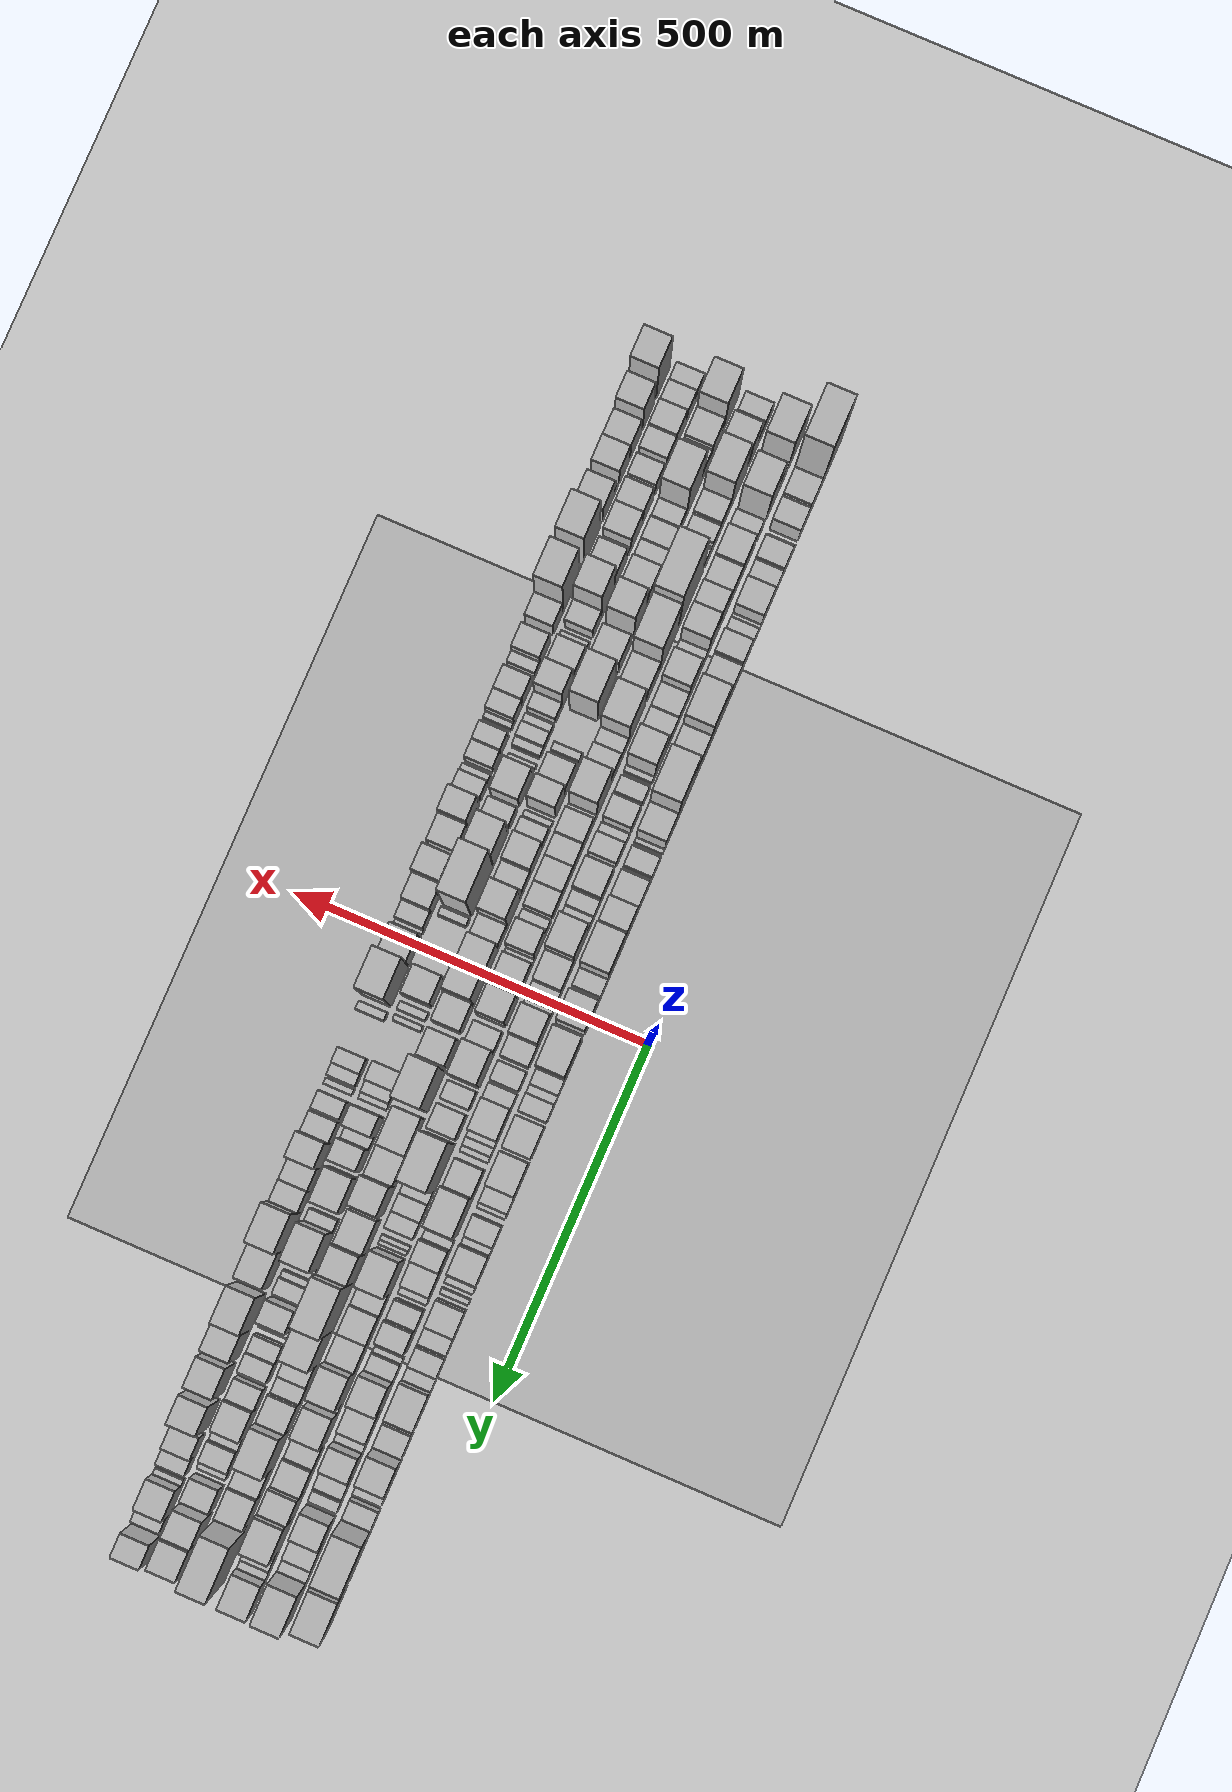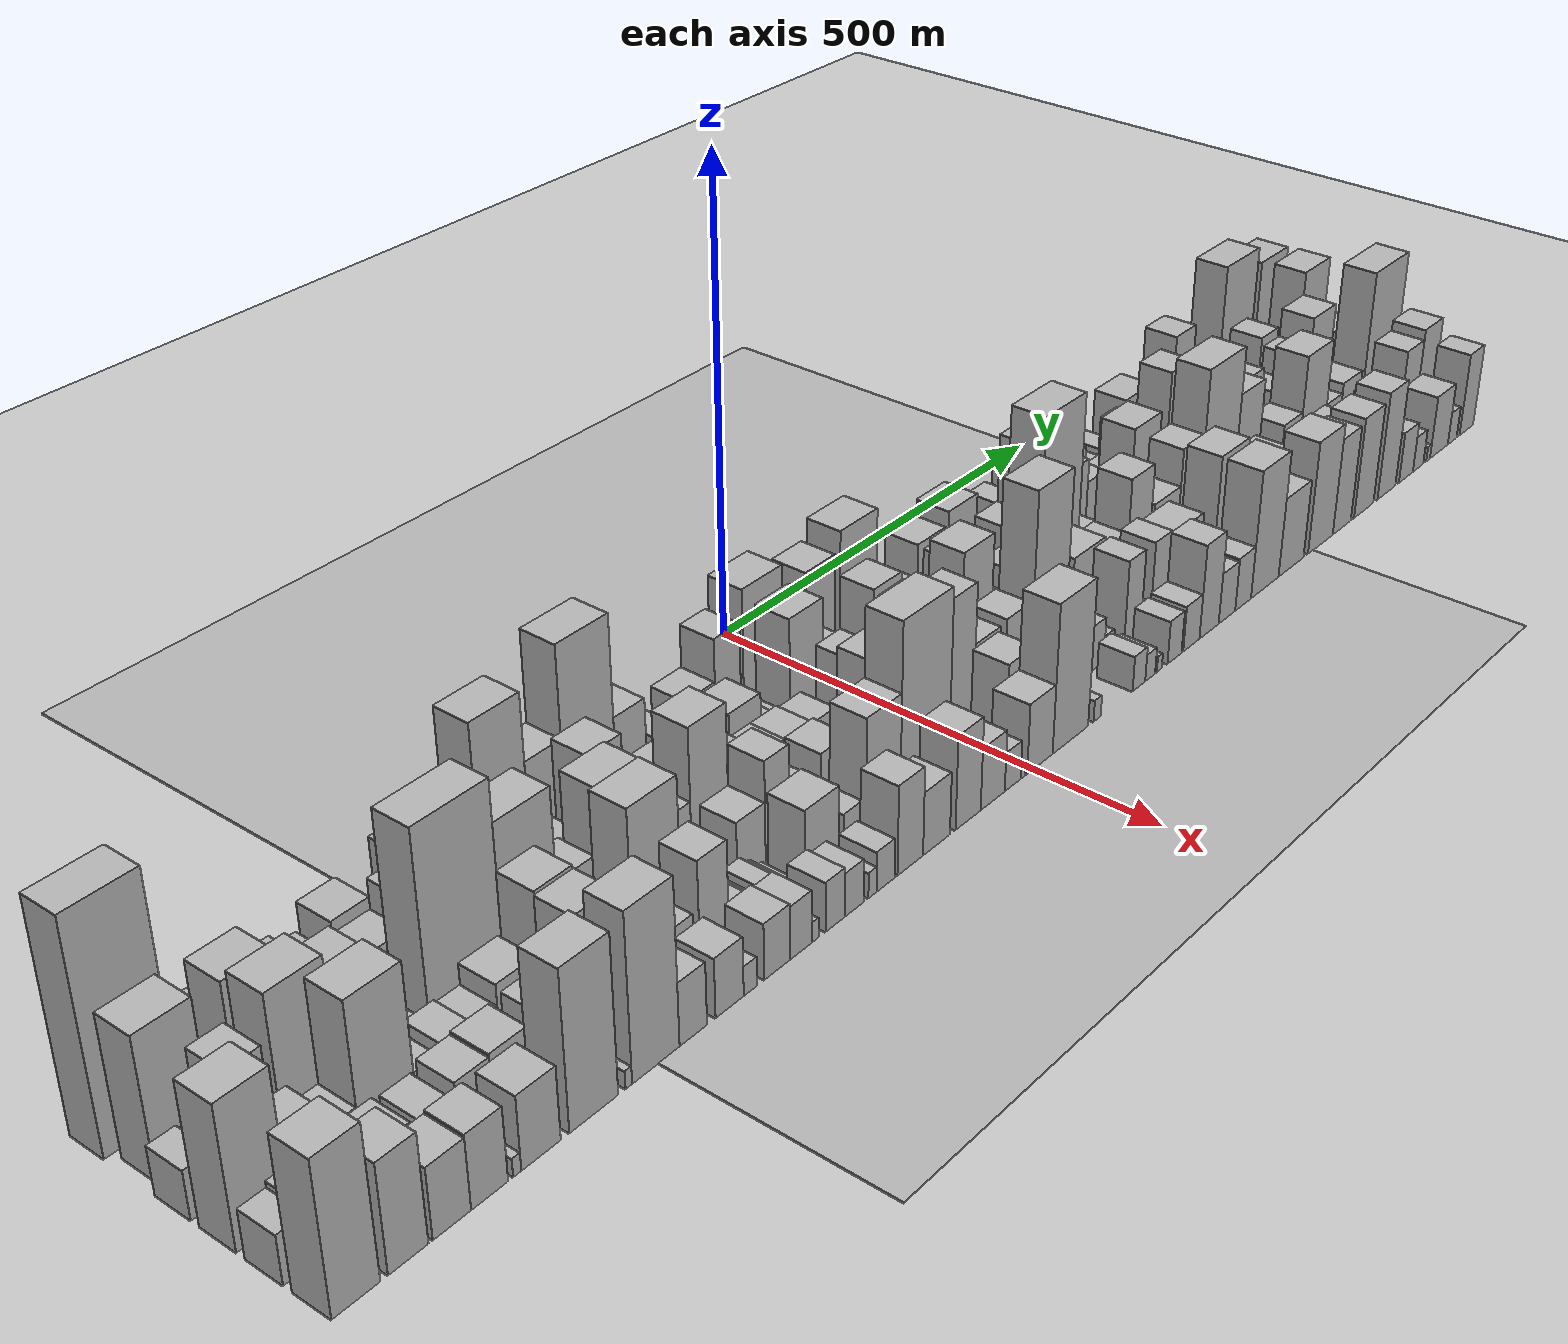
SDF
<?xml version="1.0" encoding="utf-8"?>

<sdf version="1.6">

   <world name="default">

      <gui fullscreen="0">

         <camera name="user_camera">

            <pose>-15 0 4.57585 0 0 0</pose>

            <view_controller>orbit</view_controller>

         </camera>

      </gui>

      <scene>

         <sky>

           <clouds>

             <speed>12</speed>

           </clouds>

         </sky>

         <ambient>0.4 0.4 0.4 1</ambient>

         <background>0.7 0.7 0.7 1</background>

         <shadows>1</shadows>

      </scene>

      <gravity>0 0 -9.8066</gravity>

      <magnetic_field>6e-06 2.3e-05 -4.2e-05</magnetic_field>

      <physics default="0" name="default_physics" type="ode">

         <ode>

            <solver>

               <type>quick</type>

               <iters>10</iters>

               <sor>1.0</sor>

               <use_dynamic_moi_rescaling>0</use_dynamic_moi_rescaling>

            </solver>

            <constraints>

               <cfm>0</cfm>

               <erp>0.2</erp>

               <contact_max_correcting_vel>100</contact_max_correcting_vel>

               <contact_surface_layer>0.001</contact_surface_layer>

            </constraints>

         </ode>

         <max_step_size>0.004</max_step_size>

         <real_time_factor>1</real_time_factor>

         <real_time_update_rate>250</real_time_update_rate>

      </physics>

      <light name="sun" type="directional">

         <cast_shadows>1</cast_shadows>

         <pose>0 0 10 0 0 0</pose>

         <diffuse>0.8 0.8 0.8 1</diffuse>

         <specular>0.2 0.2 0.2 1</specular>

         <attenuation>

            <range>1000</range>

            <constant>0.9</constant>

            <linear>0.01</linear>

            <quadratic>0.001</quadratic>

         </attenuation>

         <direction>-0.5 0.1 -0.9</direction>

      </light>

      <include>

         <name>ground_plane_1</name>

         <uri>model://HANNAS_ground_plane</uri>

         <pose>0 0 0  0 0 0</pose>

      </include>

      <include>

         <name>ground_plane_2</name>

         <uri>model://HANNAS_ground_plane</uri>

         <pose>100 0 0  0 0 0</pose>

      </include>

      <model name="building_1">

         <static>1</static>

         <pose frame="">100.0000 -794.2020 0 0.000000 0.000000 0.000000</pose>

         <link name="link">

            <pose frame="">0 0 112.50 0 0 0</pose>

            <collision name="collision">

               <geometry>

                  <box>

                     <size>40.0000 71.5960 225.0000</size>

                  </box>

               </geometry>

               <max_contacts>10</max_contacts>

               <surface>

                  <contact>

                     <ode/>

                  </contact>

                  <bounce/>

                  <friction>

                     <torsional>

                        <ode/>

                     </torsional>

                     <ode/>

                  </friction>

               </surface>

            </collision>

            <visual name="visual">

               <cast_shadows>0</cast_shadows>

               <geometry>

                  <box>

                     <size>40.0000 71.5960 225.0000</size>

                  </box>

               </geometry>

               <material>

                  <script>

                     <uri>model://HANNAS_wall/materials/scripts</uri>

                     <uri>model://HANNAS_wall/materials/textures</uri>

                     <name>vrc/HANNAS_wall</name>

                  </script>

               </material>

            </visual>

            <self_collide>0</self_collide>

            <enable_wind>0</enable_wind>

            <kinematic>0</kinematic>

         </link>

      </model>

      <model name="building_2">

         <static>1</static>

         <pose frame="">100.0000 -739.7507 0 0.000000 0.000000 0.000000</pose>

         <link name="link">

            <pose frame="">0 0 33.00 0 0 0</pose>

            <collision name="collision">

               <geometry>

                  <box>

                     <size>40.0000 37.3066 66.0000</size>

                  </box>

               </geometry>

               <max_contacts>10</max_contacts>

               <surface>

                  <contact>

                     <ode/>

                  </contact>

                  <bounce/>

                  <friction>

                     <torsional>

                        <ode/>

                     </torsional>

                     <ode/>

                  </friction>

               </surface>

            </collision>

            <visual name="visual">

               <cast_shadows>0</cast_shadows>

               <geometry>

                  <box>

                     <size>40.0000 37.3066 66.0000</size>

                  </box>

               </geometry>

               <material>

                  <script>

                     <uri>model://HANNAS_wall/materials/scripts</uri>

                     <uri>model://HANNAS_wall/materials/textures</uri>

                     <name>vrc/HANNAS_wall</name>

                  </script>

               </material>

            </visual>

            <self_collide>0</self_collide>

            <enable_wind>0</enable_wind>

            <kinematic>0</kinematic>

         </link>

      </model>

      <model name="building_3">

         <static>1</static>

         <pose frame="">100.0000 -701.6591 0 0.000000 0.000000 0.000000</pose>

         <link name="link">

            <pose frame="">0 0 31.50 0 0 0</pose>

            <collision name="collision">

               <geometry>

                  <box>

                     <size>40.0000 32.8764 63.0000</size>

                  </box>

               </geometry>

               <max_contacts>10</max_contacts>

               <surface>

                  <contact>

                     <ode/>

                  </contact>

                  <bounce/>

                  <friction>

                     <torsional>

                        <ode/>

                     </torsional>

                     <ode/>

                  </friction>

               </surface>

            </collision>

            <visual name="visual">

               <cast_shadows>0</cast_shadows>

               <geometry>

                  <box>

                     <size>40.0000 32.8764 63.0000</size>

                  </box>

               </geometry>

               <material>

                  <script>

                     <uri>model://HANNAS_wall/materials/scripts</uri>

                     <uri>model://HANNAS_wall/materials/textures</uri>

                     <name>vrc/HANNAS_wall</name>

                  </script>

               </material>

            </visual>

            <self_collide>0</self_collide>

            <enable_wind>0</enable_wind>

            <kinematic>0</kinematic>

         </link>

      </model>

      <model name="building_4">

         <static>1</static>

         <pose frame="">100.0000 -671.3592 0 0.000000 0.000000 0.000000</pose>

         <link name="link">

            <pose frame="">0 0 9.00 0 0 0</pose>

            <collision name="collision">

               <geometry>

                  <box>

                     <size>40.0000 7.7235 18.0000</size>

                  </box>

               </geometry>

               <max_contacts>10</max_contacts>

               <surface>

                  <contact>

                     <ode/>

                  </contact>

                  <bounce/>

                  <friction>

                     <torsional>

                        <ode/>

                     </torsional>

                     <ode/>

                  </friction>

               </surface>

            </collision>

            <visual name="visual">

               <cast_shadows>0</cast_shadows>

               <geometry>

                  <box>

                     <size>40.0000 7.7235 18.0000</size>

                  </box>

               </geometry>

               <material>

                  <script>

                     <uri>model://HANNAS_wall/materials/scripts</uri>

                     <uri>model://HANNAS_wall/materials/textures</uri>

                     <name>vrc/HANNAS_wall</name>

                  </script>

               </material>

            </visual>

            <self_collide>0</self_collide>

            <enable_wind>0</enable_wind>

            <kinematic>0</kinematic>

         </link>

      </model>

      <model name="building_5">

         <static>1</static>

         <pose frame="">100.0000 -647.3907 0 0.000000 0.000000 0.000000</pose>

         <link name="link">

            <pose frame="">0 0 31.50 0 0 0</pose>

            <collision name="collision">

               <geometry>

                  <box>

                     <size>40.0000 32.2135 63.0000</size>

                  </box>

               </geometry>

               <max_contacts>10</max_contacts>

               <surface>

                  <contact>

                     <ode/>

                  </contact>

                  <bounce/>

                  <friction>

                     <torsional>

                        <ode/>

                     </torsional>

                     <ode/>

                  </friction>

               </surface>

            </collision>

            <visual name="visual">

               <cast_shadows>0</cast_shadows>

               <geometry>

                  <box>

                     <size>40.0000 32.2135 63.0000</size>

                  </box>

               </geometry>

               <material>

                  <script>

                     <uri>model://HANNAS_wall/materials/scripts</uri>

                     <uri>model://HANNAS_wall/materials/textures</uri>

                     <name>vrc/HANNAS_wall</name>

                  </script>

               </material>

            </visual>

            <self_collide>0</self_collide>

            <enable_wind>0</enable_wind>

            <kinematic>0</kinematic>

         </link>

      </model>

      <model name="building_6">

         <static>1</static>

         <pose frame="">100.0000 -618.4481 0 0.000000 0.000000 0.000000</pose>

         <link name="link">

            <pose frame="">0 0 25.50 0 0 0</pose>

            <collision name="collision">

               <geometry>

                  <box>

                     <size>40.0000 25.6717 51.0000</size>

                  </box>

               </geometry>

               <max_contacts>10</max_contacts>

               <surface>

                  <contact>

                     <ode/>

                  </contact>

                  <bounce/>

                  <friction>

                     <torsional>

                        <ode/>

                     </torsional>

                     <ode/>

                  </friction>

               </surface>

            </collision>

            <visual name="visual">

               <cast_shadows>0</cast_shadows>

               <geometry>

                  <box>

                     <size>40.0000 25.6717 51.0000</size>

                  </box>

               </geometry>

               <material>

                  <script>

                     <uri>model://HANNAS_wall/materials/scripts</uri>

                     <uri>model://HANNAS_wall/materials/textures</uri>

                     <name>vrc/HANNAS_wall</name>

                  </script>

               </material>

            </visual>

            <self_collide>0</self_collide>

            <enable_wind>0</enable_wind>

            <kinematic>0</kinematic>

         </link>

      </model>

      <model name="building_7">

         <static>1</static>

         <pose frame="">100.0000 -581.4891 0 0.000000 0.000000 0.000000</pose>

         <link name="link">

            <pose frame="">0 0 39.00 0 0 0</pose>

            <collision name="collision">

               <geometry>

                  <box>

                     <size>40.0000 40.2463 78.0000</size>

                  </box>

               </geometry>

               <max_contacts>10</max_contacts>

               <surface>

                  <contact>

                     <ode/>

                  </contact>

                  <bounce/>

                  <friction>

                     <torsional>

                        <ode/>

                     </torsional>

                     <ode/>

                  </friction>

               </surface>

            </collision>

            <visual name="visual">

               <cast_shadows>0</cast_shadows>

               <geometry>

                  <box>

                     <size>40.0000 40.2463 78.0000</size>

                  </box>

               </geometry>

               <material>

                  <script>

                     <uri>model://HANNAS_wall/materials/scripts</uri>

                     <uri>model://HANNAS_wall/materials/textures</uri>

                     <name>vrc/HANNAS_wall</name>

                  </script>

               </material>

            </visual>

            <self_collide>0</self_collide>

            <enable_wind>0</enable_wind>

            <kinematic>0</kinematic>

         </link>

      </model>

      <model name="building_8">

         <static>1</static>

         <pose frame="">100.0000 -557.1574 0 0.000000 0.000000 0.000000</pose>

         <link name="link">

            <pose frame="">0 0 9.00 0 0 0</pose>

            <collision name="collision">

               <geometry>

                  <box>

                     <size>40.0000 8.4170 18.0000</size>

                  </box>

               </geometry>

               <max_contacts>10</max_contacts>

               <surface>

                  <contact>

                     <ode/>

                  </contact>

                  <bounce/>

                  <friction>

                     <torsional>

                        <ode/>

                     </torsional>

                     <ode/>

                  </friction>

               </surface>

            </collision>

            <visual name="visual">

               <cast_shadows>0</cast_shadows>

               <geometry>

                  <box>

                     <size>40.0000 8.4170 18.0000</size>

                  </box>

               </geometry>

               <material>

                  <script>

                     <uri>model://HANNAS_wall/materials/scripts</uri>

                     <uri>model://HANNAS_wall/materials/textures</uri>

                     <name>vrc/HANNAS_wall</name>

                  </script>

               </material>

            </visual>

            <self_collide>0</self_collide>

            <enable_wind>0</enable_wind>

            <kinematic>0</kinematic>

         </link>

      </model>

      <model name="building_9">

         <static>1</static>

         <pose frame="">100.0000 -543.4780 0 0.000000 0.000000 0.000000</pose>

         <link name="link">

            <pose frame="">0 0 16.50 0 0 0</pose>

            <collision name="collision">

               <geometry>

                  <box>

                     <size>40.0000 18.9418 33.0000</size>

                  </box>

               </geometry>

               <max_contacts>10</max_contacts>

               <surface>

                  <contact>

                     <ode/>

                  </contact>

                  <bounce/>

                  <friction>

                     <torsional>

                        <ode/>

                     </torsional>

                     <ode/>

                  </friction>

               </surface>

            </collision>

            <visual name="visual">

               <cast_shadows>0</cast_shadows>

               <geometry>

                  <box>

                     <size>40.0000 18.9418 33.0000</size>

                  </box>

               </geometry>

               <material>

                  <script>

                     <uri>model://HANNAS_wall/materials/scripts</uri>

                     <uri>model://HANNAS_wall/materials/textures</uri>

                     <name>vrc/HANNAS_wall</name>

                  </script>

               </material>

            </visual>

            <self_collide>0</self_collide>

            <enable_wind>0</enable_wind>

            <kinematic>0</kinematic>

         </link>

      </model>

      <model name="building_10">

         <static>1</static>

         <pose frame="">100.0000 -507.6493 0 0.000000 0.000000 0.000000</pose>

         <link name="link">

            <pose frame="">0 0 48.00 0 0 0</pose>

            <collision name="collision">

               <geometry>

                  <box>

                     <size>40.0000 32.7156 96.0000</size>

                  </box>

               </geometry>

               <max_contacts>10</max_contacts>

               <surface>

                  <contact>

                     <ode/>

                  </contact>

                  <bounce/>

                  <friction>

                     <torsional>

                        <ode/>

                     </torsional>

                     <ode/>

                  </friction>

               </surface>

            </collision>

            <visual name="visual">

               <cast_shadows>0</cast_shadows>

               <geometry>

                  <box>

                     <size>40.0000 32.7156 96.0000</size>

                  </box>

               </geometry>

               <material>

                  <script>

                     <uri>model://HANNAS_wall/materials/scripts</uri>

                     <uri>model://HANNAS_wall/materials/textures</uri>

                     <name>vrc/HANNAS_wall</name>

                  </script>

               </material>

            </visual>

            <self_collide>0</self_collide>

            <enable_wind>0</enable_wind>

            <kinematic>0</kinematic>

         </link>

      </model>

      <model name="building_11">

         <static>1</static>

         <pose frame="">100.0000 -470.2240 0 0.000000 0.000000 0.000000</pose>

         <link name="link">

            <pose frame="">0 0 39.00 0 0 0</pose>

            <collision name="collision">

               <geometry>

                  <box>

                     <size>40.0000 42.1351 78.0000</size>

                  </box>

               </geometry>

               <max_contacts>10</max_contacts>

               <surface>

                  <contact>

                     <ode/>

                  </contact>

                  <bounce/>

                  <friction>

                     <torsional>

                        <ode/>

                     </torsional>

                     <ode/>

                  </friction>

               </surface>

            </collision>

            <visual name="visual">

               <cast_shadows>0</cast_shadows>

               <geometry>

                  <box>

                     <size>40.0000 42.1351 78.0000</size>

                  </box>

               </geometry>

               <material>

                  <script>

                     <uri>model://HANNAS_wall/materials/scripts</uri>

                     <uri>model://HANNAS_wall/materials/textures</uri>

                     <name>vrc/HANNAS_wall</name>

                  </script>

               </material>

            </visual>

            <self_collide>0</self_collide>

            <enable_wind>0</enable_wind>

            <kinematic>0</kinematic>

         </link>

      </model>

      <model name="building_12">

         <static>1</static>

         <pose frame="">100.0000 -415.5704 0 0.000000 0.000000 0.000000</pose>

         <link name="link">

            <pose frame="">0 0 90.00 0 0 0</pose>

            <collision name="collision">

               <geometry>

                  <box>

                     <size>40.0000 57.1721 180.0000</size>

                  </box>

               </geometry>

               <max_contacts>10</max_contacts>

               <surface>

                  <contact>

                     <ode/>

                  </contact>

                  <bounce/>

                  <friction>

                     <torsional>

                        <ode/>

                     </torsional>

                     <ode/>

                  </friction>

               </surface>

            </collision>

            <visual name="visual">

               <cast_shadows>0</cast_shadows>

               <geometry>

                  <box>

                     <size>40.0000 57.1721 180.0000</size>

                  </box>

               </geometry>

               <material>

                  <script>

                     <uri>model://HANNAS_wall/materials/scripts</uri>

                     <uri>model://HANNAS_wall/materials/textures</uri>

                     <name>vrc/HANNAS_wall</name>

                  </script>

               </material>

            </visual>

            <self_collide>0</self_collide>

            <enable_wind>0</enable_wind>

            <kinematic>0</kinematic>

         </link>

      </model>

      <model name="building_13">

         <static>1</static>

         <pose frame="">100.0000 -365.4669 0 0.000000 0.000000 0.000000</pose>

         <link name="link">

            <pose frame="">0 0 55.50 0 0 0</pose>

            <collision name="collision">

               <geometry>

                  <box>

                     <size>40.0000 43.0348 111.0000</size>

                  </box>

               </geometry>

               <max_contacts>10</max_contacts>

               <surface>

                  <contact>

                     <ode/>

                  </contact>

                  <bounce/>

                  <friction>

                     <torsional>

                        <ode/>

                     </torsional>

                     <ode/>

                  </friction>

               </surface>

            </collision>

            <visual name="visual">

               <cast_shadows>0</cast_shadows>

               <geometry>

                  <box>

                     <size>40.0000 43.0348 111.0000</size>

                  </box>

               </geometry>

               <material>

                  <script>

                     <uri>model://HANNAS_wall/materials/scripts</uri>

                     <uri>model://HANNAS_wall/materials/textures</uri>

                     <name>vrc/HANNAS_wall</name>

                  </script>

               </material>

            </visual>

            <self_collide>0</self_collide>

            <enable_wind>0</enable_wind>

            <kinematic>0</kinematic>

         </link>

      </model>

      <model name="building_14">

         <static>1</static>

         <pose frame="">100.0000 -312.3354 0 0.000000 0.000000 0.000000</pose>

         <link name="link">

            <pose frame="">0 0 102.00 0 0 0</pose>

            <collision name="collision">

               <geometry>

                  <box>

                     <size>40.0000 63.2282 204.0000</size>

                  </box>

               </geometry>

               <max_contacts>10</max_contacts>

               <surface>

                  <contact>

                     <ode/>

                  </contact>

                  <bounce/>

                  <friction>

                     <torsional>

                        <ode/>

                     </torsional>

                     <ode/>

                  </friction>

               </surface>

            </collision>

            <visual name="visual">

               <cast_shadows>0</cast_shadows>

               <geometry>

                  <box>

                     <size>40.0000 63.2282 204.0000</size>

                  </box>

               </geometry>

               <material>

                  <script>

                     <uri>model://HANNAS_wall/materials/scripts</uri>

                     <uri>model://HANNAS_wall/materials/textures</uri>

                     <name>vrc/HANNAS_wall</name>

                  </script>

               </material>

            </visual>

            <self_collide>0</self_collide>

            <enable_wind>0</enable_wind>

            <kinematic>0</kinematic>

         </link>

      </model>

      <model name="building_15">

         <static>1</static>

         <pose frame="">100.0000 -261.1318 0 0.000000 0.000000 0.000000</pose>

         <link name="link">

            <pose frame="">0 0 49.50 0 0 0</pose>

            <collision name="collision">

               <geometry>

                  <box>

                     <size>40.0000 39.1790 99.0000</size>

                  </box>

               </geometry>

               <max_contacts>10</max_contacts>

               <surface>

                  <contact>

                     <ode/>

                  </contact>

                  <bounce/>

                  <friction>

                     <torsional>

                        <ode/>

                     </torsional>

                     <ode/>

                  </friction>

               </surface>

            </collision>

            <visual name="visual">

               <cast_shadows>0</cast_shadows>

               <geometry>

                  <box>

                     <size>40.0000 39.1790 99.0000</size>

                  </box>

               </geometry>

               <material>

                  <script>

                     <uri>model://HANNAS_wall/materials/scripts</uri>

                     <uri>model://HANNAS_wall/materials/textures</uri>

                     <name>vrc/HANNAS_wall</name>

                  </script>

               </material>

            </visual>

            <self_collide>0</self_collide>

            <enable_wind>0</enable_wind>

            <kinematic>0</kinematic>

         </link>

      </model>

      <model name="building_16">

         <static>1</static>

         <pose frame="">100.0000 -238.0258 0 0.000000 0.000000 0.000000</pose>

         <link name="link">

            <pose frame="">0 0 7.50 0 0 0</pose>

            <collision name="collision">

               <geometry>

                  <box>

                     <size>40.0000 7.0330 15.0000</size>

                  </box>

               </geometry>

               <max_contacts>10</max_contacts>

               <surface>

                  <contact>

                     <ode/>

                  </contact>

                  <bounce/>

                  <friction>

                     <torsional>

                        <ode/>

                     </torsional>

                     <ode/>

                  </friction>

               </surface>

            </collision>

            <visual name="visual">

               <cast_shadows>0</cast_shadows>

               <geometry>

                  <box>

                     <size>40.0000 7.0330 15.0000</size>

                  </box>

               </geometry>

               <material>

                  <script>

                     <uri>model://HANNAS_wall/materials/scripts</uri>

                     <uri>model://HANNAS_wall/materials/textures</uri>

                     <name>vrc/HANNAS_wall</name>

                  </script>

               </material>

            </visual>

            <self_collide>0</self_collide>

            <enable_wind>0</enable_wind>

            <kinematic>0</kinematic>

         </link>

      </model>

      <model name="building_17">

         <static>1</static>

         <pose frame="">100.0000 -212.2948 0 0.000000 0.000000 0.000000</pose>

         <link name="link">

            <pose frame="">0 0 24.00 0 0 0</pose>

            <collision name="collision">

               <geometry>

                  <box>

                     <size>40.0000 28.4289 48.0000</size>

                  </box>

               </geometry>

               <max_contacts>10</max_contacts>

               <surface>

                  <contact>

                     <ode/>

                  </contact>

                  <bounce/>

                  <friction>

                     <torsional>

                        <ode/>

                     </torsional>

                     <ode/>

                  </friction>

               </surface>

            </collision>

            <visual name="visual">

               <cast_shadows>0</cast_shadows>

               <geometry>

                  <box>

                     <size>40.0000 28.4289 48.0000</size>

                  </box>

               </geometry>

               <material>

                  <script>

                     <uri>model://HANNAS_wall/materials/scripts</uri>

                     <uri>model://HANNAS_wall/materials/textures</uri>

                     <name>vrc/HANNAS_wall</name>

                  </script>

               </material>

            </visual>

            <self_collide>0</self_collide>

            <enable_wind>0</enable_wind>

            <kinematic>0</kinematic>

         </link>

      </model>

      <model name="building_18">

         <static>1</static>

         <pose frame="">100.0000 -194.4038 0 0.000000 0.000000 0.000000</pose>

         <link name="link">

            <pose frame="">0 0 7.50 0 0 0</pose>

            <collision name="collision">

               <geometry>

                  <box>

                     <size>40.0000 7.3532 15.0000</size>

                  </box>

               </geometry>

               <max_contacts>10</max_contacts>

               <surface>

                  <contact>

                     <ode/>

                  </contact>

                  <bounce/>

                  <friction>

                     <torsional>

                        <ode/>

                     </torsional>

                     <ode/>

                  </friction>

               </surface>

            </collision>

            <visual name="visual">

               <cast_shadows>0</cast_shadows>

               <geometry>

                  <box>

                     <size>40.0000 7.3532 15.0000</size>

                  </box>

               </geometry>

               <material>

                  <script>

                     <uri>model://HANNAS_wall/materials/scripts</uri>

                     <uri>model://HANNAS_wall/materials/textures</uri>

                     <name>vrc/HANNAS_wall</name>

                  </script>

               </material>

            </visual>

            <self_collide>0</self_collide>

            <enable_wind>0</enable_wind>

            <kinematic>0</kinematic>

         </link>

      </model>

      <model name="building_19">

         <static>1</static>

         <pose frame="">100.0000 -170.3524 0 0.000000 0.000000 0.000000</pose>

         <link name="link">

            <pose frame="">0 0 34.50 0 0 0</pose>

            <collision name="collision">

               <geometry>

                  <box>

                     <size>40.0000 40.7496 69.0000</size>

                  </box>

               </geometry>

               <max_contacts>10</max_contacts>

               <surface>

                  <contact>

                     <ode/>

                  </contact>

                  <bounce/>

                  <friction>

                     <torsional>

                        <ode/>

                     </torsional>

                     <ode/>

                  </friction>

               </surface>

            </collision>

            <visual name="visual">

               <cast_shadows>0</cast_shadows>

               <geometry>

                  <box>

                     <size>40.0000 40.7496 69.0000</size>

                  </box>

               </geometry>

               <material>

                  <script>

                     <uri>model://HANNAS_wall/materials/scripts</uri>

                     <uri>model://HANNAS_wall/materials/textures</uri>

                     <name>vrc/HANNAS_wall</name>

                  </script>

               </material>

            </visual>

            <self_collide>0</self_collide>

            <enable_wind>0</enable_wind>

            <kinematic>0</kinematic>

         </link>

      </model>

      <model name="building_20">

         <static>1</static>

         <pose frame="">100.0000 -132.4593 0 0.000000 0.000000 0.000000</pose>

         <link name="link">

            <pose frame="">0 0 57.00 0 0 0</pose>

            <collision name="collision">

               <geometry>

                  <box>

                     <size>40.0000 35.0364 114.0000</size>

                  </box>

               </geometry>

               <max_contacts>10</max_contacts>

               <surface>

                  <contact>

                     <ode/>

                  </contact>

                  <bounce/>

                  <friction>

                     <torsional>

                        <ode/>

                     </torsional>

                     <ode/>

                  </friction>

               </surface>

            </collision>

            <visual name="visual">

               <cast_shadows>0</cast_shadows>

               <geometry>

                  <box>

                     <size>40.0000 35.0364 114.0000</size>

                  </box>

               </geometry>

               <material>

                  <script>

                     <uri>model://HANNAS_wall/materials/scripts</uri>

                     <uri>model://HANNAS_wall/materials/textures</uri>

                     <name>vrc/HANNAS_wall</name>

                  </script>

               </material>

            </visual>

            <self_collide>0</self_collide>

            <enable_wind>0</enable_wind>

            <kinematic>0</kinematic>

         </link>

      </model>

      <model name="building_21">

         <static>1</static>

         <pose frame="">100.0000 -83.0695 0 0.000000 0.000000 0.000000</pose>

         <link name="link">

            <pose frame="">0 0 73.50 0 0 0</pose>

            <collision name="collision">

               <geometry>

                  <box>

                     <size>40.0000 55.7433 147.0000</size>

                  </box>

               </geometry>

               <max_contacts>10</max_contacts>

               <surface>

                  <contact>

                     <ode/>

                  </contact>

                  <bounce/>

                  <friction>

                     <torsional>

                        <ode/>

                     </torsional>

                     <ode/>

                  </friction>

               </surface>

            </collision>

            <visual name="visual">

               <cast_shadows>0</cast_shadows>

               <geometry>

                  <box>

                     <size>40.0000 55.7433 147.0000</size>

                  </box>

               </geometry>

               <material>

                  <script>

                     <uri>model://HANNAS_wall/materials/scripts</uri>

                     <uri>model://HANNAS_wall/materials/textures</uri>

                     <name>vrc/HANNAS_wall</name>

                  </script>

               </material>

            </visual>

            <self_collide>0</self_collide>

            <enable_wind>0</enable_wind>

            <kinematic>0</kinematic>

         </link>

      </model>

      <model name="building_22">

         <static>1</static>

         <pose frame="">100.0000 -42.6258 0 0.000000 0.000000 0.000000</pose>

         <link name="link">

            <pose frame="">0 0 22.50 0 0 0</pose>

            <collision name="collision">

               <geometry>

                  <box>

                     <size>40.0000 25.1440 45.0000</size>

                  </box>

               </geometry>

               <max_contacts>10</max_contacts>

               <surface>

                  <contact>

                     <ode/>

                  </contact>

                  <bounce/>

                  <friction>

                     <torsional>

                        <ode/>

                     </torsional>

                     <ode/>

                  </friction>

               </surface>

            </collision>

            <visual name="visual">

               <cast_shadows>0</cast_shadows>

               <geometry>

                  <box>

                     <size>40.0000 25.1440 45.0000</size>

                  </box>

               </geometry>

               <material>

                  <script>

                     <uri>model://HANNAS_wall/materials/scripts</uri>

                     <uri>model://HANNAS_wall/materials/textures</uri>

                     <name>vrc/HANNAS_wall</name>

                  </script>

               </material>

            </visual>

            <self_collide>0</self_collide>

            <enable_wind>0</enable_wind>

            <kinematic>0</kinematic>

         </link>

      </model>

      <model name="building_23">

         <static>1</static>

         <pose frame="">100.0000 -25.8281 0 0.000000 0.000000 0.000000</pose>

         <link name="link">

            <pose frame="">0 0 10.50 0 0 0</pose>

            <collision name="collision">

               <geometry>

                  <box>

                     <size>40.0000 8.4514 21.0000</size>

                  </box>

               </geometry>

               <max_contacts>10</max_contacts>

               <surface>

                  <contact>

                     <ode/>

                  </contact>

                  <bounce/>

                  <friction>

                     <torsional>

                        <ode/>

                     </torsional>

                     <ode/>

                  </friction>

               </surface>

            </collision>

            <visual name="visual">

               <cast_shadows>0</cast_shadows>

               <geometry>

                  <box>

                     <size>40.0000 8.4514 21.0000</size>

                  </box>

               </geometry>

               <material>

                  <script>

                     <uri>model://HANNAS_wall/materials/scripts</uri>

                     <uri>model://HANNAS_wall/materials/textures</uri>

                     <name>vrc/HANNAS_wall</name>

                  </script>

               </material>

            </visual>

            <self_collide>0</self_collide>

            <enable_wind>0</enable_wind>

            <kinematic>0</kinematic>

         </link>

      </model>

      <model name="building_24">

         <static>1</static>

         <pose frame="">100.0000 -0.0143 0 0.000000 0.000000 0.000000</pose>

         <link name="link">

            <pose frame="">0 0 61.50 0 0 0</pose>

            <collision name="collision">

               <geometry>

                  <box>

                     <size>40.0000 43.1762 123.0000</size>

                  </box>

               </geometry>

               <max_contacts>10</max_contacts>

               <surface>

                  <contact>

                     <ode/>

                  </contact>

                  <bounce/>

                  <friction>

                     <torsional>

                        <ode/>

                     </torsional>

                     <ode/>

                  </friction>

               </surface>

            </collision>

            <visual name="visual">

               <cast_shadows>0</cast_shadows>

               <geometry>

                  <box>

                     <size>40.0000 43.1762 123.0000</size>

                  </box>

               </geometry>

               <material>

                  <script>

                     <uri>model://HANNAS_wall/materials/scripts</uri>

                     <uri>model://HANNAS_wall/materials/textures</uri>

                     <name>vrc/HANNAS_wall</name>

                  </script>

               </material>

            </visual>

            <self_collide>0</self_collide>

            <enable_wind>0</enable_wind>

            <kinematic>0</kinematic>

         </link>

      </model>

      <model name="building_25">

         <static>1</static>

         <pose frame="">100.0000 57.4775 0 0.000000 0.000000 0.000000</pose>

         <link name="link">

            <pose frame="">0 0 72.00 0 0 0</pose>

            <collision name="collision">

               <geometry>

                  <box>

                     <size>40.0000 55.8075 144.0000</size>

                  </box>

               </geometry>

               <max_contacts>10</max_contacts>

               <surface>

                  <contact>

                     <ode/>

                  </contact>

                  <bounce/>

                  <friction>

                     <torsional>

                        <ode/>

                     </torsional>

                     <ode/>

                  </friction>

               </surface>

            </collision>

            <visual name="visual">

               <cast_shadows>0</cast_shadows>

               <geometry>

                  <box>

                     <size>40.0000 55.8075 144.0000</size>

                  </box>

               </geometry>

               <material>

                  <script>

                     <uri>model://HANNAS_wall/materials/scripts</uri>

                     <uri>model://HANNAS_wall/materials/textures</uri>

                     <name>vrc/HANNAS_wall</name>

                  </script>

               </material>

            </visual>

            <self_collide>0</self_collide>

            <enable_wind>0</enable_wind>

            <kinematic>0</kinematic>

         </link>

      </model>

      <model name="building_26">

         <static>1</static>

         <pose frame="">100.0000 96.2898 0 0.000000 0.000000 0.000000</pose>

         <link name="link">

            <pose frame="">0 0 19.50 0 0 0</pose>

            <collision name="collision">

               <geometry>

                  <box>

                     <size>40.0000 21.8170 39.0000</size>

                  </box>

               </geometry>

               <max_contacts>10</max_contacts>

               <surface>

                  <contact>

                     <ode/>

                  </contact>

                  <bounce/>

                  <friction>

                     <torsional>

                        <ode/>

                     </torsional>

                     <ode/>

                  </friction>

               </surface>

            </collision>

            <visual name="visual">

               <cast_shadows>0</cast_shadows>

               <geometry>

                  <box>

                     <size>40.0000 21.8170 39.0000</size>

                  </box>

               </geometry>

               <material>

                  <script>

                     <uri>model://HANNAS_wall/materials/scripts</uri>

                     <uri>model://HANNAS_wall/materials/textures</uri>

                     <name>vrc/HANNAS_wall</name>

                  </script>

               </material>

            </visual>

            <self_collide>0</self_collide>

            <enable_wind>0</enable_wind>

            <kinematic>0</kinematic>

         </link>

      </model>

      <model name="building_27">

         <static>1</static>

         <pose frame="">100.0000 113.4390 0 0.000000 0.000000 0.000000</pose>

         <link name="link">

            <pose frame="">0 0 13.50 0 0 0</pose>

            <collision name="collision">

               <geometry>

                  <box>

                     <size>40.0000 12.4813 27.0000</size>

                  </box>

               </geometry>

               <max_contacts>10</max_contacts>

               <surface>

                  <contact>

                     <ode/>

                  </contact>

                  <bounce/>

                  <friction>

                     <torsional>

                        <ode/>

                     </torsional>

                     <ode/>

                  </friction>

               </surface>

            </collision>

            <visual name="visual">

               <cast_shadows>0</cast_shadows>

               <geometry>

                  <box>

                     <size>40.0000 12.4813 27.0000</size>

                  </box>

               </geometry>

               <material>

                  <script>

                     <uri>model://HANNAS_wall/materials/scripts</uri>

                     <uri>model://HANNAS_wall/materials/textures</uri>

                     <name>vrc/HANNAS_wall</name>

                  </script>

               </material>

            </visual>

            <self_collide>0</self_collide>

            <enable_wind>0</enable_wind>

            <kinematic>0</kinematic>

         </link>

      </model>

      <model name="building_28">

         <static>1</static>

         <pose frame="">100.0000 132.2733 0 0.000000 0.000000 0.000000</pose>

         <link name="link">

            <pose frame="">0 0 21.00 0 0 0</pose>

            <collision name="collision">

               <geometry>

                  <box>

                     <size>40.0000 25.1873 42.0000</size>

                  </box>

               </geometry>

               <max_contacts>10</max_contacts>

               <surface>

                  <contact>

                     <ode/>

                  </contact>

                  <bounce/>

                  <friction>

                     <torsional>

                        <ode/>

                     </torsional>

                     <ode/>

                  </friction>

               </surface>

            </collision>

            <visual name="visual">

               <cast_shadows>0</cast_shadows>

               <geometry>

                  <box>

                     <size>40.0000 25.1873 42.0000</size>

                  </box>

               </geometry>

               <material>

                  <script>

                     <uri>model://HANNAS_wall/materials/scripts</uri>

                     <uri>model://HANNAS_wall/materials/textures</uri>

                     <name>vrc/HANNAS_wall</name>

                  </script>

               </material>

            </visual>

            <self_collide>0</self_collide>

            <enable_wind>0</enable_wind>

            <kinematic>0</kinematic>

         </link>

      </model>

      <model name="building_29">

         <static>1</static>

         <pose frame="">100.0000 173.3552 0 0.000000 0.000000 0.000000</pose>

         <link name="link">

            <pose frame="">0 0 37.50 0 0 0</pose>

            <collision name="collision">

               <geometry>

                  <box>

                     <size>40.0000 44.9764 75.0000</size>

                  </box>

               </geometry>

               <max_contacts>10</max_contacts>

               <surface>

                  <contact>

                     <ode/>

                  </contact>

                  <bounce/>

                  <friction>

                     <torsional>

                        <ode/>

                     </torsional>

                     <ode/>

                  </friction>

               </surface>

            </collision>

            <visual name="visual">

               <cast_shadows>0</cast_shadows>

               <geometry>

                  <box>

                     <size>40.0000 44.9764 75.0000</size>

                  </box>

               </geometry>

               <material>

                  <script>

                     <uri>model://HANNAS_wall/materials/scripts</uri>

                     <uri>model://HANNAS_wall/materials/textures</uri>

                     <name>vrc/HANNAS_wall</name>

                  </script>

               </material>

            </visual>

            <self_collide>0</self_collide>

            <enable_wind>0</enable_wind>

            <kinematic>0</kinematic>

         </link>

      </model>

      <model name="building_30">

         <static>1</static>

         <pose frame="">100.0000 224.4395 0 0.000000 0.000000 0.000000</pose>

         <link name="link">

            <pose frame="">0 0 45.00 0 0 0</pose>

            <collision name="collision">

               <geometry>

                  <box>

                     <size>40.0000 47.1923 90.0000</size>

                  </box>

               </geometry>

               <max_contacts>10</max_contacts>

               <surface>

                  <contact>

                     <ode/>

                  </contact>

                  <bounce/>

                  <friction>

                     <torsional>

                        <ode/>

                     </torsional>

                     <ode/>

                  </friction>

               </surface>

            </collision>

            <visual name="visual">

               <cast_shadows>0</cast_shadows>

               <geometry>

                  <box>

                     <size>40.0000 47.1923 90.0000</size>

                  </box>

               </geometry>

               <material>

                  <script>

                     <uri>model://HANNAS_wall/materials/scripts</uri>

                     <uri>model://HANNAS_wall/materials/textures</uri>

                     <name>vrc/HANNAS_wall</name>

                  </script>

               </material>

            </visual>

            <self_collide>0</self_collide>

            <enable_wind>0</enable_wind>

            <kinematic>0</kinematic>

         </link>

      </model>

      <model name="building_31">

         <static>1</static>

         <pose frame="">100.0000 260.0654 0 0.000000 0.000000 0.000000</pose>

         <link name="link">

            <pose frame="">0 0 21.00 0 0 0</pose>

            <collision name="collision">

               <geometry>

                  <box>

                     <size>40.0000 24.0594 42.0000</size>

                  </box>

               </geometry>

               <max_contacts>10</max_contacts>

               <surface>

                  <contact>

                     <ode/>

                  </contact>

                  <bounce/>

                  <friction>

                     <torsional>

                        <ode/>

                     </torsional>

                     <ode/>

                  </friction>

               </surface>

            </collision>

            <visual name="visual">

               <cast_shadows>0</cast_shadows>

               <geometry>

                  <box>

                     <size>40.0000 24.0594 42.0000</size>

                  </box>

               </geometry>

               <material>

                  <script>

                     <uri>model://HANNAS_wall/materials/scripts</uri>

                     <uri>model://HANNAS_wall/materials/textures</uri>

                     <name>vrc/HANNAS_wall</name>

                  </script>

               </material>

            </visual>

            <self_collide>0</self_collide>

            <enable_wind>0</enable_wind>

            <kinematic>0</kinematic>

         </link>

      </model>

      <model name="building_32">

         <static>1</static>

         <pose frame="">100.0000 275.8018 0 0.000000 0.000000 0.000000</pose>

         <link name="link">

            <pose frame="">0 0 7.50 0 0 0</pose>

            <collision name="collision">

               <geometry>

                  <box>

                     <size>40.0000 7.4135 15.0000</size>

                  </box>

               </geometry>

               <max_contacts>10</max_contacts>

               <surface>

                  <contact>

                     <ode/>

                  </contact>

                  <bounce/>

                  <friction>

                     <torsional>

                        <ode/>

                     </torsional>

                     <ode/>

                  </friction>

               </surface>

            </collision>

            <visual name="visual">

               <cast_shadows>0</cast_shadows>

               <geometry>

                  <box>

                     <size>40.0000 7.4135 15.0000</size>

                  </box>

               </geometry>

               <material>

                  <script>

                     <uri>model://HANNAS_wall/materials/scripts</uri>

                     <uri>model://HANNAS_wall/materials/textures</uri>

                     <name>vrc/HANNAS_wall</name>

                  </script>

               </material>

            </visual>

            <self_collide>0</self_collide>

            <enable_wind>0</enable_wind>

            <kinematic>0</kinematic>

         </link>

      </model>

      <model name="building_33">

         <static>1</static>

         <pose frame="">100.0000 303.5232 0 0.000000 0.000000 0.000000</pose>

         <link name="link">

            <pose frame="">0 0 30.00 0 0 0</pose>

            <collision name="collision">

               <geometry>

                  <box>

                     <size>40.0000 30.0294 60.0000</size>

                  </box>

               </geometry>

               <max_contacts>10</max_contacts>

               <surface>

                  <contact>

                     <ode/>

                  </contact>

                  <bounce/>

                  <friction>

                     <torsional>

                        <ode/>

                     </torsional>

                     <ode/>

                  </friction>

               </surface>

            </collision>

            <visual name="visual">

               <cast_shadows>0</cast_shadows>

               <geometry>

                  <box>

                     <size>40.0000 30.0294 60.0000</size>

                  </box>

               </geometry>

               <material>

                  <script>

                     <uri>model://HANNAS_wall/materials/scripts</uri>

                     <uri>model://HANNAS_wall/materials/textures</uri>

                     <name>vrc/HANNAS_wall</name>

                  </script>

               </material>

            </visual>

            <self_collide>0</self_collide>

            <enable_wind>0</enable_wind>

            <kinematic>0</kinematic>

         </link>

      </model>

      <model name="building_34">

         <static>1</static>

         <pose frame="">100.0000 324.2681 0 0.000000 0.000000 0.000000</pose>

         <link name="link">

            <pose frame="">0 0 12.00 0 0 0</pose>

            <collision name="collision">

               <geometry>

                  <box>

                     <size>40.0000 11.4604 24.0000</size>

                  </box>

               </geometry>

               <max_contacts>10</max_contacts>

               <surface>

                  <contact>

                     <ode/>

                  </contact>

                  <bounce/>

                  <friction>

                     <torsional>

                        <ode/>

                     </torsional>

                     <ode/>

                  </friction>

               </surface>

            </collision>

            <visual name="visual">

               <cast_shadows>0</cast_shadows>

               <geometry>

                  <box>

                     <size>40.0000 11.4604 24.0000</size>

                  </box>

               </geometry>

               <material>

                  <script>

                     <uri>model://HANNAS_wall/materials/scripts</uri>

                     <uri>model://HANNAS_wall/materials/textures</uri>

                     <name>vrc/HANNAS_wall</name>

                  </script>

               </material>

            </visual>

            <self_collide>0</self_collide>

            <enable_wind>0</enable_wind>

            <kinematic>0</kinematic>

         </link>

      </model>

      <model name="building_35">

         <static>1</static>

         <pose frame="">100.0000 350.2598 0 0.000000 0.000000 0.000000</pose>

         <link name="link">

            <pose frame="">0 0 40.50 0 0 0</pose>

            <collision name="collision">

               <geometry>

                  <box>

                     <size>40.0000 40.5229 81.0000</size>

                  </box>

               </geometry>

               <max_contacts>10</max_contacts>

               <surface>

                  <contact>

                     <ode/>

                  </contact>

                  <bounce/>

                  <friction>

                     <torsional>

                        <ode/>

                     </torsional>

                     <ode/>

                  </friction>

               </surface>

            </collision>

            <visual name="visual">

               <cast_shadows>0</cast_shadows>

               <geometry>

                  <box>

                     <size>40.0000 40.5229 81.0000</size>

                  </box>

               </geometry>

               <material>

                  <script>

                     <uri>model://HANNAS_wall/materials/scripts</uri>

                     <uri>model://HANNAS_wall/materials/textures</uri>

                     <name>vrc/HANNAS_wall</name>

                  </script>

               </material>

            </visual>

            <self_collide>0</self_collide>

            <enable_wind>0</enable_wind>

            <kinematic>0</kinematic>

         </link>

      </model>

      <model name="building_36">

         <static>1</static>

         <pose frame="">100.0000 379.2140 0 0.000000 0.000000 0.000000</pose>

         <link name="link">

            <pose frame="">0 0 10.50 0 0 0</pose>

            <collision name="collision">

               <geometry>

                  <box>

                     <size>40.0000 9.3856 21.0000</size>

                  </box>

               </geometry>

               <max_contacts>10</max_contacts>

               <surface>

                  <contact>

                     <ode/>

                  </contact>

                  <bounce/>

                  <friction>

                     <torsional>

                        <ode/>

                     </torsional>

                     <ode/>

                  </friction>

               </surface>

            </collision>

            <visual name="visual">

               <cast_shadows>0</cast_shadows>

               <geometry>

                  <box>

                     <size>40.0000 9.3856 21.0000</size>

                  </box>

               </geometry>

               <material>

                  <script>

                     <uri>model://HANNAS_wall/materials/scripts</uri>

                     <uri>model://HANNAS_wall/materials/textures</uri>

                     <name>vrc/HANNAS_wall</name>

                  </script>

               </material>

            </visual>

            <self_collide>0</self_collide>

            <enable_wind>0</enable_wind>

            <kinematic>0</kinematic>

         </link>

      </model>

      <model name="building_37">

         <static>1</static>

         <pose frame="">100.0000 395.0045 0 0.000000 0.000000 0.000000</pose>

         <link name="link">

            <pose frame="">0 0 9.00 0 0 0</pose>

            <collision name="collision">

               <geometry>

                  <box>

                     <size>40.0000 8.1955 18.0000</size>

                  </box>

               </geometry>

               <max_contacts>10</max_contacts>

               <surface>

                  <contact>

                     <ode/>

                  </contact>

                  <bounce/>

                  <friction>

                     <torsional>

                        <ode/>

                     </torsional>

                     <ode/>

                  </friction>

               </surface>

            </collision>

            <visual name="visual">

               <cast_shadows>0</cast_shadows>

               <geometry>

                  <box>

                     <size>40.0000 8.1955 18.0000</size>

                  </box>

               </geometry>

               <material>

                  <script>

                     <uri>model://HANNAS_wall/materials/scripts</uri>

                     <uri>model://HANNAS_wall/materials/textures</uri>

                     <name>vrc/HANNAS_wall</name>

                  </script>

               </material>

            </visual>

            <self_collide>0</self_collide>

            <enable_wind>0</enable_wind>

            <kinematic>0</kinematic>

         </link>

      </model>

      <model name="building_38">

         <static>1</static>

         <pose frame="">100.0000 424.7897 0 0.000000 0.000000 0.000000</pose>

         <link name="link">

            <pose frame="">0 0 31.50 0 0 0</pose>

            <collision name="collision">

               <geometry>

                  <box>

                     <size>40.0000 37.3748 63.0000</size>

                  </box>

               </geometry>

               <max_contacts>10</max_contacts>

               <surface>

                  <contact>

                     <ode/>

                  </contact>

                  <bounce/>

                  <friction>

                     <torsional>

                        <ode/>

                     </torsional>

                     <ode/>

                  </friction>

               </surface>

            </collision>

            <visual name="visual">

               <cast_shadows>0</cast_shadows>

               <geometry>

                  <box>

                     <size>40.0000 37.3748 63.0000</size>

                  </box>

               </geometry>

               <material>

                  <script>

                     <uri>model://HANNAS_wall/materials/scripts</uri>

                     <uri>model://HANNAS_wall/materials/textures</uri>

                     <name>vrc/HANNAS_wall</name>

                  </script>

               </material>

            </visual>

            <self_collide>0</self_collide>

            <enable_wind>0</enable_wind>

            <kinematic>0</kinematic>

         </link>

      </model>

      <model name="building_39">

         <static>1</static>

         <pose frame="">100.0000 455.8428 0 0.000000 0.000000 0.000000</pose>

         <link name="link">

            <pose frame="">0 0 21.00 0 0 0</pose>

            <collision name="collision">

               <geometry>

                  <box>

                     <size>40.0000 24.7315 42.0000</size>

                  </box>

               </geometry>

               <max_contacts>10</max_contacts>

               <surface>

                  <contact>

                     <ode/>

                  </contact>

                  <bounce/>

                  <friction>

                     <torsional>

                        <ode/>

                     </torsional>

                     <ode/>

                  </friction>

               </surface>

            </collision>

            <visual name="visual">

               <cast_shadows>0</cast_shadows>

               <geometry>

                  <box>

                     <size>40.0000 24.7315 42.0000</size>

                  </box>

               </geometry>

               <material>

                  <script>

                     <uri>model://HANNAS_wall/materials/scripts</uri>

                     <uri>model://HANNAS_wall/materials/textures</uri>

                     <name>vrc/HANNAS_wall</name>

                  </script>

               </material>

            </visual>

            <self_collide>0</self_collide>

            <enable_wind>0</enable_wind>

            <kinematic>0</kinematic>

         </link>

      </model>

      <model name="building_40">

         <static>1</static>

         <pose frame="">100.0000 484.9820 0 0.000000 0.000000 0.000000</pose>

         <link name="link">

            <pose frame="">0 0 24.00 0 0 0</pose>

            <collision name="collision">

               <geometry>

                  <box>

                     <size>40.0000 27.5468 48.0000</size>

                  </box>

               </geometry>

               <max_contacts>10</max_contacts>

               <surface>

                  <contact>

                     <ode/>

                  </contact>

                  <bounce/>

                  <friction>

                     <torsional>

                        <ode/>

                     </torsional>

                     <ode/>

                  </friction>

               </surface>

            </collision>

            <visual name="visual">

               <cast_shadows>0</cast_shadows>

               <geometry>

                  <box>

                     <size>40.0000 27.5468 48.0000</size>

                  </box>

               </geometry>

               <material>

                  <script>

                     <uri>model://HANNAS_wall/materials/scripts</uri>

                     <uri>model://HANNAS_wall/materials/textures</uri>

                     <name>vrc/HANNAS_wall</name>

                  </script>

               </material>

            </visual>

            <self_collide>0</self_collide>

            <enable_wind>0</enable_wind>

            <kinematic>0</kinematic>

         </link>

      </model>

      <model name="building_41">

         <static>1</static>

         <pose frame="">100.0000 508.3720 0 0.000000 0.000000 0.000000</pose>

         <link name="link">

            <pose frame="">0 0 16.50 0 0 0</pose>

            <collision name="collision">

               <geometry>

                  <box>

                     <size>40.0000 19.2333 33.0000</size>

                  </box>

               </geometry>

               <max_contacts>10</max_contacts>

               <surface>

                  <contact>

                     <ode/>

                  </contact>

                  <bounce/>

                  <friction>

                     <torsional>

                        <ode/>

                     </torsional>

                     <ode/>

                  </friction>

               </surface>

            </collision>

            <visual name="visual">

               <cast_shadows>0</cast_shadows>

               <geometry>

                  <box>

                     <size>40.0000 19.2333 33.0000</size>

                  </box>

               </geometry>

               <material>

                  <script>

                     <uri>model://HANNAS_wall/materials/scripts</uri>

                     <uri>model://HANNAS_wall/materials/textures</uri>

                     <name>vrc/HANNAS_wall</name>

                  </script>

               </material>

            </visual>

            <self_collide>0</self_collide>

            <enable_wind>0</enable_wind>

            <kinematic>0</kinematic>

         </link>

      </model>

      <model name="building_42">

         <static>1</static>

         <pose frame="">100.0000 543.5902 0 0.000000 0.000000 0.000000</pose>

         <link name="link">

            <pose frame="">0 0 43.50 0 0 0</pose>

            <collision name="collision">

               <geometry>

                  <box>

                     <size>40.0000 51.2032 87.0000</size>

                  </box>

               </geometry>

               <max_contacts>10</max_contacts>

               <surface>

                  <contact>

                     <ode/>

                  </contact>

                  <bounce/>

                  <friction>

                     <torsional>

                        <ode/>

                     </torsional>

                     <ode/>

                  </friction>

               </surface>

            </collision>

            <visual name="visual">

               <cast_shadows>0</cast_shadows>

               <geometry>

                  <box>

                     <size>40.0000 51.2032 87.0000</size>

                  </box>

               </geometry>

               <material>

                  <script>

                     <uri>model://HANNAS_wall/materials/scripts</uri>

                     <uri>model://HANNAS_wall/materials/textures</uri>

                     <name>vrc/HANNAS_wall</name>

                  </script>

               </material>

            </visual>

            <self_collide>0</self_collide>

            <enable_wind>0</enable_wind>

            <kinematic>0</kinematic>

         </link>

      </model>

      <model name="building_43">

         <static>1</static>

         <pose frame="">100.0000 592.1448 0 0.000000 0.000000 0.000000</pose>

         <link name="link">

            <pose frame="">0 0 28.50 0 0 0</pose>

            <collision name="collision">

               <geometry>

                  <box>

                     <size>40.0000 31.9061 57.0000</size>

                  </box>

               </geometry>

               <max_contacts>10</max_contacts>

               <surface>

                  <contact>

                     <ode/>

                  </contact>

                  <bounce/>

                  <friction>

                     <torsional>

                        <ode/>

                     </torsional>

                     <ode/>

                  </friction>

               </surface>

            </collision>

            <visual name="visual">

               <cast_shadows>0</cast_shadows>

               <geometry>

                  <box>

                     <size>40.0000 31.9061 57.0000</size>

                  </box>

               </geometry>

               <material>

                  <script>

                     <uri>model://HANNAS_wall/materials/scripts</uri>

                     <uri>model://HANNAS_wall/materials/textures</uri>

                     <name>vrc/HANNAS_wall</name>

                  </script>

               </material>

            </visual>

            <self_collide>0</self_collide>

            <enable_wind>0</enable_wind>

            <kinematic>0</kinematic>

         </link>

      </model>

      <model name="building_44">

         <static>1</static>

         <pose frame="">100.0000 632.7894 0 0.000000 0.000000 0.000000</pose>

         <link name="link">

            <pose frame="">0 0 63.00 0 0 0</pose>

            <collision name="collision">

               <geometry>

                  <box>

                     <size>40.0000 39.3831 126.0000</size>

                  </box>

               </geometry>

               <max_contacts>10</max_contacts>

               <surface>

                  <contact>

                     <ode/>

                  </contact>

                  <bounce/>

                  <friction>

                     <torsional>

                        <ode/>

                     </torsional>

                     <ode/>

                  </friction>

               </surface>

            </collision>

            <visual name="visual">

               <cast_shadows>0</cast_shadows>

               <geometry>

                  <box>

                     <size>40.0000 39.3831 126.0000</size>

                  </box>

               </geometry>

               <material>

                  <script>

                     <uri>model://HANNAS_wall/materials/scripts</uri>

                     <uri>model://HANNAS_wall/materials/textures</uri>

                     <name>vrc/HANNAS_wall</name>

                  </script>

               </material>

            </visual>

            <self_collide>0</self_collide>

            <enable_wind>0</enable_wind>

            <kinematic>0</kinematic>

         </link>

      </model>

      <model name="building_45">

         <static>1</static>

         <pose frame="">100.0000 663.4566 0 0.000000 0.000000 0.000000</pose>

         <link name="link">

            <pose frame="">0 0 21.00 0 0 0</pose>

            <collision name="collision">

               <geometry>

                  <box>

                     <size>40.0000 21.9513 42.0000</size>

                  </box>

               </geometry>

               <max_contacts>10</max_contacts>

               <surface>

                  <contact>

                     <ode/>

                  </contact>

                  <bounce/>

                  <friction>

                     <torsional>

                        <ode/>

                     </torsional>

                     <ode/>

                  </friction>

               </surface>

            </collision>

            <visual name="visual">

               <cast_shadows>0</cast_shadows>

               <geometry>

                  <box>

                     <size>40.0000 21.9513 42.0000</size>

                  </box>

               </geometry>

               <material>

                  <script>

                     <uri>model://HANNAS_wall/materials/scripts</uri>

                     <uri>model://HANNAS_wall/materials/textures</uri>

                     <name>vrc/HANNAS_wall</name>

                  </script>

               </material>

            </visual>

            <self_collide>0</self_collide>

            <enable_wind>0</enable_wind>

            <kinematic>0</kinematic>

         </link>

      </model>

      <model name="building_46">

         <static>1</static>

         <pose frame="">100.0000 694.6603 0 0.000000 0.000000 0.000000</pose>

         <link name="link">

            <pose frame="">0 0 22.50 0 0 0</pose>

            <collision name="collision">

               <geometry>

                  <box>

                     <size>40.0000 26.4563 45.0000</size>

                  </box>

               </geometry>

               <max_contacts>10</max_contacts>

               <surface>

                  <contact>

                     <ode/>

                  </contact>

                  <bounce/>

                  <friction>

                     <torsional>

                        <ode/>

                     </torsional>

                     <ode/>

                  </friction>

               </surface>

            </collision>

            <visual name="visual">

               <cast_shadows>0</cast_shadows>

               <geometry>

                  <box>

                     <size>40.0000 26.4563 45.0000</size>

                  </box>

               </geometry>

               <material>

                  <script>

                     <uri>model://HANNAS_wall/materials/scripts</uri>

                     <uri>model://HANNAS_wall/materials/textures</uri>

                     <name>vrc/HANNAS_wall</name>

                  </script>

               </material>

            </visual>

            <self_collide>0</self_collide>

            <enable_wind>0</enable_wind>

            <kinematic>0</kinematic>

         </link>

      </model>

      <model name="building_47">

         <static>1</static>

         <pose frame="">100.0000 744.8290 0 0.000000 0.000000 0.000000</pose>

         <link name="link">

            <pose frame="">0 0 87.00 0 0 0</pose>

            <collision name="collision">

               <geometry>

                  <box>

                     <size>40.0000 67.8811 174.0000</size>

                  </box>

               </geometry>

               <max_contacts>10</max_contacts>

               <surface>

                  <contact>

                     <ode/>

                  </contact>

                  <bounce/>

                  <friction>

                     <torsional>

                        <ode/>

                     </torsional>

                     <ode/>

                  </friction>

               </surface>

            </collision>

            <visual name="visual">

               <cast_shadows>0</cast_shadows>

               <geometry>

                  <box>

                     <size>40.0000 67.8811 174.0000</size>

                  </box>

               </geometry>

               <material>

                  <script>

                     <uri>model://HANNAS_wall/materials/scripts</uri>

                     <uri>model://HANNAS_wall/materials/textures</uri>

                     <name>vrc/HANNAS_wall</name>

                  </script>

               </material>

            </visual>

            <self_collide>0</self_collide>

            <enable_wind>0</enable_wind>

            <kinematic>0</kinematic>

         </link>

      </model>

      <model name="building_48">

         <static>1</static>

         <pose frame="">100.0000 816.4082 0 0.000000 0.000000 0.000000</pose>

         <link name="link">

            <pose frame="">0 0 76.50 0 0 0</pose>

            <collision name="collision">

               <geometry>

                  <box>

                     <size>40.0000 57.2773 153.0000</size>

                  </box>

               </geometry>

               <max_contacts>10</max_contacts>

               <surface>

                  <contact>

                     <ode/>

                  </contact>

                  <bounce/>

                  <friction>

                     <torsional>

                        <ode/>

                     </torsional>

                     <ode/>

                  </friction>

               </surface>

            </collision>

            <visual name="visual">

               <cast_shadows>0</cast_shadows>

               <geometry>

                  <box>

                     <size>40.0000 57.2773 153.0000</size>

                  </box>

               </geometry>

               <material>

                  <script>

                     <uri>model://HANNAS_wall/materials/scripts</uri>

                     <uri>model://HANNAS_wall/materials/textures</uri>

                     <name>vrc/HANNAS_wall</name>

                  </script>

               </material>

            </visual>

            <self_collide>0</self_collide>

            <enable_wind>0</enable_wind>

            <kinematic>0</kinematic>

         </link>

      </model>

      <model name="building_49">

         <static>1</static>

         <pose frame="">149.0000 -794.2120 0 0.000000 0.000000 0.000000</pose>

         <link name="link">

            <pose frame="">0 0 69.00 0 0 0</pose>

            <collision name="collision">

               <geometry>

                  <box>

                     <size>40.0000 53.5760 138.0000</size>

                  </box>

               </geometry>

               <max_contacts>10</max_contacts>

               <surface>

                  <contact>

                     <ode/>

                  </contact>

                  <bounce/>

                  <friction>

                     <torsional>

                        <ode/>

                     </torsional>

                     <ode/>

                  </friction>

               </surface>

            </collision>

            <visual name="visual">

               <cast_shadows>0</cast_shadows>

               <geometry>

                  <box>

                     <size>40.0000 53.5760 138.0000</size>

                  </box>

               </geometry>

               <material>

                  <script>

                     <uri>model://HANNAS_wall/materials/scripts</uri>

                     <uri>model://HANNAS_wall/materials/textures</uri>

                     <name>vrc/HANNAS_wall</name>

                  </script>

               </material>

            </visual>

            <self_collide>0</self_collide>

            <enable_wind>0</enable_wind>

            <kinematic>0</kinematic>

         </link>

      </model>

      <model name="building_50">

         <static>1</static>

         <pose frame="">149.0000 -751.2019 0 0.000000 0.000000 0.000000</pose>

         <link name="link">

            <pose frame="">0 0 18.00 0 0 0</pose>

            <collision name="collision">

               <geometry>

                  <box>

                     <size>40.0000 18.4443 36.0000</size>

                  </box>

               </geometry>

               <max_contacts>10</max_contacts>

               <surface>

                  <contact>

                     <ode/>

                  </contact>

                  <bounce/>

                  <friction>

                     <torsional>

                        <ode/>

                     </torsional>

                     <ode/>

                  </friction>

               </surface>

            </collision>

            <visual name="visual">

               <cast_shadows>0</cast_shadows>

               <geometry>

                  <box>

                     <size>40.0000 18.4443 36.0000</size>

                  </box>

               </geometry>

               <material>

                  <script>

                     <uri>model://HANNAS_wall/materials/scripts</uri>

                     <uri>model://HANNAS_wall/materials/textures</uri>

                     <name>vrc/HANNAS_wall</name>

                  </script>

               </material>

            </visual>

            <self_collide>0</self_collide>

            <enable_wind>0</enable_wind>

            <kinematic>0</kinematic>

         </link>

      </model>

      <model name="building_51">

         <static>1</static>

         <pose frame="">149.0000 -717.7281 0 0.000000 0.000000 0.000000</pose>

         <link name="link">

            <pose frame="">0 0 67.50 0 0 0</pose>

            <collision name="collision">

               <geometry>

                  <box>

                     <size>40.0000 48.5032 135.0000</size>

                  </box>

               </geometry>

               <max_contacts>10</max_contacts>

               <surface>

                  <contact>

                     <ode/>

                  </contact>

                  <bounce/>

                  <friction>

                     <torsional>

                        <ode/>

                     </torsional>

                     <ode/>

                  </friction>

               </surface>

            </collision>

            <visual name="visual">

               <cast_shadows>0</cast_shadows>

               <geometry>

                  <box>

                     <size>40.0000 48.5032 135.0000</size>

                  </box>

               </geometry>

               <material>

                  <script>

                     <uri>model://HANNAS_wall/materials/scripts</uri>

                     <uri>model://HANNAS_wall/materials/textures</uri>

                     <name>vrc/HANNAS_wall</name>

                  </script>

               </material>

            </visual>

            <self_collide>0</self_collide>

            <enable_wind>0</enable_wind>

            <kinematic>0</kinematic>

         </link>

      </model>

      <model name="building_52">

         <static>1</static>

         <pose frame="">149.0000 -672.8310 0 0.000000 0.000000 0.000000</pose>

         <link name="link">

            <pose frame="">0 0 21.00 0 0 0</pose>

            <collision name="collision">

               <geometry>

                  <box>

                     <size>40.0000 23.2910 42.0000</size>

                  </box>

               </geometry>

               <max_contacts>10</max_contacts>

               <surface>

                  <contact>

                     <ode/>

                  </contact>

                  <bounce/>

                  <friction>

                     <torsional>

                        <ode/>

                     </torsional>

                     <ode/>

                  </friction>

               </surface>

            </collision>

            <visual name="visual">

               <cast_shadows>0</cast_shadows>

               <geometry>

                  <box>

                     <size>40.0000 23.2910 42.0000</size>

                  </box>

               </geometry>

               <material>

                  <script>

                     <uri>model://HANNAS_wall/materials/scripts</uri>

                     <uri>model://HANNAS_wall/materials/textures</uri>

                     <name>vrc/HANNAS_wall</name>

                  </script>

               </material>

            </visual>

            <self_collide>0</self_collide>

            <enable_wind>0</enable_wind>

            <kinematic>0</kinematic>

         </link>

      </model>

      <model name="building_53">

         <static>1</static>

         <pose frame="">149.0000 -631.7565 0 0.000000 0.000000 0.000000</pose>

         <link name="link">

            <pose frame="">0 0 42.00 0 0 0</pose>

            <collision name="collision">

               <geometry>

                  <box>

                     <size>40.0000 42.8581 84.0000</size>

                  </box>

               </geometry>

               <max_contacts>10</max_contacts>

               <surface>

                  <contact>

                     <ode/>

                  </contact>

                  <bounce/>

                  <friction>

                     <torsional>

                        <ode/>

                     </torsional>

                     <ode/>

                  </friction>

               </surface>

            </collision>

            <visual name="visual">

               <cast_shadows>0</cast_shadows>

               <geometry>

                  <box>

                     <size>40.0000 42.8581 84.0000</size>

                  </box>

               </geometry>

               <material>

                  <script>

                     <uri>model://HANNAS_wall/materials/scripts</uri>

                     <uri>model://HANNAS_wall/materials/textures</uri>

                     <name>vrc/HANNAS_wall</name>

                  </script>

               </material>

            </visual>

            <self_collide>0</self_collide>

            <enable_wind>0</enable_wind>

            <kinematic>0</kinematic>

         </link>

      </model>

      <model name="building_54">

         <static>1</static>

         <pose frame="">149.0000 -589.7755 0 0.000000 0.000000 0.000000</pose>

         <link name="link">

            <pose frame="">0 0 37.50 0 0 0</pose>

            <collision name="collision">

               <geometry>

                  <box>

                     <size>40.0000 41.1040 75.0000</size>

                  </box>

               </geometry>

               <max_contacts>10</max_contacts>

               <surface>

                  <contact>

                     <ode/>

                  </contact>

                  <bounce/>

                  <friction>

                     <torsional>

                        <ode/>

                     </torsional>

                     <ode/>

                  </friction>

               </surface>

            </collision>

            <visual name="visual">

               <cast_shadows>0</cast_shadows>

               <geometry>

                  <box>

                     <size>40.0000 41.1040 75.0000</size>

                  </box>

               </geometry>

               <material>

                  <script>

                     <uri>model://HANNAS_wall/materials/scripts</uri>

                     <uri>model://HANNAS_wall/materials/textures</uri>

                     <name>vrc/HANNAS_wall</name>

                  </script>

               </material>

            </visual>

            <self_collide>0</self_collide>

            <enable_wind>0</enable_wind>

            <kinematic>0</kinematic>

         </link>

      </model>

      <model name="building_55">

         <static>1</static>

         <pose frame="">149.0000 -552.4920 0 0.000000 0.000000 0.000000</pose>

         <link name="link">

            <pose frame="">0 0 52.50 0 0 0</pose>

            <collision name="collision">

               <geometry>

                  <box>

                     <size>40.0000 33.4629 105.0000</size>

                  </box>

               </geometry>

               <max_contacts>10</max_contacts>

               <surface>

                  <contact>

                     <ode/>

                  </contact>

                  <bounce/>

                  <friction>

                     <torsional>

                        <ode/>

                     </torsional>

                     <ode/>

                  </friction>

               </surface>

            </collision>

            <visual name="visual">

               <cast_shadows>0</cast_shadows>

               <geometry>

                  <box>

                     <size>40.0000 33.4629 105.0000</size>

                  </box>

               </geometry>

               <material>

                  <script>

                     <uri>model://HANNAS_wall/materials/scripts</uri>

                     <uri>model://HANNAS_wall/materials/textures</uri>

                     <name>vrc/HANNAS_wall</name>

                  </script>

               </material>

            </visual>

            <self_collide>0</self_collide>

            <enable_wind>0</enable_wind>

            <kinematic>0</kinematic>

         </link>

      </model>

      <model name="building_56">

         <static>1</static>

         <pose frame="">149.0000 -517.2553 0 0.000000 0.000000 0.000000</pose>

         <link name="link">

            <pose frame="">0 0 58.50 0 0 0</pose>

            <collision name="collision">

               <geometry>

                  <box>

                     <size>40.0000 37.0105 117.0000</size>

                  </box>

               </geometry>

               <max_contacts>10</max_contacts>

               <surface>

                  <contact>

                     <ode/>

                  </contact>

                  <bounce/>

                  <friction>

                     <torsional>

                        <ode/>

                     </torsional>

                     <ode/>

                  </friction>

               </surface>

            </collision>

            <visual name="visual">

               <cast_shadows>0</cast_shadows>

               <geometry>

                  <box>

                     <size>40.0000 37.0105 117.0000</size>

                  </box>

               </geometry>

               <material>

                  <script>

                     <uri>model://HANNAS_wall/materials/scripts</uri>

                     <uri>model://HANNAS_wall/materials/textures</uri>

                     <name>vrc/HANNAS_wall</name>

                  </script>

               </material>

            </visual>

            <self_collide>0</self_collide>

            <enable_wind>0</enable_wind>

            <kinematic>0</kinematic>

         </link>

      </model>

      <model name="building_57">

         <static>1</static>

         <pose frame="">149.0000 -487.9919 0 0.000000 0.000000 0.000000</pose>

         <link name="link">

            <pose frame="">0 0 18.00 0 0 0</pose>

            <collision name="collision">

               <geometry>

                  <box>

                     <size>40.0000 21.5161 36.0000</size>

                  </box>

               </geometry>

               <max_contacts>10</max_contacts>

               <surface>

                  <contact>

                     <ode/>

                  </contact>

                  <bounce/>

                  <friction>

                     <torsional>

                        <ode/>

                     </torsional>

                     <ode/>

                  </friction>

               </surface>

            </collision>

            <visual name="visual">

               <cast_shadows>0</cast_shadows>

               <geometry>

                  <box>

                     <size>40.0000 21.5161 36.0000</size>

                  </box>

               </geometry>

               <material>

                  <script>

                     <uri>model://HANNAS_wall/materials/scripts</uri>

                     <uri>model://HANNAS_wall/materials/textures</uri>

                     <name>vrc/HANNAS_wall</name>

                  </script>

               </material>

            </visual>

            <self_collide>0</self_collide>

            <enable_wind>0</enable_wind>

            <kinematic>0</kinematic>

         </link>

      </model>

      <model name="building_58">

         <static>1</static>

         <pose frame="">149.0000 -454.6169 0 0.000000 0.000000 0.000000</pose>

         <link name="link">

            <pose frame="">0 0 52.50 0 0 0</pose>

            <collision name="collision">

               <geometry>

                  <box>

                     <size>40.0000 39.2341 105.0000</size>

                  </box>

               </geometry>

               <max_contacts>10</max_contacts>

               <surface>

                  <contact>

                     <ode/>

                  </contact>

                  <bounce/>

                  <friction>

                     <torsional>

                        <ode/>

                     </torsional>

                     <ode/>

                  </friction>

               </surface>

            </collision>

            <visual name="visual">

               <cast_shadows>0</cast_shadows>

               <geometry>

                  <box>

                     <size>40.0000 39.2341 105.0000</size>

                  </box>

               </geometry>

               <material>

                  <script>

                     <uri>model://HANNAS_wall/materials/scripts</uri>

                     <uri>model://HANNAS_wall/materials/textures</uri>

                     <name>vrc/HANNAS_wall</name>

                  </script>

               </material>

            </visual>

            <self_collide>0</self_collide>

            <enable_wind>0</enable_wind>

            <kinematic>0</kinematic>

         </link>

      </model>

      <model name="building_59">

         <static>1</static>

         <pose frame="">149.0000 -418.0743 0 0.000000 0.000000 0.000000</pose>

         <link name="link">

            <pose frame="">0 0 28.50 0 0 0</pose>

            <collision name="collision">

               <geometry>

                  <box>

                     <size>40.0000 33.8511 57.0000</size>

                  </box>

               </geometry>

               <max_contacts>10</max_contacts>

               <surface>

                  <contact>

                     <ode/>

                  </contact>

                  <bounce/>

                  <friction>

                     <torsional>

                        <ode/>

                     </torsional>

                     <ode/>

                  </friction>

               </surface>

            </collision>

            <visual name="visual">

               <cast_shadows>0</cast_shadows>

               <geometry>

                  <box>

                     <size>40.0000 33.8511 57.0000</size>

                  </box>

               </geometry>

               <material>

                  <script>

                     <uri>model://HANNAS_wall/materials/scripts</uri>

                     <uri>model://HANNAS_wall/materials/textures</uri>

                     <name>vrc/HANNAS_wall</name>

                  </script>

               </material>

            </visual>

            <self_collide>0</self_collide>

            <enable_wind>0</enable_wind>

            <kinematic>0</kinematic>

         </link>

      </model>

      <model name="building_60">

         <static>1</static>

         <pose frame="">149.0000 -386.6457 0 0.000000 0.000000 0.000000</pose>

         <link name="link">

            <pose frame="">0 0 27.00 0 0 0</pose>

            <collision name="collision">

               <geometry>

                  <box>

                     <size>40.0000 29.0060 54.0000</size>

                  </box>

               </geometry>

               <max_contacts>10</max_contacts>

               <surface>

                  <contact>

                     <ode/>

                  </contact>

                  <bounce/>

                  <friction>

                     <torsional>

                        <ode/>

                     </torsional>

                     <ode/>

                  </friction>

               </surface>

            </collision>

            <visual name="visual">

               <cast_shadows>0</cast_shadows>

               <geometry>

                  <box>

                     <size>40.0000 29.0060 54.0000</size>

                  </box>

               </geometry>

               <material>

                  <script>

                     <uri>model://HANNAS_wall/materials/scripts</uri>

                     <uri>model://HANNAS_wall/materials/textures</uri>

                     <name>vrc/HANNAS_wall</name>

                  </script>

               </material>

            </visual>

            <self_collide>0</self_collide>

            <enable_wind>0</enable_wind>

            <kinematic>0</kinematic>

         </link>

      </model>

      <model name="building_61">

         <static>1</static>

         <pose frame="">149.0000 -367.9124 0 0.000000 0.000000 0.000000</pose>

         <link name="link">

            <pose frame="">0 0 10.50 0 0 0</pose>

            <collision name="collision">

               <geometry>

                  <box>

                     <size>40.0000 8.4608 21.0000</size>

                  </box>

               </geometry>

               <max_contacts>10</max_contacts>

               <surface>

                  <contact>

                     <ode/>

                  </contact>

                  <bounce/>

                  <friction>

                     <torsional>

                        <ode/>

                     </torsional>

                     <ode/>

                  </friction>

               </surface>

            </collision>

            <visual name="visual">

               <cast_shadows>0</cast_shadows>

               <geometry>

                  <box>

                     <size>40.0000 8.4608 21.0000</size>

                  </box>

               </geometry>

               <material>

                  <script>

                     <uri>model://HANNAS_wall/materials/scripts</uri>

                     <uri>model://HANNAS_wall/materials/textures</uri>

                     <name>vrc/HANNAS_wall</name>

                  </script>

               </material>

            </visual>

            <self_collide>0</self_collide>

            <enable_wind>0</enable_wind>

            <kinematic>0</kinematic>

         </link>

      </model>

      <model name="building_62">

         <static>1</static>

         <pose frame="">149.0000 -343.1044 0 0.000000 0.000000 0.000000</pose>

         <link name="link">

            <pose frame="">0 0 63.00 0 0 0</pose>

            <collision name="collision">

               <geometry>

                  <box>

                     <size>40.0000 41.1552 126.0000</size>

                  </box>

               </geometry>

               <max_contacts>10</max_contacts>

               <surface>

                  <contact>

                     <ode/>

                  </contact>

                  <bounce/>

                  <friction>

                     <torsional>

                        <ode/>

                     </torsional>

                     <ode/>

                  </friction>

               </surface>

            </collision>

            <visual name="visual">

               <cast_shadows>0</cast_shadows>

               <geometry>

                  <box>

                     <size>40.0000 41.1552 126.0000</size>

                  </box>

               </geometry>

               <material>

                  <script>

                     <uri>model://HANNAS_wall/materials/scripts</uri>

                     <uri>model://HANNAS_wall/materials/textures</uri>

                     <name>vrc/HANNAS_wall</name>

                  </script>

               </material>

            </visual>

            <self_collide>0</self_collide>

            <enable_wind>0</enable_wind>

            <kinematic>0</kinematic>

         </link>

      </model>

      <model name="building_63">

         <static>1</static>

         <pose frame="">149.0000 -318.1681 0 0.000000 0.000000 0.000000</pose>

         <link name="link">

            <pose frame="">0 0 10.50 0 0 0</pose>

            <collision name="collision">

               <geometry>

                  <box>

                     <size>40.0000 8.7174 21.0000</size>

                  </box>

               </geometry>

               <max_contacts>10</max_contacts>

               <surface>

                  <contact>

                     <ode/>

                  </contact>

                  <bounce/>

                  <friction>

                     <torsional>

                        <ode/>

                     </torsional>

                     <ode/>

                  </friction>

               </surface>

            </collision>

            <visual name="visual">

               <cast_shadows>0</cast_shadows>

               <geometry>

                  <box>

                     <size>40.0000 8.7174 21.0000</size>

                  </box>

               </geometry>

               <material>

                  <script>

                     <uri>model://HANNAS_wall/materials/scripts</uri>

                     <uri>model://HANNAS_wall/materials/textures</uri>

                     <name>vrc/HANNAS_wall</name>

                  </script>

               </material>

            </visual>

            <self_collide>0</self_collide>

            <enable_wind>0</enable_wind>

            <kinematic>0</kinematic>

         </link>

      </model>

      <model name="building_64">

         <static>1</static>

         <pose frame="">149.0000 -293.9728 0 0.000000 0.000000 0.000000</pose>

         <link name="link">

            <pose frame="">0 0 21.00 0 0 0</pose>

            <collision name="collision">

               <geometry>

                  <box>

                     <size>40.0000 23.6732 42.0000</size>

                  </box>

               </geometry>

               <max_contacts>10</max_contacts>

               <surface>

                  <contact>

                     <ode/>

                  </contact>

                  <bounce/>

                  <friction>

                     <torsional>

                        <ode/>

                     </torsional>

                     <ode/>

                  </friction>

               </surface>

            </collision>

            <visual name="visual">

               <cast_shadows>0</cast_shadows>

               <geometry>

                  <box>

                     <size>40.0000 23.6732 42.0000</size>

                  </box>

               </geometry>

               <material>

                  <script>

                     <uri>model://HANNAS_wall/materials/scripts</uri>

                     <uri>model://HANNAS_wall/materials/textures</uri>

                     <name>vrc/HANNAS_wall</name>

                  </script>

               </material>

            </visual>

            <self_collide>0</self_collide>

            <enable_wind>0</enable_wind>

            <kinematic>0</kinematic>

         </link>

      </model>

      <model name="building_65">

         <static>1</static>

         <pose frame="">149.0000 -260.7673 0 0.000000 0.000000 0.000000</pose>

         <link name="link">

            <pose frame="">0 0 30.00 0 0 0</pose>

            <collision name="collision">

               <geometry>

                  <box>

                     <size>40.0000 32.7379 60.0000</size>

                  </box>

               </geometry>

               <max_contacts>10</max_contacts>

               <surface>

                  <contact>

                     <ode/>

                  </contact>

                  <bounce/>

                  <friction>

                     <torsional>

                        <ode/>

                     </torsional>

                     <ode/>

                  </friction>

               </surface>

            </collision>

            <visual name="visual">

               <cast_shadows>0</cast_shadows>

               <geometry>

                  <box>

                     <size>40.0000 32.7379 60.0000</size>

                  </box>

               </geometry>

               <material>

                  <script>

                     <uri>model://HANNAS_wall/materials/scripts</uri>

                     <uri>model://HANNAS_wall/materials/textures</uri>

                     <name>vrc/HANNAS_wall</name>

                  </script>

               </material>

            </visual>

            <self_collide>0</self_collide>

            <enable_wind>0</enable_wind>

            <kinematic>0</kinematic>

         </link>

      </model>

      <model name="building_66">

         <static>1</static>

         <pose frame="">149.0000 -232.5205 0 0.000000 0.000000 0.000000</pose>

         <link name="link">

            <pose frame="">0 0 15.00 0 0 0</pose>

            <collision name="collision">

               <geometry>

                  <box>

                     <size>40.0000 15.7556 30.0000</size>

                  </box>

               </geometry>

               <max_contacts>10</max_contacts>

               <surface>

                  <contact>

                     <ode/>

                  </contact>

                  <bounce/>

                  <friction>

                     <torsional>

                        <ode/>

                     </torsional>

                     <ode/>

                  </friction>

               </surface>

            </collision>

            <visual name="visual">

               <cast_shadows>0</cast_shadows>

               <geometry>

                  <box>

                     <size>40.0000 15.7556 30.0000</size>

                  </box>

               </geometry>

               <material>

                  <script>

                     <uri>model://HANNAS_wall/materials/scripts</uri>

                     <uri>model://HANNAS_wall/materials/textures</uri>

                     <name>vrc/HANNAS_wall</name>

                  </script>

               </material>

            </visual>

            <self_collide>0</self_collide>

            <enable_wind>0</enable_wind>

            <kinematic>0</kinematic>

         </link>

      </model>

      <model name="building_67">

         <static>1</static>

         <pose frame="">149.0000 -209.9047 0 0.000000 0.000000 0.000000</pose>

         <link name="link">

            <pose frame="">0 0 28.50 0 0 0</pose>

            <collision name="collision">

               <geometry>

                  <box>

                     <size>40.0000 29.4762 57.0000</size>

                  </box>

               </geometry>

               <max_contacts>10</max_contacts>

               <surface>

                  <contact>

                     <ode/>

                  </contact>

                  <bounce/>

                  <friction>

                     <torsional>

                        <ode/>

                     </torsional>

                     <ode/>

                  </friction>

               </surface>

            </collision>

            <visual name="visual">

               <cast_shadows>0</cast_shadows>

               <geometry>

                  <box>

                     <size>40.0000 29.4762 57.0000</size>

                  </box>

               </geometry>

               <material>

                  <script>

                     <uri>model://HANNAS_wall/materials/scripts</uri>

                     <uri>model://HANNAS_wall/materials/textures</uri>

                     <name>vrc/HANNAS_wall</name>

                  </script>

               </material>

            </visual>

            <self_collide>0</self_collide>

            <enable_wind>0</enable_wind>

            <kinematic>0</kinematic>

         </link>

      </model>

      <model name="building_68">

         <static>1</static>

         <pose frame="">149.0000 -166.5768 0 0.000000 0.000000 0.000000</pose>

         <link name="link">

            <pose frame="">0 0 37.50 0 0 0</pose>

            <collision name="collision">

               <geometry>

                  <box>

                     <size>40.0000 43.1795 75.0000</size>

                  </box>

               </geometry>

               <max_contacts>10</max_contacts>

               <surface>

                  <contact>

                     <ode/>

                  </contact>

                  <bounce/>

                  <friction>

                     <torsional>

                        <ode/>

                     </torsional>

                     <ode/>

                  </friction>

               </surface>

            </collision>

            <visual name="visual">

               <cast_shadows>0</cast_shadows>

               <geometry>

                  <box>

                     <size>40.0000 43.1795 75.0000</size>

                  </box>

               </geometry>

               <material>

                  <script>

                     <uri>model://HANNAS_wall/materials/scripts</uri>

                     <uri>model://HANNAS_wall/materials/textures</uri>

                     <name>vrc/HANNAS_wall</name>

                  </script>

               </material>

            </visual>

            <self_collide>0</self_collide>

            <enable_wind>0</enable_wind>

            <kinematic>0</kinematic>

         </link>

      </model>

      <model name="building_69">

         <static>1</static>

         <pose frame="">149.0000 -133.6588 0 0.000000 0.000000 0.000000</pose>

         <link name="link">

            <pose frame="">0 0 21.00 0 0 0</pose>

            <collision name="collision">

               <geometry>

                  <box>

                     <size>40.0000 22.6566 42.0000</size>

                  </box>

               </geometry>

               <max_contacts>10</max_contacts>

               <surface>

                  <contact>

                     <ode/>

                  </contact>

                  <bounce/>

                  <friction>

                     <torsional>

                        <ode/>

                     </torsional>

                     <ode/>

                  </friction>

               </surface>

            </collision>

            <visual name="visual">

               <cast_shadows>0</cast_shadows>

               <geometry>

                  <box>

                     <size>40.0000 22.6566 42.0000</size>

                  </box>

               </geometry>

               <material>

                  <script>

                     <uri>model://HANNAS_wall/materials/scripts</uri>

                     <uri>model://HANNAS_wall/materials/textures</uri>

                     <name>vrc/HANNAS_wall</name>

                  </script>

               </material>

            </visual>

            <self_collide>0</self_collide>

            <enable_wind>0</enable_wind>

            <kinematic>0</kinematic>

         </link>

      </model>

      <model name="building_70">

         <static>1</static>

         <pose frame="">149.0000 -113.3416 0 0.000000 0.000000 0.000000</pose>

         <link name="link">

            <pose frame="">0 0 16.50 0 0 0</pose>

            <collision name="collision">

               <geometry>

                  <box>

                     <size>40.0000 17.9777 33.0000</size>

                  </box>

               </geometry>

               <max_contacts>10</max_contacts>

               <surface>

                  <contact>

                     <ode/>

                  </contact>

                  <bounce/>

                  <friction>

                     <torsional>

                        <ode/>

                     </torsional>

                     <ode/>

                  </friction>

               </surface>

            </collision>

            <visual name="visual">

               <cast_shadows>0</cast_shadows>

               <geometry>

                  <box>

                     <size>40.0000 17.9777 33.0000</size>

                  </box>

               </geometry>

               <material>

                  <script>

                     <uri>model://HANNAS_wall/materials/scripts</uri>

                     <uri>model://HANNAS_wall/materials/textures</uri>

                     <name>vrc/HANNAS_wall</name>

                  </script>

               </material>

            </visual>

            <self_collide>0</self_collide>

            <enable_wind>0</enable_wind>

            <kinematic>0</kinematic>

         </link>

      </model>

      <model name="building_71">

         <static>1</static>

         <pose frame="">149.0000 -80.9436 0 0.000000 0.000000 0.000000</pose>

         <link name="link">

            <pose frame="">0 0 66.00 0 0 0</pose>

            <collision name="collision">

               <geometry>

                  <box>

                     <size>40.0000 46.8184 132.0000</size>

                  </box>

               </geometry>

               <max_contacts>10</max_contacts>

               <surface>

                  <contact>

                     <ode/>

                  </contact>

                  <bounce/>

                  <friction>

                     <torsional>

                        <ode/>

                     </torsional>

                     <ode/>

                  </friction>

               </surface>

            </collision>

            <visual name="visual">

               <cast_shadows>0</cast_shadows>

               <geometry>

                  <box>

                     <size>40.0000 46.8184 132.0000</size>

                  </box>

               </geometry>

               <material>

                  <script>

                     <uri>model://HANNAS_wall/materials/scripts</uri>

                     <uri>model://HANNAS_wall/materials/textures</uri>

                     <name>vrc/HANNAS_wall</name>

                  </script>

               </material>

            </visual>

            <self_collide>0</self_collide>

            <enable_wind>0</enable_wind>

            <kinematic>0</kinematic>

         </link>

      </model>

      <model name="building_72">

         <static>1</static>

         <pose frame="">149.0000 -36.9396 0 0.000000 0.000000 0.000000</pose>

         <link name="link">

            <pose frame="">0 0 34.50 0 0 0</pose>

            <collision name="collision">

               <geometry>

                  <box>

                     <size>40.0000 41.1896 69.0000</size>

                  </box>

               </geometry>

               <max_contacts>10</max_contacts>

               <surface>

                  <contact>

                     <ode/>

                  </contact>

                  <bounce/>

                  <friction>

                     <torsional>

                        <ode/>

                     </torsional>

                     <ode/>

                  </friction>

               </surface>

            </collision>

            <visual name="visual">

               <cast_shadows>0</cast_shadows>

               <geometry>

                  <box>

                     <size>40.0000 41.1896 69.0000</size>

                  </box>

               </geometry>

               <material>

                  <script>

                     <uri>model://HANNAS_wall/materials/scripts</uri>

                     <uri>model://HANNAS_wall/materials/textures</uri>

                     <name>vrc/HANNAS_wall</name>

                  </script>

               </material>

            </visual>

            <self_collide>0</self_collide>

            <enable_wind>0</enable_wind>

            <kinematic>0</kinematic>

         </link>

      </model>

      <model name="building_73">

         <static>1</static>

         <pose frame="">149.0000 -4.1953 0 0.000000 0.000000 0.000000</pose>

         <link name="link">

            <pose frame="">0 0 21.00 0 0 0</pose>

            <collision name="collision">

               <geometry>

                  <box>

                     <size>40.0000 24.2990 42.0000</size>

                  </box>

               </geometry>

               <max_contacts>10</max_contacts>

               <surface>

                  <contact>

                     <ode/>

                  </contact>

                  <bounce/>

                  <friction>

                     <torsional>

                        <ode/>

                     </torsional>

                     <ode/>

                  </friction>

               </surface>

            </collision>

            <visual name="visual">

               <cast_shadows>0</cast_shadows>

               <geometry>

                  <box>

                     <size>40.0000 24.2990 42.0000</size>

                  </box>

               </geometry>

               <material>

                  <script>

                     <uri>model://HANNAS_wall/materials/scripts</uri>

                     <uri>model://HANNAS_wall/materials/textures</uri>

                     <name>vrc/HANNAS_wall</name>

                  </script>

               </material>

            </visual>

            <self_collide>0</self_collide>

            <enable_wind>0</enable_wind>

            <kinematic>0</kinematic>

         </link>

      </model>

      <model name="building_74">

         <static>1</static>

         <pose frame="">149.0000 12.9924 0 0.000000 0.000000 0.000000</pose>

         <link name="link">

            <pose frame="">0 0 12.00 0 0 0</pose>

            <collision name="collision">

               <geometry>

                  <box>

                     <size>40.0000 10.0763 24.0000</size>

                  </box>

               </geometry>

               <max_contacts>10</max_contacts>

               <surface>

                  <contact>

                     <ode/>

                  </contact>

                  <bounce/>

                  <friction>

                     <torsional>

                        <ode/>

                     </torsional>

                     <ode/>

                  </friction>

               </surface>

            </collision>

            <visual name="visual">

               <cast_shadows>0</cast_shadows>

               <geometry>

                  <box>

                     <size>40.0000 10.0763 24.0000</size>

                  </box>

               </geometry>

               <material>

                  <script>

                     <uri>model://HANNAS_wall/materials/scripts</uri>

                     <uri>model://HANNAS_wall/materials/textures</uri>

                     <name>vrc/HANNAS_wall</name>

                  </script>

               </material>

            </visual>

            <self_collide>0</self_collide>

            <enable_wind>0</enable_wind>

            <kinematic>0</kinematic>

         </link>

      </model>

      <model name="building_75">

         <static>1</static>

         <pose frame="">149.0000 38.6967 0 0.000000 0.000000 0.000000</pose>

         <link name="link">

            <pose frame="">0 0 52.50 0 0 0</pose>

            <collision name="collision">

               <geometry>

                  <box>

                     <size>40.0000 41.3322 105.0000</size>

                  </box>

               </geometry>

               <max_contacts>10</max_contacts>

               <surface>

                  <contact>

                     <ode/>

                  </contact>

                  <bounce/>

                  <friction>

                     <torsional>

                        <ode/>

                     </torsional>

                     <ode/>

                  </friction>

               </surface>

            </collision>

            <visual name="visual">

               <cast_shadows>0</cast_shadows>

               <geometry>

                  <box>

                     <size>40.0000 41.3322 105.0000</size>

                  </box>

               </geometry>

               <material>

                  <script>

                     <uri>model://HANNAS_wall/materials/scripts</uri>

                     <uri>model://HANNAS_wall/materials/textures</uri>

                     <name>vrc/HANNAS_wall</name>

                  </script>

               </material>

            </visual>

            <self_collide>0</self_collide>

            <enable_wind>0</enable_wind>

            <kinematic>0</kinematic>

         </link>

      </model>

      <model name="building_76">

         <static>1</static>

         <pose frame="">149.0000 74.3088 0 0.000000 0.000000 0.000000</pose>

         <link name="link">

            <pose frame="">0 0 28.50 0 0 0</pose>

            <collision name="collision">

               <geometry>

                  <box>

                     <size>40.0000 29.8921 57.0000</size>

                  </box>

               </geometry>

               <max_contacts>10</max_contacts>

               <surface>

                  <contact>

                     <ode/>

                  </contact>

                  <bounce/>

                  <friction>

                     <torsional>

                        <ode/>

                     </torsional>

                     <ode/>

                  </friction>

               </surface>

            </collision>

            <visual name="visual">

               <cast_shadows>0</cast_shadows>

               <geometry>

                  <box>

                     <size>40.0000 29.8921 57.0000</size>

                  </box>

               </geometry>

               <material>

                  <script>

                     <uri>model://HANNAS_wall/materials/scripts</uri>

                     <uri>model://HANNAS_wall/materials/textures</uri>

                     <name>vrc/HANNAS_wall</name>

                  </script>

               </material>

            </visual>

            <self_collide>0</self_collide>

            <enable_wind>0</enable_wind>

            <kinematic>0</kinematic>

         </link>

      </model>

      <model name="building_77">

         <static>1</static>

         <pose frame="">149.0000 109.0621 0 0.000000 0.000000 0.000000</pose>

         <link name="link">

            <pose frame="">0 0 24.00 0 0 0</pose>

            <collision name="collision">

               <geometry>

                  <box>

                     <size>40.0000 27.6144 48.0000</size>

                  </box>

               </geometry>

               <max_contacts>10</max_contacts>

               <surface>

                  <contact>

                     <ode/>

                  </contact>

                  <bounce/>

                  <friction>

                     <torsional>

                        <ode/>

                     </torsional>

                     <ode/>

                  </friction>

               </surface>

            </collision>

            <visual name="visual">

               <cast_shadows>0</cast_shadows>

               <geometry>

                  <box>

                     <size>40.0000 27.6144 48.0000</size>

                  </box>

               </geometry>

               <material>

                  <script>

                     <uri>model://HANNAS_wall/materials/scripts</uri>

                     <uri>model://HANNAS_wall/materials/textures</uri>

                     <name>vrc/HANNAS_wall</name>

                  </script>

               </material>

            </visual>

            <self_collide>0</self_collide>

            <enable_wind>0</enable_wind>

            <kinematic>0</kinematic>

         </link>

      </model>

      <model name="building_78">

         <static>1</static>

         <pose frame="">149.0000 136.7613 0 0.000000 0.000000 0.000000</pose>

         <link name="link">

            <pose frame="">0 0 19.50 0 0 0</pose>

            <collision name="collision">

               <geometry>

                  <box>

                     <size>40.0000 21.7840 39.0000</size>

                  </box>

               </geometry>

               <max_contacts>10</max_contacts>

               <surface>

                  <contact>

                     <ode/>

                  </contact>

                  <bounce/>

                  <friction>

                     <torsional>

                        <ode/>

                     </torsional>

                     <ode/>

                  </friction>

               </surface>

            </collision>

            <visual name="visual">

               <cast_shadows>0</cast_shadows>

               <geometry>

                  <box>

                     <size>40.0000 21.7840 39.0000</size>

                  </box>

               </geometry>

               <material>

                  <script>

                     <uri>model://HANNAS_wall/materials/scripts</uri>

                     <uri>model://HANNAS_wall/materials/textures</uri>

                     <name>vrc/HANNAS_wall</name>

                  </script>

               </material>

            </visual>

            <self_collide>0</self_collide>

            <enable_wind>0</enable_wind>

            <kinematic>0</kinematic>

         </link>

      </model>

      <model name="building_79">

         <static>1</static>

         <pose frame="">149.0000 169.9749 0 0.000000 0.000000 0.000000</pose>

         <link name="link">

            <pose frame="">0 0 37.50 0 0 0</pose>

            <collision name="collision">

               <geometry>

                  <box>

                     <size>40.0000 44.6433 75.0000</size>

                  </box>

               </geometry>

               <max_contacts>10</max_contacts>

               <surface>

                  <contact>

                     <ode/>

                  </contact>

                  <bounce/>

                  <friction>

                     <torsional>

                        <ode/>

                     </torsional>

                     <ode/>

                  </friction>

               </surface>

            </collision>

            <visual name="visual">

               <cast_shadows>0</cast_shadows>

               <geometry>

                  <box>

                     <size>40.0000 44.6433 75.0000</size>

                  </box>

               </geometry>

               <material>

                  <script>

                     <uri>model://HANNAS_wall/materials/scripts</uri>

                     <uri>model://HANNAS_wall/materials/textures</uri>

                     <name>vrc/HANNAS_wall</name>

                  </script>

               </material>

            </visual>

            <self_collide>0</self_collide>

            <enable_wind>0</enable_wind>

            <kinematic>0</kinematic>

         </link>

      </model>

      <model name="building_80">

         <static>1</static>

         <pose frame="">149.0000 196.8601 0 0.000000 0.000000 0.000000</pose>

         <link name="link">

            <pose frame="">0 0 10.50 0 0 0</pose>

            <collision name="collision">

               <geometry>

                  <box>

                     <size>40.0000 9.1271 21.0000</size>

                  </box>

               </geometry>

               <max_contacts>10</max_contacts>

               <surface>

                  <contact>

                     <ode/>

                  </contact>

                  <bounce/>

                  <friction>

                     <torsional>

                        <ode/>

                     </torsional>

                     <ode/>

                  </friction>

               </surface>

            </collision>

            <visual name="visual">

               <cast_shadows>0</cast_shadows>

               <geometry>

                  <box>

                     <size>40.0000 9.1271 21.0000</size>

                  </box>

               </geometry>

               <material>

                  <script>

                     <uri>model://HANNAS_wall/materials/scripts</uri>

                     <uri>model://HANNAS_wall/materials/textures</uri>

                     <name>vrc/HANNAS_wall</name>

                  </script>

               </material>

            </visual>

            <self_collide>0</self_collide>

            <enable_wind>0</enable_wind>

            <kinematic>0</kinematic>

         </link>

      </model>

      <model name="building_81">

         <static>1</static>

         <pose frame="">149.0000 207.4153 0 0.000000 0.000000 0.000000</pose>

         <link name="link">

            <pose frame="">0 0 12.00 0 0 0</pose>

            <collision name="collision">

               <geometry>

                  <box>

                     <size>40.0000 11.9832 24.0000</size>

                  </box>

               </geometry>

               <max_contacts>10</max_contacts>

               <surface>

                  <contact>

                     <ode/>

                  </contact>

                  <bounce/>

                  <friction>

                     <torsional>

                        <ode/>

                     </torsional>

                     <ode/>

                  </friction>

               </surface>

            </collision>

            <visual name="visual">

               <cast_shadows>0</cast_shadows>

               <geometry>

                  <box>

                     <size>40.0000 11.9832 24.0000</size>

                  </box>

               </geometry>

               <material>

                  <script>

                     <uri>model://HANNAS_wall/materials/scripts</uri>

                     <uri>model://HANNAS_wall/materials/textures</uri>

                     <name>vrc/HANNAS_wall</name>

                  </script>

               </material>

            </visual>

            <self_collide>0</self_collide>

            <enable_wind>0</enable_wind>

            <kinematic>0</kinematic>

         </link>

      </model>

      <model name="building_82">

         <static>1</static>

         <pose frame="">149.0000 217.6417 0 0.000000 0.000000 0.000000</pose>

         <link name="link">

            <pose frame="">0 0 10.50 0 0 0</pose>

            <collision name="collision">

               <geometry>

                  <box>

                     <size>40.0000 8.4696 21.0000</size>

                  </box>

               </geometry>

               <max_contacts>10</max_contacts>

               <surface>

                  <contact>

                     <ode/>

                  </contact>

                  <bounce/>

                  <friction>

                     <torsional>

                        <ode/>

                     </torsional>

                     <ode/>

                  </friction>

               </surface>

            </collision>

            <visual name="visual">

               <cast_shadows>0</cast_shadows>

               <geometry>

                  <box>

                     <size>40.0000 8.4696 21.0000</size>

                  </box>

               </geometry>

               <material>

                  <script>

                     <uri>model://HANNAS_wall/materials/scripts</uri>

                     <uri>model://HANNAS_wall/materials/textures</uri>

                     <name>vrc/HANNAS_wall</name>

                  </script>

               </material>

            </visual>

            <self_collide>0</self_collide>

            <enable_wind>0</enable_wind>

            <kinematic>0</kinematic>

         </link>

      </model>

      <model name="building_83">

         <static>1</static>

         <pose frame="">149.0000 251.1488 0 0.000000 0.000000 0.000000</pose>

         <link name="link">

            <pose frame="">0 0 37.50 0 0 0</pose>

            <collision name="collision">

               <geometry>

                  <box>

                     <size>40.0000 38.5445 75.0000</size>

                  </box>

               </geometry>

               <max_contacts>10</max_contacts>

               <surface>

                  <contact>

                     <ode/>

                  </contact>

                  <bounce/>

                  <friction>

                     <torsional>

                        <ode/>

                     </torsional>

                     <ode/>

                  </friction>

               </surface>

            </collision>

            <visual name="visual">

               <cast_shadows>0</cast_shadows>

               <geometry>

                  <box>

                     <size>40.0000 38.5445 75.0000</size>

                  </box>

               </geometry>

               <material>

                  <script>

                     <uri>model://HANNAS_wall/materials/scripts</uri>

                     <uri>model://HANNAS_wall/materials/textures</uri>

                     <name>vrc/HANNAS_wall</name>

                  </script>

               </material>

            </visual>

            <self_collide>0</self_collide>

            <enable_wind>0</enable_wind>

            <kinematic>0</kinematic>

         </link>

      </model>

      <model name="building_84">

         <static>1</static>

         <pose frame="">149.0000 297.4996 0 0.000000 0.000000 0.000000</pose>

         <link name="link">

            <pose frame="">0 0 75.00 0 0 0</pose>

            <collision name="collision">

               <geometry>

                  <box>

                     <size>40.0000 54.1572 150.0000</size>

                  </box>

               </geometry>

               <max_contacts>10</max_contacts>

               <surface>

                  <contact>

                     <ode/>

                  </contact>

                  <bounce/>

                  <friction>

                     <torsional>

                        <ode/>

                     </torsional>

                     <ode/>

                  </friction>

               </surface>

            </collision>

            <visual name="visual">

               <cast_shadows>0</cast_shadows>

               <geometry>

                  <box>

                     <size>40.0000 54.1572 150.0000</size>

                  </box>

               </geometry>

               <material>

                  <script>

                     <uri>model://HANNAS_wall/materials/scripts</uri>

                     <uri>model://HANNAS_wall/materials/textures</uri>

                     <name>vrc/HANNAS_wall</name>

                  </script>

               </material>

            </visual>

            <self_collide>0</self_collide>

            <enable_wind>0</enable_wind>

            <kinematic>0</kinematic>

         </link>

      </model>

      <model name="building_85">

         <static>1</static>

         <pose frame="">149.0000 336.9447 0 0.000000 0.000000 0.000000</pose>

         <link name="link">

            <pose frame="">0 0 13.50 0 0 0</pose>

            <collision name="collision">

               <geometry>

                  <box>

                     <size>40.0000 12.7330 27.0000</size>

                  </box>

               </geometry>

               <max_contacts>10</max_contacts>

               <surface>

                  <contact>

                     <ode/>

                  </contact>

                  <bounce/>

                  <friction>

                     <torsional>

                        <ode/>

                     </torsional>

                     <ode/>

                  </friction>

               </surface>

            </collision>

            <visual name="visual">

               <cast_shadows>0</cast_shadows>

               <geometry>

                  <box>

                     <size>40.0000 12.7330 27.0000</size>

                  </box>

               </geometry>

               <material>

                  <script>

                     <uri>model://HANNAS_wall/materials/scripts</uri>

                     <uri>model://HANNAS_wall/materials/textures</uri>

                     <name>vrc/HANNAS_wall</name>

                  </script>

               </material>

            </visual>

            <self_collide>0</self_collide>

            <enable_wind>0</enable_wind>

            <kinematic>0</kinematic>

         </link>

      </model>

      <model name="building_86">

         <static>1</static>

         <pose frame="">149.0000 358.2089 0 0.000000 0.000000 0.000000</pose>

         <link name="link">

            <pose frame="">0 0 46.50 0 0 0</pose>

            <collision name="collision">

               <geometry>

                  <box>

                     <size>40.0000 29.7954 93.0000</size>

                  </box>

               </geometry>

               <max_contacts>10</max_contacts>

               <surface>

                  <contact>

                     <ode/>

                  </contact>

                  <bounce/>

                  <friction>

                     <torsional>

                        <ode/>

                     </torsional>

                     <ode/>

                  </friction>

               </surface>

            </collision>

            <visual name="visual">

               <cast_shadows>0</cast_shadows>

               <geometry>

                  <box>

                     <size>40.0000 29.7954 93.0000</size>

                  </box>

               </geometry>

               <material>

                  <script>

                     <uri>model://HANNAS_wall/materials/scripts</uri>

                     <uri>model://HANNAS_wall/materials/textures</uri>

                     <name>vrc/HANNAS_wall</name>

                  </script>

               </material>

            </visual>

            <self_collide>0</self_collide>

            <enable_wind>0</enable_wind>

            <kinematic>0</kinematic>

         </link>

      </model>

      <model name="building_87">

         <static>1</static>

         <pose frame="">149.0000 390.4967 0 0.000000 0.000000 0.000000</pose>

         <link name="link">

            <pose frame="">0 0 33.00 0 0 0</pose>

            <collision name="collision">

               <geometry>

                  <box>

                     <size>40.0000 34.7802 66.0000</size>

                  </box>

               </geometry>

               <max_contacts>10</max_contacts>

               <surface>

                  <contact>

                     <ode/>

                  </contact>

                  <bounce/>

                  <friction>

                     <torsional>

                        <ode/>

                     </torsional>

                     <ode/>

                  </friction>

               </surface>

            </collision>

            <visual name="visual">

               <cast_shadows>0</cast_shadows>

               <geometry>

                  <box>

                     <size>40.0000 34.7802 66.0000</size>

                  </box>

               </geometry>

               <material>

                  <script>

                     <uri>model://HANNAS_wall/materials/scripts</uri>

                     <uri>model://HANNAS_wall/materials/textures</uri>

                     <name>vrc/HANNAS_wall</name>

                  </script>

               </material>

            </visual>

            <self_collide>0</self_collide>

            <enable_wind>0</enable_wind>

            <kinematic>0</kinematic>

         </link>

      </model>

      <model name="building_88">

         <static>1</static>

         <pose frame="">149.0000 413.8597 0 0.000000 0.000000 0.000000</pose>

         <link name="link">

            <pose frame="">0 0 12.00 0 0 0</pose>

            <collision name="collision">

               <geometry>

                  <box>

                     <size>40.0000 11.9458 24.0000</size>

                  </box>

               </geometry>

               <max_contacts>10</max_contacts>

               <surface>

                  <contact>

                     <ode/>

                  </contact>

                  <bounce/>

                  <friction>

                     <torsional>

                        <ode/>

                     </torsional>

                     <ode/>

                  </friction>

               </surface>

            </collision>

            <visual name="visual">

               <cast_shadows>0</cast_shadows>

               <geometry>

                  <box>

                     <size>40.0000 11.9458 24.0000</size>

                  </box>

               </geometry>

               <material>

                  <script>

                     <uri>model://HANNAS_wall/materials/scripts</uri>

                     <uri>model://HANNAS_wall/materials/textures</uri>

                     <name>vrc/HANNAS_wall</name>

                  </script>

               </material>

            </visual>

            <self_collide>0</self_collide>

            <enable_wind>0</enable_wind>

            <kinematic>0</kinematic>

         </link>

      </model>

      <model name="building_89">

         <static>1</static>

         <pose frame="">149.0000 440.4236 0 0.000000 0.000000 0.000000</pose>

         <link name="link">

            <pose frame="">0 0 25.50 0 0 0</pose>

            <collision name="collision">

               <geometry>

                  <box>

                     <size>40.0000 27.1819 51.0000</size>

                  </box>

               </geometry>

               <max_contacts>10</max_contacts>

               <surface>

                  <contact>

                     <ode/>

                  </contact>

                  <bounce/>

                  <friction>

                     <torsional>

                        <ode/>

                     </torsional>

                     <ode/>

                  </friction>

               </surface>

            </collision>

            <visual name="visual">

               <cast_shadows>0</cast_shadows>

               <geometry>

                  <box>

                     <size>40.0000 27.1819 51.0000</size>

                  </box>

               </geometry>

               <material>

                  <script>

                     <uri>model://HANNAS_wall/materials/scripts</uri>

                     <uri>model://HANNAS_wall/materials/textures</uri>

                     <name>vrc/HANNAS_wall</name>

                  </script>

               </material>

            </visual>

            <self_collide>0</self_collide>

            <enable_wind>0</enable_wind>

            <kinematic>0</kinematic>

         </link>

      </model>

      <model name="building_90">

         <static>1</static>

         <pose frame="">149.0000 469.3264 0 0.000000 0.000000 0.000000</pose>

         <link name="link">

            <pose frame="">0 0 48.00 0 0 0</pose>

            <collision name="collision">

               <geometry>

                  <box>

                     <size>40.0000 30.6237 96.0000</size>

                  </box>

               </geometry>

               <max_contacts>10</max_contacts>

               <surface>

                  <contact>

                     <ode/>

                  </contact>

                  <bounce/>

                  <friction>

                     <torsional>

                        <ode/>

                     </torsional>

                     <ode/>

                  </friction>

               </surface>

            </collision>

            <visual name="visual">

               <cast_shadows>0</cast_shadows>

               <geometry>

                  <box>

                     <size>40.0000 30.6237 96.0000</size>

                  </box>

               </geometry>

               <material>

                  <script>

                     <uri>model://HANNAS_wall/materials/scripts</uri>

                     <uri>model://HANNAS_wall/materials/textures</uri>

                     <name>vrc/HANNAS_wall</name>

                  </script>

               </material>

            </visual>

            <self_collide>0</self_collide>

            <enable_wind>0</enable_wind>

            <kinematic>0</kinematic>

         </link>

      </model>

      <model name="building_91">

         <static>1</static>

         <pose frame="">149.0000 496.9773 0 0.000000 0.000000 0.000000</pose>

         <link name="link">

            <pose frame="">0 0 10.50 0 0 0</pose>

            <collision name="collision">

               <geometry>

                  <box>

                     <size>40.0000 8.6781 21.0000</size>

                  </box>

               </geometry>

               <max_contacts>10</max_contacts>

               <surface>

                  <contact>

                     <ode/>

                  </contact>

                  <bounce/>

                  <friction>

                     <torsional>

                        <ode/>

                     </torsional>

                     <ode/>

                  </friction>

               </surface>

            </collision>

            <visual name="visual">

               <cast_shadows>0</cast_shadows>

               <geometry>

                  <box>

                     <size>40.0000 8.6781 21.0000</size>

                  </box>

               </geometry>

               <material>

                  <script>

                     <uri>model://HANNAS_wall/materials/scripts</uri>

                     <uri>model://HANNAS_wall/materials/textures</uri>

                     <name>vrc/HANNAS_wall</name>

                  </script>

               </material>

            </visual>

            <self_collide>0</self_collide>

            <enable_wind>0</enable_wind>

            <kinematic>0</kinematic>

         </link>

      </model>

      <model name="building_92">

         <static>1</static>

         <pose frame="">149.0000 513.1711 0 0.000000 0.000000 0.000000</pose>

         <link name="link">

            <pose frame="">0 0 21.00 0 0 0</pose>

            <collision name="collision">

               <geometry>

                  <box>

                     <size>40.0000 23.7094 42.0000</size>

                  </box>

               </geometry>

               <max_contacts>10</max_contacts>

               <surface>

                  <contact>

                     <ode/>

                  </contact>

                  <bounce/>

                  <friction>

                     <torsional>

                        <ode/>

                     </torsional>

                     <ode/>

                  </friction>

               </surface>

            </collision>

            <visual name="visual">

               <cast_shadows>0</cast_shadows>

               <geometry>

                  <box>

                     <size>40.0000 23.7094 42.0000</size>

                  </box>

               </geometry>

               <material>

                  <script>

                     <uri>model://HANNAS_wall/materials/scripts</uri>

                     <uri>model://HANNAS_wall/materials/textures</uri>

                     <name>vrc/HANNAS_wall</name>

                  </script>

               </material>

            </visual>

            <self_collide>0</self_collide>

            <enable_wind>0</enable_wind>

            <kinematic>0</kinematic>

         </link>

      </model>

      <model name="building_93">

         <static>1</static>

         <pose frame="">149.0000 545.5395 0 0.000000 0.000000 0.000000</pose>

         <link name="link">

            <pose frame="">0 0 66.00 0 0 0</pose>

            <collision name="collision">

               <geometry>

                  <box>

                     <size>40.0000 41.0275 132.0000</size>

                  </box>

               </geometry>

               <max_contacts>10</max_contacts>

               <surface>

                  <contact>

                     <ode/>

                  </contact>

                  <bounce/>

                  <friction>

                     <torsional>

                        <ode/>

                     </torsional>

                     <ode/>

                  </friction>

               </surface>

            </collision>

            <visual name="visual">

               <cast_shadows>0</cast_shadows>

               <geometry>

                  <box>

                     <size>40.0000 41.0275 132.0000</size>

                  </box>

               </geometry>

               <material>

                  <script>

                     <uri>model://HANNAS_wall/materials/scripts</uri>

                     <uri>model://HANNAS_wall/materials/textures</uri>

                     <name>vrc/HANNAS_wall</name>

                  </script>

               </material>

            </visual>

            <self_collide>0</self_collide>

            <enable_wind>0</enable_wind>

            <kinematic>0</kinematic>

         </link>

      </model>

      <model name="building_94">

         <static>1</static>

         <pose frame="">149.0000 586.5648 0 0.000000 0.000000 0.000000</pose>

         <link name="link">

            <pose frame="">0 0 37.50 0 0 0</pose>

            <collision name="collision">

               <geometry>

                  <box>

                     <size>40.0000 41.0231 75.0000</size>

                  </box>

               </geometry>

               <max_contacts>10</max_contacts>

               <surface>

                  <contact>

                     <ode/>

                  </contact>

                  <bounce/>

                  <friction>

                     <torsional>

                        <ode/>

                     </torsional>

                     <ode/>

                  </friction>

               </surface>

            </collision>

            <visual name="visual">

               <cast_shadows>0</cast_shadows>

               <geometry>

                  <box>

                     <size>40.0000 41.0231 75.0000</size>

                  </box>

               </geometry>

               <material>

                  <script>

                     <uri>model://HANNAS_wall/materials/scripts</uri>

                     <uri>model://HANNAS_wall/materials/textures</uri>

                     <name>vrc/HANNAS_wall</name>

                  </script>

               </material>

            </visual>

            <self_collide>0</self_collide>

            <enable_wind>0</enable_wind>

            <kinematic>0</kinematic>

         </link>

      </model>

      <model name="building_95">

         <static>1</static>

         <pose frame="">149.0000 615.2348 0 0.000000 0.000000 0.000000</pose>

         <link name="link">

            <pose frame="">0 0 15.00 0 0 0</pose>

            <collision name="collision">

               <geometry>

                  <box>

                     <size>40.0000 16.3168 30.0000</size>

                  </box>

               </geometry>

               <max_contacts>10</max_contacts>

               <surface>

                  <contact>

                     <ode/>

                  </contact>

                  <bounce/>

                  <friction>

                     <torsional>

                        <ode/>

                     </torsional>

                     <ode/>

                  </friction>

               </surface>

            </collision>

            <visual name="visual">

               <cast_shadows>0</cast_shadows>

               <geometry>

                  <box>

                     <size>40.0000 16.3168 30.0000</size>

                  </box>

               </geometry>

               <material>

                  <script>

                     <uri>model://HANNAS_wall/materials/scripts</uri>

                     <uri>model://HANNAS_wall/materials/textures</uri>

                     <name>vrc/HANNAS_wall</name>

                  </script>

               </material>

            </visual>

            <self_collide>0</self_collide>

            <enable_wind>0</enable_wind>

            <kinematic>0</kinematic>

         </link>

      </model>

      <model name="building_96">

         <static>1</static>

         <pose frame="">149.0000 640.4226 0 0.000000 0.000000 0.000000</pose>

         <link name="link">

            <pose frame="">0 0 52.50 0 0 0</pose>

            <collision name="collision">

               <geometry>

                  <box>

                     <size>40.0000 34.0589 105.0000</size>

                  </box>

               </geometry>

               <max_contacts>10</max_contacts>

               <surface>

                  <contact>

                     <ode/>

                  </contact>

                  <bounce/>

                  <friction>

                     <torsional>

                        <ode/>

                     </torsional>

                     <ode/>

                  </friction>

               </surface>

            </collision>

            <visual name="visual">

               <cast_shadows>0</cast_shadows>

               <geometry>

                  <box>

                     <size>40.0000 34.0589 105.0000</size>

                  </box>

               </geometry>

               <material>

                  <script>

                     <uri>model://HANNAS_wall/materials/scripts</uri>

                     <uri>model://HANNAS_wall/materials/textures</uri>

                     <name>vrc/HANNAS_wall</name>

                  </script>

               </material>

            </visual>

            <self_collide>0</self_collide>

            <enable_wind>0</enable_wind>

            <kinematic>0</kinematic>

         </link>

      </model>

      <model name="building_97">

         <static>1</static>

         <pose frame="">149.0000 671.7177 0 0.000000 0.000000 0.000000</pose>

         <link name="link">

            <pose frame="">0 0 24.00 0 0 0</pose>

            <collision name="collision">

               <geometry>

                  <box>

                     <size>40.0000 28.5313 48.0000</size>

                  </box>

               </geometry>

               <max_contacts>10</max_contacts>

               <surface>

                  <contact>

                     <ode/>

                  </contact>

                  <bounce/>

                  <friction>

                     <torsional>

                        <ode/>

                     </torsional>

                     <ode/>

                  </friction>

               </surface>

            </collision>

            <visual name="visual">

               <cast_shadows>0</cast_shadows>

               <geometry>

                  <box>

                     <size>40.0000 28.5313 48.0000</size>

                  </box>

               </geometry>

               <material>

                  <script>

                     <uri>model://HANNAS_wall/materials/scripts</uri>

                     <uri>model://HANNAS_wall/materials/textures</uri>

                     <name>vrc/HANNAS_wall</name>

                  </script>

               </material>

            </visual>

            <self_collide>0</self_collide>

            <enable_wind>0</enable_wind>

            <kinematic>0</kinematic>

         </link>

      </model>

      <model name="building_98">

         <static>1</static>

         <pose frame="">149.0000 698.7285 0 0.000000 0.000000 0.000000</pose>

         <link name="link">

            <pose frame="">0 0 15.00 0 0 0</pose>

            <collision name="collision">

               <geometry>

                  <box>

                     <size>40.0000 15.4903 30.0000</size>

                  </box>

               </geometry>

               <max_contacts>10</max_contacts>

               <surface>

                  <contact>

                     <ode/>

                  </contact>

                  <bounce/>

                  <friction>

                     <torsional>

                        <ode/>

                     </torsional>

                     <ode/>

                  </friction>

               </surface>

            </collision>

            <visual name="visual">

               <cast_shadows>0</cast_shadows>

               <geometry>

                  <box>

                     <size>40.0000 15.4903 30.0000</size>

                  </box>

               </geometry>

               <material>

                  <script>

                     <uri>model://HANNAS_wall/materials/scripts</uri>

                     <uri>model://HANNAS_wall/materials/textures</uri>

                     <name>vrc/HANNAS_wall</name>

                  </script>

               </material>

            </visual>

            <self_collide>0</self_collide>

            <enable_wind>0</enable_wind>

            <kinematic>0</kinematic>

         </link>

      </model>

      <model name="building_99">

         <static>1</static>

         <pose frame="">149.0000 731.2750 0 0.000000 0.000000 0.000000</pose>

         <link name="link">

            <pose frame="">0 0 51.00 0 0 0</pose>

            <collision name="collision">

               <geometry>

                  <box>

                     <size>40.0000 35.6026 102.0000</size>

                  </box>

               </geometry>

               <max_contacts>10</max_contacts>

               <surface>

                  <contact>

                     <ode/>

                  </contact>

                  <bounce/>

                  <friction>

                     <torsional>

                        <ode/>

                     </torsional>

                     <ode/>

                  </friction>

               </surface>

            </collision>

            <visual name="visual">

               <cast_shadows>0</cast_shadows>

               <geometry>

                  <box>

                     <size>40.0000 35.6026 102.0000</size>

                  </box>

               </geometry>

               <material>

                  <script>

                     <uri>model://HANNAS_wall/materials/scripts</uri>

                     <uri>model://HANNAS_wall/materials/textures</uri>

                     <name>vrc/HANNAS_wall</name>

                  </script>

               </material>

            </visual>

            <self_collide>0</self_collide>

            <enable_wind>0</enable_wind>

            <kinematic>0</kinematic>

         </link>

      </model>

      <model name="building_100">

         <static>1</static>

         <pose frame="">149.0000 765.5694 0 0.000000 0.000000 0.000000</pose>

         <link name="link">

            <pose frame="">0 0 28.50 0 0 0</pose>

            <collision name="collision">

               <geometry>

                  <box>

                     <size>40.0000 32.9861 57.0000</size>

                  </box>

               </geometry>

               <max_contacts>10</max_contacts>

               <surface>

                  <contact>

                     <ode/>

                  </contact>

                  <bounce/>

                  <friction>

                     <torsional>

                        <ode/>

                     </torsional>

                     <ode/>

                  </friction>

               </surface>

            </collision>

            <visual name="visual">

               <cast_shadows>0</cast_shadows>

               <geometry>

                  <box>

                     <size>40.0000 32.9861 57.0000</size>

                  </box>

               </geometry>

               <material>

                  <script>

                     <uri>model://HANNAS_wall/materials/scripts</uri>

                     <uri>model://HANNAS_wall/materials/textures</uri>

                     <name>vrc/HANNAS_wall</name>

                  </script>

               </material>

            </visual>

            <self_collide>0</self_collide>

            <enable_wind>0</enable_wind>

            <kinematic>0</kinematic>

         </link>

      </model>

      <model name="building_101">

         <static>1</static>

         <pose frame="">149.0000 791.4416 0 0.000000 0.000000 0.000000</pose>

         <link name="link">

            <pose frame="">0 0 18.00 0 0 0</pose>

            <collision name="collision">

               <geometry>

                  <box>

                     <size>40.0000 18.7583 36.0000</size>

                  </box>

               </geometry>

               <max_contacts>10</max_contacts>

               <surface>

                  <contact>

                     <ode/>

                  </contact>

                  <bounce/>

                  <friction>

                     <torsional>

                        <ode/>

                     </torsional>

                     <ode/>

                  </friction>

               </surface>

            </collision>

            <visual name="visual">

               <cast_shadows>0</cast_shadows>

               <geometry>

                  <box>

                     <size>40.0000 18.7583 36.0000</size>

                  </box>

               </geometry>

               <material>

                  <script>

                     <uri>model://HANNAS_wall/materials/scripts</uri>

                     <uri>model://HANNAS_wall/materials/textures</uri>

                     <name>vrc/HANNAS_wall</name>

                  </script>

               </material>

            </visual>

            <self_collide>0</self_collide>

            <enable_wind>0</enable_wind>

            <kinematic>0</kinematic>

         </link>

      </model>

      <model name="building_102">

         <static>1</static>

         <pose frame="">149.0000 828.1147 0 0.000000 0.000000 0.000000</pose>

         <link name="link">

            <pose frame="">0 0 75.00 0 0 0</pose>

            <collision name="collision">

               <geometry>

                  <box>

                     <size>40.0000 54.5879 150.0000</size>

                  </box>

               </geometry>

               <max_contacts>10</max_contacts>

               <surface>

                  <contact>

                     <ode/>

                  </contact>

                  <bounce/>

                  <friction>

                     <torsional>

                        <ode/>

                     </torsional>

                     <ode/>

                  </friction>

               </surface>

            </collision>

            <visual name="visual">

               <cast_shadows>0</cast_shadows>

               <geometry>

                  <box>

                     <size>40.0000 54.5879 150.0000</size>

                  </box>

               </geometry>

               <material>

                  <script>

                     <uri>model://HANNAS_wall/materials/scripts</uri>

                     <uri>model://HANNAS_wall/materials/textures</uri>

                     <name>vrc/HANNAS_wall</name>

                  </script>

               </material>

            </visual>

            <self_collide>0</self_collide>

            <enable_wind>0</enable_wind>

            <kinematic>0</kinematic>

         </link>

      </model>

      <model name="building_103">

         <static>1</static>

         <pose frame="">198.0000 -816.5525 0 0.000000 0.000000 0.000000</pose>

         <link name="link">

            <pose frame="">0 0 24.00 0 0 0</pose>

            <collision name="collision">

               <geometry>

                  <box>

                     <size>40.0000 26.8951 48.0000</size>

                  </box>

               </geometry>

               <max_contacts>10</max_contacts>

               <surface>

                  <contact>

                     <ode/>

                  </contact>

                  <bounce/>

                  <friction>

                     <torsional>

                        <ode/>

                     </torsional>

                     <ode/>

                  </friction>

               </surface>

            </collision>

            <visual name="visual">

               <cast_shadows>0</cast_shadows>

               <geometry>

                  <box>

                     <size>40.0000 26.8951 48.0000</size>

                  </box>

               </geometry>

               <material>

                  <script>

                     <uri>model://HANNAS_wall/materials/scripts</uri>

                     <uri>model://HANNAS_wall/materials/textures</uri>

                     <name>vrc/HANNAS_wall</name>

                  </script>

               </material>

            </visual>

            <self_collide>0</self_collide>

            <enable_wind>0</enable_wind>

            <kinematic>0</kinematic>

         </link>

      </model>

      <model name="building_104">

         <static>1</static>

         <pose frame="">198.0000 -794.0430 0 0.000000 0.000000 0.000000</pose>

         <link name="link">

            <pose frame="">0 0 18.00 0 0 0</pose>

            <collision name="collision">

               <geometry>

                  <box>

                     <size>40.0000 18.1237 36.0000</size>

                  </box>

               </geometry>

               <max_contacts>10</max_contacts>

               <surface>

                  <contact>

                     <ode/>

                  </contact>

                  <bounce/>

                  <friction>

                     <torsional>

                        <ode/>

                     </torsional>

                     <ode/>

                  </friction>

               </surface>

            </collision>

            <visual name="visual">

               <cast_shadows>0</cast_shadows>

               <geometry>

                  <box>

                     <size>40.0000 18.1237 36.0000</size>

                  </box>

               </geometry>

               <material>

                  <script>

                     <uri>model://HANNAS_wall/materials/scripts</uri>

                     <uri>model://HANNAS_wall/materials/textures</uri>

                     <name>vrc/HANNAS_wall</name>

                  </script>

               </material>

            </visual>

            <self_collide>0</self_collide>

            <enable_wind>0</enable_wind>

            <kinematic>0</kinematic>

         </link>

      </model>

      <model name="building_105">

         <static>1</static>

         <pose frame="">198.0000 -767.6848 0 0.000000 0.000000 0.000000</pose>

         <link name="link">

            <pose frame="">0 0 54.00 0 0 0</pose>

            <collision name="collision">

               <geometry>

                  <box>

                     <size>40.0000 34.5927 108.0000</size>

                  </box>

               </geometry>

               <max_contacts>10</max_contacts>

               <surface>

                  <contact>

                     <ode/>

                  </contact>

                  <bounce/>

                  <friction>

                     <torsional>

                        <ode/>

                     </torsional>

                     <ode/>

                  </friction>

               </surface>

            </collision>

            <visual name="visual">

               <cast_shadows>0</cast_shadows>

               <geometry>

                  <box>

                     <size>40.0000 34.5927 108.0000</size>

                  </box>

               </geometry>

               <material>

                  <script>

                     <uri>model://HANNAS_wall/materials/scripts</uri>

                     <uri>model://HANNAS_wall/materials/textures</uri>

                     <name>vrc/HANNAS_wall</name>

                  </script>

               </material>

            </visual>

            <self_collide>0</self_collide>

            <enable_wind>0</enable_wind>

            <kinematic>0</kinematic>

         </link>

      </model>

      <model name="building_106">

         <static>1</static>

         <pose frame="">198.0000 -714.9640 0 0.000000 0.000000 0.000000</pose>

         <link name="link">

            <pose frame="">0 0 75.00 0 0 0</pose>

            <collision name="collision">

               <geometry>

                  <box>

                     <size>40.0000 54.8491 150.0000</size>

                  </box>

               </geometry>

               <max_contacts>10</max_contacts>

               <surface>

                  <contact>

                     <ode/>

                  </contact>

                  <bounce/>

                  <friction>

                     <torsional>

                        <ode/>

                     </torsional>

                     <ode/>

                  </friction>

               </surface>

            </collision>

            <visual name="visual">

               <cast_shadows>0</cast_shadows>

               <geometry>

                  <box>

                     <size>40.0000 54.8491 150.0000</size>

                  </box>

               </geometry>

               <material>

                  <script>

                     <uri>model://HANNAS_wall/materials/scripts</uri>

                     <uri>model://HANNAS_wall/materials/textures</uri>

                     <name>vrc/HANNAS_wall</name>

                  </script>

               </material>

            </visual>

            <self_collide>0</self_collide>

            <enable_wind>0</enable_wind>

            <kinematic>0</kinematic>

         </link>

      </model>

      <model name="building_107">

         <static>1</static>

         <pose frame="">198.0000 -671.2611 0 0.000000 0.000000 0.000000</pose>

         <link name="link">

            <pose frame="">0 0 30.00 0 0 0</pose>

            <collision name="collision">

               <geometry>

                  <box>

                     <size>40.0000 32.5567 60.0000</size>

                  </box>

               </geometry>

               <max_contacts>10</max_contacts>

               <surface>

                  <contact>

                     <ode/>

                  </contact>

                  <bounce/>

                  <friction>

                     <torsional>

                        <ode/>

                     </torsional>

                     <ode/>

                  </friction>

               </surface>

            </collision>

            <visual name="visual">

               <cast_shadows>0</cast_shadows>

               <geometry>

                  <box>

                     <size>40.0000 32.5567 60.0000</size>

                  </box>

               </geometry>

               <material>

                  <script>

                     <uri>model://HANNAS_wall/materials/scripts</uri>

                     <uri>model://HANNAS_wall/materials/textures</uri>

                     <name>vrc/HANNAS_wall</name>

                  </script>

               </material>

            </visual>

            <self_collide>0</self_collide>

            <enable_wind>0</enable_wind>

            <kinematic>0</kinematic>

         </link>

      </model>

      <model name="building_108">

         <static>1</static>

         <pose frame="">198.0000 -642.4145 0 0.000000 0.000000 0.000000</pose>

         <link name="link">

            <pose frame="">0 0 22.50 0 0 0</pose>

            <collision name="collision">

               <geometry>

                  <box>

                     <size>40.0000 25.1365 45.0000</size>

                  </box>

               </geometry>

               <max_contacts>10</max_contacts>

               <surface>

                  <contact>

                     <ode/>

                  </contact>

                  <bounce/>

                  <friction>

                     <torsional>

                        <ode/>

                     </torsional>

                     <ode/>

                  </friction>

               </surface>

            </collision>

            <visual name="visual">

               <cast_shadows>0</cast_shadows>

               <geometry>

                  <box>

                     <size>40.0000 25.1365 45.0000</size>

                  </box>

               </geometry>

               <material>

                  <script>

                     <uri>model://HANNAS_wall/materials/scripts</uri>

                     <uri>model://HANNAS_wall/materials/textures</uri>

                     <name>vrc/HANNAS_wall</name>

                  </script>

               </material>

            </visual>

            <self_collide>0</self_collide>

            <enable_wind>0</enable_wind>

            <kinematic>0</kinematic>

         </link>

      </model>

      <model name="building_109">

         <static>1</static>

         <pose frame="">198.0000 -626.1561 0 0.000000 0.000000 0.000000</pose>

         <link name="link">

            <pose frame="">0 0 9.00 0 0 0</pose>

            <collision name="collision">

               <geometry>

                  <box>

                     <size>40.0000 7.3804 18.0000</size>

                  </box>

               </geometry>

               <max_contacts>10</max_contacts>

               <surface>

                  <contact>

                     <ode/>

                  </contact>

                  <bounce/>

                  <friction>

                     <torsional>

                        <ode/>

                     </torsional>

                     <ode/>

                  </friction>

               </surface>

            </collision>

            <visual name="visual">

               <cast_shadows>0</cast_shadows>

               <geometry>

                  <box>

                     <size>40.0000 7.3804 18.0000</size>

                  </box>

               </geometry>

               <material>

                  <script>

                     <uri>model://HANNAS_wall/materials/scripts</uri>

                     <uri>model://HANNAS_wall/materials/textures</uri>

                     <name>vrc/HANNAS_wall</name>

                  </script>

               </material>

            </visual>

            <self_collide>0</self_collide>

            <enable_wind>0</enable_wind>

            <kinematic>0</kinematic>

         </link>

      </model>

      <model name="building_110">

         <static>1</static>

         <pose frame="">198.0000 -612.9217 0 0.000000 0.000000 0.000000</pose>

         <link name="link">

            <pose frame="">0 0 18.00 0 0 0</pose>

            <collision name="collision">

               <geometry>

                  <box>

                     <size>40.0000 19.0884 36.0000</size>

                  </box>

               </geometry>

               <max_contacts>10</max_contacts>

               <surface>

                  <contact>

                     <ode/>

                  </contact>

                  <bounce/>

                  <friction>

                     <torsional>

                        <ode/>

                     </torsional>

                     <ode/>

                  </friction>

               </surface>

            </collision>

            <visual name="visual">

               <cast_shadows>0</cast_shadows>

               <geometry>

                  <box>

                     <size>40.0000 19.0884 36.0000</size>

                  </box>

               </geometry>

               <material>

                  <script>

                     <uri>model://HANNAS_wall/materials/scripts</uri>

                     <uri>model://HANNAS_wall/materials/textures</uri>

                     <name>vrc/HANNAS_wall</name>

                  </script>

               </material>

            </visual>

            <self_collide>0</self_collide>

            <enable_wind>0</enable_wind>

            <kinematic>0</kinematic>

         </link>

      </model>

      <model name="building_111">

         <static>1</static>

         <pose frame="">198.0000 -556.1081 0 0.000000 0.000000 0.000000</pose>

         <link name="link">

            <pose frame="">0 0 105.00 0 0 0</pose>

            <collision name="collision">

               <geometry>

                  <box>

                     <size>40.0000 80.5388 210.0000</size>

                  </box>

               </geometry>

               <max_contacts>10</max_contacts>

               <surface>

                  <contact>

                     <ode/>

                  </contact>

                  <bounce/>

                  <friction>

                     <torsional>

                        <ode/>

                     </torsional>

                     <ode/>

                  </friction>

               </surface>

            </collision>

            <visual name="visual">

               <cast_shadows>0</cast_shadows>

               <geometry>

                  <box>

                     <size>40.0000 80.5388 210.0000</size>

                  </box>

               </geometry>

               <material>

                  <script>

                     <uri>model://HANNAS_wall/materials/scripts</uri>

                     <uri>model://HANNAS_wall/materials/textures</uri>

                     <name>vrc/HANNAS_wall</name>

                  </script>

               </material>

            </visual>

            <self_collide>0</self_collide>

            <enable_wind>0</enable_wind>

            <kinematic>0</kinematic>

         </link>

      </model>

      <model name="building_112">

         <static>1</static>

         <pose frame="">198.0000 -484.8271 0 0.000000 0.000000 0.000000</pose>

         <link name="link">

            <pose frame="">0 0 84.00 0 0 0</pose>

            <collision name="collision">

               <geometry>

                  <box>

                     <size>40.0000 62.0232 168.0000</size>

                  </box>

               </geometry>

               <max_contacts>10</max_contacts>

               <surface>

                  <contact>

                     <ode/>

                  </contact>

                  <bounce/>

                  <friction>

                     <torsional>

                        <ode/>

                     </torsional>

                     <ode/>

                  </friction>

               </surface>

            </collision>

            <visual name="visual">

               <cast_shadows>0</cast_shadows>

               <geometry>

                  <box>

                     <size>40.0000 62.0232 168.0000</size>

                  </box>

               </geometry>

               <material>

                  <script>

                     <uri>model://HANNAS_wall/materials/scripts</uri>

                     <uri>model://HANNAS_wall/materials/textures</uri>

                     <name>vrc/HANNAS_wall</name>

                  </script>

               </material>

            </visual>

            <self_collide>0</self_collide>

            <enable_wind>0</enable_wind>

            <kinematic>0</kinematic>

         </link>

      </model>

      <model name="building_113">

         <static>1</static>

         <pose frame="">198.0000 -431.9810 0 0.000000 0.000000 0.000000</pose>

         <link name="link">

            <pose frame="">0 0 37.50 0 0 0</pose>

            <collision name="collision">

               <geometry>

                  <box>

                     <size>40.0000 43.6690 75.0000</size>

                  </box>

               </geometry>

               <max_contacts>10</max_contacts>

               <surface>

                  <contact>

                     <ode/>

                  </contact>

                  <bounce/>

                  <friction>

                     <torsional>

                        <ode/>

                     </torsional>

                     <ode/>

                  </friction>

               </surface>

            </collision>

            <visual name="visual">

               <cast_shadows>0</cast_shadows>

               <geometry>

                  <box>

                     <size>40.0000 43.6690 75.0000</size>

                  </box>

               </geometry>

               <material>

                  <script>

                     <uri>model://HANNAS_wall/materials/scripts</uri>

                     <uri>model://HANNAS_wall/materials/textures</uri>

                     <name>vrc/HANNAS_wall</name>

                  </script>

               </material>

            </visual>

            <self_collide>0</self_collide>

            <enable_wind>0</enable_wind>

            <kinematic>0</kinematic>

         </link>

      </model>

      <model name="building_114">

         <static>1</static>

         <pose frame="">198.0000 -377.8753 0 0.000000 0.000000 0.000000</pose>

         <link name="link">

            <pose frame="">0 0 69.00 0 0 0</pose>

            <collision name="collision">

               <geometry>

                  <box>

                     <size>40.0000 52.5424 138.0000</size>

                  </box>

               </geometry>

               <max_contacts>10</max_contacts>

               <surface>

                  <contact>

                     <ode/>

                  </contact>

                  <bounce/>

                  <friction>

                     <torsional>

                        <ode/>

                     </torsional>

                     <ode/>

                  </friction>

               </surface>

            </collision>

            <visual name="visual">

               <cast_shadows>0</cast_shadows>

               <geometry>

                  <box>

                     <size>40.0000 52.5424 138.0000</size>

                  </box>

               </geometry>

               <material>

                  <script>

                     <uri>model://HANNAS_wall/materials/scripts</uri>

                     <uri>model://HANNAS_wall/materials/textures</uri>

                     <name>vrc/HANNAS_wall</name>

                  </script>

               </material>

            </visual>

            <self_collide>0</self_collide>

            <enable_wind>0</enable_wind>

            <kinematic>0</kinematic>

         </link>

      </model>

      <model name="building_115">

         <static>1</static>

         <pose frame="">198.0000 -339.6867 0 0.000000 0.000000 0.000000</pose>

         <link name="link">

            <pose frame="">0 0 22.50 0 0 0</pose>

            <collision name="collision">

               <geometry>

                  <box>

                     <size>40.0000 23.8348 45.0000</size>

                  </box>

               </geometry>

               <max_contacts>10</max_contacts>

               <surface>

                  <contact>

                     <ode/>

                  </contact>

                  <bounce/>

                  <friction>

                     <torsional>

                        <ode/>

                     </torsional>

                     <ode/>

                  </friction>

               </surface>

            </collision>

            <visual name="visual">

               <cast_shadows>0</cast_shadows>

               <geometry>

                  <box>

                     <size>40.0000 23.8348 45.0000</size>

                  </box>

               </geometry>

               <material>

                  <script>

                     <uri>model://HANNAS_wall/materials/scripts</uri>

                     <uri>model://HANNAS_wall/materials/textures</uri>

                     <name>vrc/HANNAS_wall</name>

                  </script>

               </material>

            </visual>

            <self_collide>0</self_collide>

            <enable_wind>0</enable_wind>

            <kinematic>0</kinematic>

         </link>

      </model>

      <model name="building_116">

         <static>1</static>

         <pose frame="">198.0000 -311.1882 0 0.000000 0.000000 0.000000</pose>

         <link name="link">

            <pose frame="">0 0 31.50 0 0 0</pose>

            <collision name="collision">

               <geometry>

                  <box>

                     <size>40.0000 33.1622 63.0000</size>

                  </box>

               </geometry>

               <max_contacts>10</max_contacts>

               <surface>

                  <contact>

                     <ode/>

                  </contact>

                  <bounce/>

                  <friction>

                     <torsional>

                        <ode/>

                     </torsional>

                     <ode/>

                  </friction>

               </surface>

            </collision>

            <visual name="visual">

               <cast_shadows>0</cast_shadows>

               <geometry>

                  <box>

                     <size>40.0000 33.1622 63.0000</size>

                  </box>

               </geometry>

               <material>

                  <script>

                     <uri>model://HANNAS_wall/materials/scripts</uri>

                     <uri>model://HANNAS_wall/materials/textures</uri>

                     <name>vrc/HANNAS_wall</name>

                  </script>

               </material>

            </visual>

            <self_collide>0</self_collide>

            <enable_wind>0</enable_wind>

            <kinematic>0</kinematic>

         </link>

      </model>

      <model name="building_117">

         <static>1</static>

         <pose frame="">198.0000 -270.6538 0 0.000000 0.000000 0.000000</pose>

         <link name="link">

            <pose frame="">0 0 69.00 0 0 0</pose>

            <collision name="collision">

               <geometry>

                  <box>

                     <size>40.0000 47.9067 138.0000</size>

                  </box>

               </geometry>

               <max_contacts>10</max_contacts>

               <surface>

                  <contact>

                     <ode/>

                  </contact>

                  <bounce/>

                  <friction>

                     <torsional>

                        <ode/>

                     </torsional>

                     <ode/>

                  </friction>

               </surface>

            </collision>

            <visual name="visual">

               <cast_shadows>0</cast_shadows>

               <geometry>

                  <box>

                     <size>40.0000 47.9067 138.0000</size>

                  </box>

               </geometry>

               <material>

                  <script>

                     <uri>model://HANNAS_wall/materials/scripts</uri>

                     <uri>model://HANNAS_wall/materials/textures</uri>

                     <name>vrc/HANNAS_wall</name>

                  </script>

               </material>

            </visual>

            <self_collide>0</self_collide>

            <enable_wind>0</enable_wind>

            <kinematic>0</kinematic>

         </link>

      </model>

      <model name="building_118">

         <static>1</static>

         <pose frame="">198.0000 -241.7246 0 0.000000 0.000000 0.000000</pose>

         <link name="link">

            <pose frame="">0 0 10.50 0 0 0</pose>

            <collision name="collision">

               <geometry>

                  <box>

                     <size>40.0000 9.9516 21.0000</size>

                  </box>

               </geometry>

               <max_contacts>10</max_contacts>

               <surface>

                  <contact>

                     <ode/>

                  </contact>

                  <bounce/>

                  <friction>

                     <torsional>

                        <ode/>

                     </torsional>

                     <ode/>

                  </friction>

               </surface>

            </collision>

            <visual name="visual">

               <cast_shadows>0</cast_shadows>

               <geometry>

                  <box>

                     <size>40.0000 9.9516 21.0000</size>

                  </box>

               </geometry>

               <material>

                  <script>

                     <uri>model://HANNAS_wall/materials/scripts</uri>

                     <uri>model://HANNAS_wall/materials/textures</uri>

                     <name>vrc/HANNAS_wall</name>

                  </script>

               </material>

            </visual>

            <self_collide>0</self_collide>

            <enable_wind>0</enable_wind>

            <kinematic>0</kinematic>

         </link>

      </model>

      <model name="building_119">

         <static>1</static>

         <pose frame="">198.0000 -219.0642 0 0.000000 0.000000 0.000000</pose>

         <link name="link">

            <pose frame="">0 0 33.00 0 0 0</pose>

            <collision name="collision">

               <geometry>

                  <box>

                     <size>40.0000 35.3692 66.0000</size>

                  </box>

               </geometry>

               <max_contacts>10</max_contacts>

               <surface>

                  <contact>

                     <ode/>

                  </contact>

                  <bounce/>

                  <friction>

                     <torsional>

                        <ode/>

                     </torsional>

                     <ode/>

                  </friction>

               </surface>

            </collision>

            <visual name="visual">

               <cast_shadows>0</cast_shadows>

               <geometry>

                  <box>

                     <size>40.0000 35.3692 66.0000</size>

                  </box>

               </geometry>

               <material>

                  <script>

                     <uri>model://HANNAS_wall/materials/scripts</uri>

                     <uri>model://HANNAS_wall/materials/textures</uri>

                     <name>vrc/HANNAS_wall</name>

                  </script>

               </material>

            </visual>

            <self_collide>0</self_collide>

            <enable_wind>0</enable_wind>

            <kinematic>0</kinematic>

         </link>

      </model>

      <model name="building_120">

         <static>1</static>

         <pose frame="">198.0000 -185.4843 0 0.000000 0.000000 0.000000</pose>

         <link name="link">

            <pose frame="">0 0 30.00 0 0 0</pose>

            <collision name="collision">

               <geometry>

                  <box>

                     <size>40.0000 31.7907 60.0000</size>

                  </box>

               </geometry>

               <max_contacts>10</max_contacts>

               <surface>

                  <contact>

                     <ode/>

                  </contact>

                  <bounce/>

                  <friction>

                     <torsional>

                        <ode/>

                     </torsional>

                     <ode/>

                  </friction>

               </surface>

            </collision>

            <visual name="visual">

               <cast_shadows>0</cast_shadows>

               <geometry>

                  <box>

                     <size>40.0000 31.7907 60.0000</size>

                  </box>

               </geometry>

               <material>

                  <script>

                     <uri>model://HANNAS_wall/materials/scripts</uri>

                     <uri>model://HANNAS_wall/materials/textures</uri>

                     <name>vrc/HANNAS_wall</name>

                  </script>

               </material>

            </visual>

            <self_collide>0</self_collide>

            <enable_wind>0</enable_wind>

            <kinematic>0</kinematic>

         </link>

      </model>

      <model name="building_121">

         <static>1</static>

         <pose frame="">198.0000 -151.6991 0 0.000000 0.000000 0.000000</pose>

         <link name="link">

            <pose frame="">0 0 30.00 0 0 0</pose>

            <collision name="collision">

               <geometry>

                  <box>

                     <size>40.0000 35.7798 60.0000</size>

                  </box>

               </geometry>

               <max_contacts>10</max_contacts>

               <surface>

                  <contact>

                     <ode/>

                  </contact>

                  <bounce/>

                  <friction>

                     <torsional>

                        <ode/>

                     </torsional>

                     <ode/>

                  </friction>

               </surface>

            </collision>

            <visual name="visual">

               <cast_shadows>0</cast_shadows>

               <geometry>

                  <box>

                     <size>40.0000 35.7798 60.0000</size>

                  </box>

               </geometry>

               <material>

                  <script>

                     <uri>model://HANNAS_wall/materials/scripts</uri>

                     <uri>model://HANNAS_wall/materials/textures</uri>

                     <name>vrc/HANNAS_wall</name>

                  </script>

               </material>

            </visual>

            <self_collide>0</self_collide>

            <enable_wind>0</enable_wind>

            <kinematic>0</kinematic>

         </link>

      </model>

      <model name="building_122">

         <static>1</static>

         <pose frame="">198.0000 -116.7646 0 0.000000 0.000000 0.000000</pose>

         <link name="link">

            <pose frame="">0 0 28.50 0 0 0</pose>

            <collision name="collision">

               <geometry>

                  <box>

                     <size>40.0000 34.0891 57.0000</size>

                  </box>

               </geometry>

               <max_contacts>10</max_contacts>

               <surface>

                  <contact>

                     <ode/>

                  </contact>

                  <bounce/>

                  <friction>

                     <torsional>

                        <ode/>

                     </torsional>

                     <ode/>

                  </friction>

               </surface>

            </collision>

            <visual name="visual">

               <cast_shadows>0</cast_shadows>

               <geometry>

                  <box>

                     <size>40.0000 34.0891 57.0000</size>

                  </box>

               </geometry>

               <material>

                  <script>

                     <uri>model://HANNAS_wall/materials/scripts</uri>

                     <uri>model://HANNAS_wall/materials/textures</uri>

                     <name>vrc/HANNAS_wall</name>

                  </script>

               </material>

            </visual>

            <self_collide>0</self_collide>

            <enable_wind>0</enable_wind>

            <kinematic>0</kinematic>

         </link>

      </model>

      <model name="building_123">

         <static>1</static>

         <pose frame="">198.0000 -87.5846 0 0.000000 0.000000 0.000000</pose>

         <link name="link">

            <pose frame="">0 0 18.00 0 0 0</pose>

            <collision name="collision">

               <geometry>

                  <box>

                     <size>40.0000 18.2708 36.0000</size>

                  </box>

               </geometry>

               <max_contacts>10</max_contacts>

               <surface>

                  <contact>

                     <ode/>

                  </contact>

                  <bounce/>

                  <friction>

                     <torsional>

                        <ode/>

                     </torsional>

                     <ode/>

                  </friction>

               </surface>

            </collision>

            <visual name="visual">

               <cast_shadows>0</cast_shadows>

               <geometry>

                  <box>

                     <size>40.0000 18.2708 36.0000</size>

                  </box>

               </geometry>

               <material>

                  <script>

                     <uri>model://HANNAS_wall/materials/scripts</uri>

                     <uri>model://HANNAS_wall/materials/textures</uri>

                     <name>vrc/HANNAS_wall</name>

                  </script>

               </material>

            </visual>

            <self_collide>0</self_collide>

            <enable_wind>0</enable_wind>

            <kinematic>0</kinematic>

         </link>

      </model>

      <model name="building_124">

         <static>1</static>

         <pose frame="">198.0000 -60.5852 0 0.000000 0.000000 0.000000</pose>

         <link name="link">

            <pose frame="">0 0 48.00 0 0 0</pose>

            <collision name="collision">

               <geometry>

                  <box>

                     <size>40.0000 35.7281 96.0000</size>

                  </box>

               </geometry>

               <max_contacts>10</max_contacts>

               <surface>

                  <contact>

                     <ode/>

                  </contact>

                  <bounce/>

                  <friction>

                     <torsional>

                        <ode/>

                     </torsional>

                     <ode/>

                  </friction>

               </surface>

            </collision>

            <visual name="visual">

               <cast_shadows>0</cast_shadows>

               <geometry>

                  <box>

                     <size>40.0000 35.7281 96.0000</size>

                  </box>

               </geometry>

               <material>

                  <script>

                     <uri>model://HANNAS_wall/materials/scripts</uri>

                     <uri>model://HANNAS_wall/materials/textures</uri>

                     <name>vrc/HANNAS_wall</name>

                  </script>

               </material>

            </visual>

            <self_collide>0</self_collide>

            <enable_wind>0</enable_wind>

            <kinematic>0</kinematic>

         </link>

      </model>

      <model name="building_125">

         <static>1</static>

         <pose frame="">198.0000 -38.4092 0 0.000000 0.000000 0.000000</pose>

         <link name="link">

            <pose frame="">0 0 10.50 0 0 0</pose>

            <collision name="collision">

               <geometry>

                  <box>

                     <size>40.0000 8.6239 21.0000</size>

                  </box>

               </geometry>

               <max_contacts>10</max_contacts>

               <surface>

                  <contact>

                     <ode/>

                  </contact>

                  <bounce/>

                  <friction>

                     <torsional>

                        <ode/>

                     </torsional>

                     <ode/>

                  </friction>

               </surface>

            </collision>

            <visual name="visual">

               <cast_shadows>0</cast_shadows>

               <geometry>

                  <box>

                     <size>40.0000 8.6239 21.0000</size>

                  </box>

               </geometry>

               <material>

                  <script>

                     <uri>model://HANNAS_wall/materials/scripts</uri>

                     <uri>model://HANNAS_wall/materials/textures</uri>

                     <name>vrc/HANNAS_wall</name>

                  </script>

               </material>

            </visual>

            <self_collide>0</self_collide>

            <enable_wind>0</enable_wind>

            <kinematic>0</kinematic>

         </link>

      </model>

      <model name="building_126">

         <static>1</static>

         <pose frame="">198.0000 -16.0015 0 0.000000 0.000000 0.000000</pose>

         <link name="link">

            <pose frame="">0 0 33.00 0 0 0</pose>

            <collision name="collision">

               <geometry>

                  <box>

                     <size>40.0000 36.1915 66.0000</size>

                  </box>

               </geometry>

               <max_contacts>10</max_contacts>

               <surface>

                  <contact>

                     <ode/>

                  </contact>

                  <bounce/>

                  <friction>

                     <torsional>

                        <ode/>

                     </torsional>

                     <ode/>

                  </friction>

               </surface>

            </collision>

            <visual name="visual">

               <cast_shadows>0</cast_shadows>

               <geometry>

                  <box>

                     <size>40.0000 36.1915 66.0000</size>

                  </box>

               </geometry>

               <material>

                  <script>

                     <uri>model://HANNAS_wall/materials/scripts</uri>

                     <uri>model://HANNAS_wall/materials/textures</uri>

                     <name>vrc/HANNAS_wall</name>

                  </script>

               </material>

            </visual>

            <self_collide>0</self_collide>

            <enable_wind>0</enable_wind>

            <kinematic>0</kinematic>

         </link>

      </model>

      <model name="building_127">

         <static>1</static>

         <pose frame="">198.0000 31.8800 0 0.000000 0.000000 0.000000</pose>

         <link name="link">

            <pose frame="">0 0 52.50 0 0 0</pose>

            <collision name="collision">

               <geometry>

                  <box>

                     <size>40.0000 39.5716 105.0000</size>

                  </box>

               </geometry>

               <max_contacts>10</max_contacts>

               <surface>

                  <contact>

                     <ode/>

                  </contact>

                  <bounce/>

                  <friction>

                     <torsional>

                        <ode/>

                     </torsional>

                     <ode/>

                  </friction>

               </surface>

            </collision>

            <visual name="visual">

               <cast_shadows>0</cast_shadows>

               <geometry>

                  <box>

                     <size>40.0000 39.5716 105.0000</size>

                  </box>

               </geometry>

               <material>

                  <script>

                     <uri>model://HANNAS_wall/materials/scripts</uri>

                     <uri>model://HANNAS_wall/materials/textures</uri>

                     <name>vrc/HANNAS_wall</name>

                  </script>

               </material>

            </visual>

            <self_collide>0</self_collide>

            <enable_wind>0</enable_wind>

            <kinematic>0</kinematic>

         </link>

      </model>

      <model name="building_128">

         <static>1</static>

         <pose frame="">198.0000 75.3920 0 0.000000 0.000000 0.000000</pose>

         <link name="link">

            <pose frame="">0 0 25.50 0 0 0</pose>

            <collision name="collision">

               <geometry>

                  <box>

                     <size>40.0000 29.4524 51.0000</size>

                  </box>

               </geometry>

               <max_contacts>10</max_contacts>

               <surface>

                  <contact>

                     <ode/>

                  </contact>

                  <bounce/>

                  <friction>

                     <torsional>

                        <ode/>

                     </torsional>

                     <ode/>

                  </friction>

               </surface>

            </collision>

            <visual name="visual">

               <cast_shadows>0</cast_shadows>

               <geometry>

                  <box>

                     <size>40.0000 29.4524 51.0000</size>

                  </box>

               </geometry>

               <material>

                  <script>

                     <uri>model://HANNAS_wall/materials/scripts</uri>

                     <uri>model://HANNAS_wall/materials/textures</uri>

                     <name>vrc/HANNAS_wall</name>

                  </script>

               </material>

            </visual>

            <self_collide>0</self_collide>

            <enable_wind>0</enable_wind>

            <kinematic>0</kinematic>

         </link>

      </model>

      <model name="building_129">

         <static>1</static>

         <pose frame="">198.0000 114.0649 0 0.000000 0.000000 0.000000</pose>

         <link name="link">

            <pose frame="">0 0 64.50 0 0 0</pose>

            <collision name="collision">

               <geometry>

                  <box>

                     <size>40.0000 47.8933 129.0000</size>

                  </box>

               </geometry>

               <max_contacts>10</max_contacts>

               <surface>

                  <contact>

                     <ode/>

                  </contact>

                  <bounce/>

                  <friction>

                     <torsional>

                        <ode/>

                     </torsional>

                     <ode/>

                  </friction>

               </surface>

            </collision>

            <visual name="visual">

               <cast_shadows>0</cast_shadows>

               <geometry>

                  <box>

                     <size>40.0000 47.8933 129.0000</size>

                  </box>

               </geometry>

               <material>

                  <script>

                     <uri>model://HANNAS_wall/materials/scripts</uri>

                     <uri>model://HANNAS_wall/materials/textures</uri>

                     <name>vrc/HANNAS_wall</name>

                  </script>

               </material>

            </visual>

            <self_collide>0</self_collide>

            <enable_wind>0</enable_wind>

            <kinematic>0</kinematic>

         </link>

      </model>

      <model name="building_130">

         <static>1</static>

         <pose frame="">198.0000 156.7406 0 0.000000 0.000000 0.000000</pose>

         <link name="link">

            <pose frame="">0 0 24.00 0 0 0</pose>

            <collision name="collision">

               <geometry>

                  <box>

                     <size>40.0000 25.4582 48.0000</size>

                  </box>

               </geometry>

               <max_contacts>10</max_contacts>

               <surface>

                  <contact>

                     <ode/>

                  </contact>

                  <bounce/>

                  <friction>

                     <torsional>

                        <ode/>

                     </torsional>

                     <ode/>

                  </friction>

               </surface>

            </collision>

            <visual name="visual">

               <cast_shadows>0</cast_shadows>

               <geometry>

                  <box>

                     <size>40.0000 25.4582 48.0000</size>

                  </box>

               </geometry>

               <material>

                  <script>

                     <uri>model://HANNAS_wall/materials/scripts</uri>

                     <uri>model://HANNAS_wall/materials/textures</uri>

                     <name>vrc/HANNAS_wall</name>

                  </script>

               </material>

            </visual>

            <self_collide>0</self_collide>

            <enable_wind>0</enable_wind>

            <kinematic>0</kinematic>

         </link>

      </model>

      <model name="building_131">

         <static>1</static>

         <pose frame="">198.0000 193.8205 0 0.000000 0.000000 0.000000</pose>

         <link name="link">

            <pose frame="">0 0 34.50 0 0 0</pose>

            <collision name="collision">

               <geometry>

                  <box>

                     <size>40.0000 34.7016 69.0000</size>

                  </box>

               </geometry>

               <max_contacts>10</max_contacts>

               <surface>

                  <contact>

                     <ode/>

                  </contact>

                  <bounce/>

                  <friction>

                     <torsional>

                        <ode/>

                     </torsional>

                     <ode/>

                  </friction>

               </surface>

            </collision>

            <visual name="visual">

               <cast_shadows>0</cast_shadows>

               <geometry>

                  <box>

                     <size>40.0000 34.7016 69.0000</size>

                  </box>

               </geometry>

               <material>

                  <script>

                     <uri>model://HANNAS_wall/materials/scripts</uri>

                     <uri>model://HANNAS_wall/materials/textures</uri>

                     <name>vrc/HANNAS_wall</name>

                  </script>

               </material>

            </visual>

            <self_collide>0</self_collide>

            <enable_wind>0</enable_wind>

            <kinematic>0</kinematic>

         </link>

      </model>

      <model name="building_132">

         <static>1</static>

         <pose frame="">198.0000 249.6970 0 0.000000 0.000000 0.000000</pose>

         <link name="link">

            <pose frame="">0 0 109.50 0 0 0</pose>

            <collision name="collision">

               <geometry>

                  <box>

                     <size>40.0000 67.0515 219.0000</size>

                  </box>

               </geometry>

               <max_contacts>10</max_contacts>

               <surface>

                  <contact>

                     <ode/>

                  </contact>

                  <bounce/>

                  <friction>

                     <torsional>

                        <ode/>

                     </torsional>

                     <ode/>

                  </friction>

               </surface>

            </collision>

            <visual name="visual">

               <cast_shadows>0</cast_shadows>

               <geometry>

                  <box>

                     <size>40.0000 67.0515 219.0000</size>

                  </box>

               </geometry>

               <material>

                  <script>

                     <uri>model://HANNAS_wall/materials/scripts</uri>

                     <uri>model://HANNAS_wall/materials/textures</uri>

                     <name>vrc/HANNAS_wall</name>

                  </script>

               </material>

            </visual>

            <self_collide>0</self_collide>

            <enable_wind>0</enable_wind>

            <kinematic>0</kinematic>

         </link>

      </model>

      <model name="building_133">

         <static>1</static>

         <pose frame="">198.0000 292.3277 0 0.000000 0.000000 0.000000</pose>

         <link name="link">

            <pose frame="">0 0 16.50 0 0 0</pose>

            <collision name="collision">

               <geometry>

                  <box>

                     <size>40.0000 18.2098 33.0000</size>

                  </box>

               </geometry>

               <max_contacts>10</max_contacts>

               <surface>

                  <contact>

                     <ode/>

                  </contact>

                  <bounce/>

                  <friction>

                     <torsional>

                        <ode/>

                     </torsional>

                     <ode/>

                  </friction>

               </surface>

            </collision>

            <visual name="visual">

               <cast_shadows>0</cast_shadows>

               <geometry>

                  <box>

                     <size>40.0000 18.2098 33.0000</size>

                  </box>

               </geometry>

               <material>

                  <script>

                     <uri>model://HANNAS_wall/materials/scripts</uri>

                     <uri>model://HANNAS_wall/materials/textures</uri>

                     <name>vrc/HANNAS_wall</name>

                  </script>

               </material>

            </visual>

            <self_collide>0</self_collide>

            <enable_wind>0</enable_wind>

            <kinematic>0</kinematic>

         </link>

      </model>

      <model name="building_134">

         <static>1</static>

         <pose frame="">198.0000 313.8214 0 0.000000 0.000000 0.000000</pose>

         <link name="link">

            <pose frame="">0 0 21.00 0 0 0</pose>

            <collision name="collision">

               <geometry>

                  <box>

                     <size>40.0000 24.7776 42.0000</size>

                  </box>

               </geometry>

               <max_contacts>10</max_contacts>

               <surface>

                  <contact>

                     <ode/>

                  </contact>

                  <bounce/>

                  <friction>

                     <torsional>

                        <ode/>

                     </torsional>

                     <ode/>

                  </friction>

               </surface>

            </collision>

            <visual name="visual">

               <cast_shadows>0</cast_shadows>

               <geometry>

                  <box>

                     <size>40.0000 24.7776 42.0000</size>

                  </box>

               </geometry>

               <material>

                  <script>

                     <uri>model://HANNAS_wall/materials/scripts</uri>

                     <uri>model://HANNAS_wall/materials/textures</uri>

                     <name>vrc/HANNAS_wall</name>

                  </script>

               </material>

            </visual>

            <self_collide>0</self_collide>

            <enable_wind>0</enable_wind>

            <kinematic>0</kinematic>

         </link>

      </model>

      <model name="building_135">

         <static>1</static>

         <pose frame="">198.0000 337.6756 0 0.000000 0.000000 0.000000</pose>

         <link name="link">

            <pose frame="">0 0 21.00 0 0 0</pose>

            <collision name="collision">

               <geometry>

                  <box>

                     <size>40.0000 22.9309 42.0000</size>

                  </box>

               </geometry>

               <max_contacts>10</max_contacts>

               <surface>

                  <contact>

                     <ode/>

                  </contact>

                  <bounce/>

                  <friction>

                     <torsional>

                        <ode/>

                     </torsional>

                     <ode/>

                  </friction>

               </surface>

            </collision>

            <visual name="visual">

               <cast_shadows>0</cast_shadows>

               <geometry>

                  <box>

                     <size>40.0000 22.9309 42.0000</size>

                  </box>

               </geometry>

               <material>

                  <script>

                     <uri>model://HANNAS_wall/materials/scripts</uri>

                     <uri>model://HANNAS_wall/materials/textures</uri>

                     <name>vrc/HANNAS_wall</name>

                  </script>

               </material>

            </visual>

            <self_collide>0</self_collide>

            <enable_wind>0</enable_wind>

            <kinematic>0</kinematic>

         </link>

      </model>

      <model name="building_136">

         <static>1</static>

         <pose frame="">198.0000 362.7642 0 0.000000 0.000000 0.000000</pose>

         <link name="link">

            <pose frame="">0 0 7.50 0 0 0</pose>

            <collision name="collision">

               <geometry>

                  <box>

                     <size>40.0000 7.2463 15.0000</size>

                  </box>

               </geometry>

               <max_contacts>10</max_contacts>

               <surface>

                  <contact>

                     <ode/>

                  </contact>

                  <bounce/>

                  <friction>

                     <torsional>

                        <ode/>

                     </torsional>

                     <ode/>

                  </friction>

               </surface>

            </collision>

            <visual name="visual">

               <cast_shadows>0</cast_shadows>

               <geometry>

                  <box>

                     <size>40.0000 7.2463 15.0000</size>

                  </box>

               </geometry>

               <material>

                  <script>

                     <uri>model://HANNAS_wall/materials/scripts</uri>

                     <uri>model://HANNAS_wall/materials/textures</uri>

                     <name>vrc/HANNAS_wall</name>

                  </script>

               </material>

            </visual>

            <self_collide>0</self_collide>

            <enable_wind>0</enable_wind>

            <kinematic>0</kinematic>

         </link>

      </model>

      <model name="building_137">

         <static>1</static>

         <pose frame="">198.0000 369.4454 0 0.000000 0.000000 0.000000</pose>

         <link name="link">

            <pose frame="">0 0 7.50 0 0 0</pose>

            <collision name="collision">

               <geometry>

                  <box>

                     <size>40.0000 6.1161 15.0000</size>

                  </box>

               </geometry>

               <max_contacts>10</max_contacts>

               <surface>

                  <contact>

                     <ode/>

                  </contact>

                  <bounce/>

                  <friction>

                     <torsional>

                        <ode/>

                     </torsional>

                     <ode/>

                  </friction>

               </surface>

            </collision>

            <visual name="visual">

               <cast_shadows>0</cast_shadows>

               <geometry>

                  <box>

                     <size>40.0000 6.1161 15.0000</size>

                  </box>

               </geometry>

               <material>

                  <script>

                     <uri>model://HANNAS_wall/materials/scripts</uri>

                     <uri>model://HANNAS_wall/materials/textures</uri>

                     <name>vrc/HANNAS_wall</name>

                  </script>

               </material>

            </visual>

            <self_collide>0</self_collide>

            <enable_wind>0</enable_wind>

            <kinematic>0</kinematic>

         </link>

      </model>

      <model name="building_138">

         <static>1</static>

         <pose frame="">198.0000 401.9800 0 0.000000 0.000000 0.000000</pose>

         <link name="link">

            <pose frame="">0 0 70.50 0 0 0</pose>

            <collision name="collision">

               <geometry>

                  <box>

                     <size>40.0000 48.9530 141.0000</size>

                  </box>

               </geometry>

               <max_contacts>10</max_contacts>

               <surface>

                  <contact>

                     <ode/>

                  </contact>

                  <bounce/>

                  <friction>

                     <torsional>

                        <ode/>

                     </torsional>

                     <ode/>

                  </friction>

               </surface>

            </collision>

            <visual name="visual">

               <cast_shadows>0</cast_shadows>

               <geometry>

                  <box>

                     <size>40.0000 48.9530 141.0000</size>

                  </box>

               </geometry>

               <material>

                  <script>

                     <uri>model://HANNAS_wall/materials/scripts</uri>

                     <uri>model://HANNAS_wall/materials/textures</uri>

                     <name>vrc/HANNAS_wall</name>

                  </script>

               </material>

            </visual>

            <self_collide>0</self_collide>

            <enable_wind>0</enable_wind>

            <kinematic>0</kinematic>

         </link>

      </model>

      <model name="building_139">

         <static>1</static>

         <pose frame="">198.0000 440.7717 0 0.000000 0.000000 0.000000</pose>

         <link name="link">

            <pose frame="">0 0 25.50 0 0 0</pose>

            <collision name="collision">

               <geometry>

                  <box>

                     <size>40.0000 28.6304 51.0000</size>

                  </box>

               </geometry>

               <max_contacts>10</max_contacts>

               <surface>

                  <contact>

                     <ode/>

                  </contact>

                  <bounce/>

                  <friction>

                     <torsional>

                        <ode/>

                     </torsional>

                     <ode/>

                  </friction>

               </surface>

            </collision>

            <visual name="visual">

               <cast_shadows>0</cast_shadows>

               <geometry>

                  <box>

                     <size>40.0000 28.6304 51.0000</size>

                  </box>

               </geometry>

               <material>

                  <script>

                     <uri>model://HANNAS_wall/materials/scripts</uri>

                     <uri>model://HANNAS_wall/materials/textures</uri>

                     <name>vrc/HANNAS_wall</name>

                  </script>

               </material>

            </visual>

            <self_collide>0</self_collide>

            <enable_wind>0</enable_wind>

            <kinematic>0</kinematic>

         </link>

      </model>

      <model name="building_140">

         <static>1</static>

         <pose frame="">198.0000 474.8522 0 0.000000 0.000000 0.000000</pose>

         <link name="link">

            <pose frame="">0 0 33.00 0 0 0</pose>

            <collision name="collision">

               <geometry>

                  <box>

                     <size>40.0000 39.5307 66.0000</size>

                  </box>

               </geometry>

               <max_contacts>10</max_contacts>

               <surface>

                  <contact>

                     <ode/>

                  </contact>

                  <bounce/>

                  <friction>

                     <torsional>

                        <ode/>

                     </torsional>

                     <ode/>

                  </friction>

               </surface>

            </collision>

            <visual name="visual">

               <cast_shadows>0</cast_shadows>

               <geometry>

                  <box>

                     <size>40.0000 39.5307 66.0000</size>

                  </box>

               </geometry>

               <material>

                  <script>

                     <uri>model://HANNAS_wall/materials/scripts</uri>

                     <uri>model://HANNAS_wall/materials/textures</uri>

                     <name>vrc/HANNAS_wall</name>

                  </script>

               </material>

            </visual>

            <self_collide>0</self_collide>

            <enable_wind>0</enable_wind>

            <kinematic>0</kinematic>

         </link>

      </model>

      <model name="building_141">

         <static>1</static>

         <pose frame="">198.0000 513.5137 0 0.000000 0.000000 0.000000</pose>

         <link name="link">

            <pose frame="">0 0 33.00 0 0 0</pose>

            <collision name="collision">

               <geometry>

                  <box>

                     <size>40.0000 37.7924 66.0000</size>

                  </box>

               </geometry>

               <max_contacts>10</max_contacts>

               <surface>

                  <contact>

                     <ode/>

                  </contact>

                  <bounce/>

                  <friction>

                     <torsional>

                        <ode/>

                     </torsional>

                     <ode/>

                  </friction>

               </surface>

            </collision>

            <visual name="visual">

               <cast_shadows>0</cast_shadows>

               <geometry>

                  <box>

                     <size>40.0000 37.7924 66.0000</size>

                  </box>

               </geometry>

               <material>

                  <script>

                     <uri>model://HANNAS_wall/materials/scripts</uri>

                     <uri>model://HANNAS_wall/materials/textures</uri>

                     <name>vrc/HANNAS_wall</name>

                  </script>

               </material>

            </visual>

            <self_collide>0</self_collide>

            <enable_wind>0</enable_wind>

            <kinematic>0</kinematic>

         </link>

      </model>

      <model name="building_142">

         <static>1</static>

         <pose frame="">198.0000 555.3351 0 0.000000 0.000000 0.000000</pose>

         <link name="link">

            <pose frame="">0 0 69.00 0 0 0</pose>

            <collision name="collision">

               <geometry>

                  <box>

                     <size>40.0000 45.8503 138.0000</size>

                  </box>

               </geometry>

               <max_contacts>10</max_contacts>

               <surface>

                  <contact>

                     <ode/>

                  </contact>

                  <bounce/>

                  <friction>

                     <torsional>

                        <ode/>

                     </torsional>

                     <ode/>

                  </friction>

               </surface>

            </collision>

            <visual name="visual">

               <cast_shadows>0</cast_shadows>

               <geometry>

                  <box>

                     <size>40.0000 45.8503 138.0000</size>

                  </box>

               </geometry>

               <material>

                  <script>

                     <uri>model://HANNAS_wall/materials/scripts</uri>

                     <uri>model://HANNAS_wall/materials/textures</uri>

                     <name>vrc/HANNAS_wall</name>

                  </script>

               </material>

            </visual>

            <self_collide>0</self_collide>

            <enable_wind>0</enable_wind>

            <kinematic>0</kinematic>

         </link>

      </model>

      <model name="building_143">

         <static>1</static>

         <pose frame="">198.0000 584.1385 0 0.000000 0.000000 0.000000</pose>

         <link name="link">

            <pose frame="">0 0 13.50 0 0 0</pose>

            <collision name="collision">

               <geometry>

                  <box>

                     <size>40.0000 11.7565 27.0000</size>

                  </box>

               </geometry>

               <max_contacts>10</max_contacts>

               <surface>

                  <contact>

                     <ode/>

                  </contact>

                  <bounce/>

                  <friction>

                     <torsional>

                        <ode/>

                     </torsional>

                     <ode/>

                  </friction>

               </surface>

            </collision>

            <visual name="visual">

               <cast_shadows>0</cast_shadows>

               <geometry>

                  <box>

                     <size>40.0000 11.7565 27.0000</size>

                  </box>

               </geometry>

               <material>

                  <script>

                     <uri>model://HANNAS_wall/materials/scripts</uri>

                     <uri>model://HANNAS_wall/materials/textures</uri>

                     <name>vrc/HANNAS_wall</name>

                  </script>

               </material>

            </visual>

            <self_collide>0</self_collide>

            <enable_wind>0</enable_wind>

            <kinematic>0</kinematic>

         </link>

      </model>

      <model name="building_144">

         <static>1</static>

         <pose frame="">198.0000 611.3877 0 0.000000 0.000000 0.000000</pose>

         <link name="link">

            <pose frame="">0 0 55.50 0 0 0</pose>

            <collision name="collision">

               <geometry>

                  <box>

                     <size>40.0000 42.7419 111.0000</size>

                  </box>

               </geometry>

               <max_contacts>10</max_contacts>

               <surface>

                  <contact>

                     <ode/>

                  </contact>

                  <bounce/>

                  <friction>

                     <torsional>

                        <ode/>

                     </torsional>

                     <ode/>

                  </friction>

               </surface>

            </collision>

            <visual name="visual">

               <cast_shadows>0</cast_shadows>

               <geometry>

                  <box>

                     <size>40.0000 42.7419 111.0000</size>

                  </box>

               </geometry>

               <material>

                  <script>

                     <uri>model://HANNAS_wall/materials/scripts</uri>

                     <uri>model://HANNAS_wall/materials/textures</uri>

                     <name>vrc/HANNAS_wall</name>

                  </script>

               </material>

            </visual>

            <self_collide>0</self_collide>

            <enable_wind>0</enable_wind>

            <kinematic>0</kinematic>

         </link>

      </model>

      <model name="building_145">

         <static>1</static>

         <pose frame="">198.0000 651.6203 0 0.000000 0.000000 0.000000</pose>

         <link name="link">

            <pose frame="">0 0 25.50 0 0 0</pose>

            <collision name="collision">

               <geometry>

                  <box>

                     <size>40.0000 27.7234 51.0000</size>

                  </box>

               </geometry>

               <max_contacts>10</max_contacts>

               <surface>

                  <contact>

                     <ode/>

                  </contact>

                  <bounce/>

                  <friction>

                     <torsional>

                        <ode/>

                     </torsional>

                     <ode/>

                  </friction>

               </surface>

            </collision>

            <visual name="visual">

               <cast_shadows>0</cast_shadows>

               <geometry>

                  <box>

                     <size>40.0000 27.7234 51.0000</size>

                  </box>

               </geometry>

               <material>

                  <script>

                     <uri>model://HANNAS_wall/materials/scripts</uri>

                     <uri>model://HANNAS_wall/materials/textures</uri>

                     <name>vrc/HANNAS_wall</name>

                  </script>

               </material>

            </visual>

            <self_collide>0</self_collide>

            <enable_wind>0</enable_wind>

            <kinematic>0</kinematic>

         </link>

      </model>

      <model name="building_146">

         <static>1</static>

         <pose frame="">198.0000 683.9225 0 0.000000 0.000000 0.000000</pose>

         <link name="link">

            <pose frame="">0 0 34.50 0 0 0</pose>

            <collision name="collision">

               <geometry>

                  <box>

                     <size>40.0000 36.8810 69.0000</size>

                  </box>

               </geometry>

               <max_contacts>10</max_contacts>

               <surface>

                  <contact>

                     <ode/>

                  </contact>

                  <bounce/>

                  <friction>

                     <torsional>

                        <ode/>

                     </torsional>

                     <ode/>

                  </friction>

               </surface>

            </collision>

            <visual name="visual">

               <cast_shadows>0</cast_shadows>

               <geometry>

                  <box>

                     <size>40.0000 36.8810 69.0000</size>

                  </box>

               </geometry>

               <material>

                  <script>

                     <uri>model://HANNAS_wall/materials/scripts</uri>

                     <uri>model://HANNAS_wall/materials/textures</uri>

                     <name>vrc/HANNAS_wall</name>

                  </script>

               </material>

            </visual>

            <self_collide>0</self_collide>

            <enable_wind>0</enable_wind>

            <kinematic>0</kinematic>

         </link>

      </model>

      <model name="building_147">

         <static>1</static>

         <pose frame="">198.0000 719.2259 0 0.000000 0.000000 0.000000</pose>

         <link name="link">

            <pose frame="">0 0 49.50 0 0 0</pose>

            <collision name="collision">

               <geometry>

                  <box>

                     <size>40.0000 33.7258 99.0000</size>

                  </box>

               </geometry>

               <max_contacts>10</max_contacts>

               <surface>

                  <contact>

                     <ode/>

                  </contact>

                  <bounce/>

                  <friction>

                     <torsional>

                        <ode/>

                     </torsional>

                     <ode/>

                  </friction>

               </surface>

            </collision>

            <visual name="visual">

               <cast_shadows>0</cast_shadows>

               <geometry>

                  <box>

                     <size>40.0000 33.7258 99.0000</size>

                  </box>

               </geometry>

               <material>

                  <script>

                     <uri>model://HANNAS_wall/materials/scripts</uri>

                     <uri>model://HANNAS_wall/materials/textures</uri>

                     <name>vrc/HANNAS_wall</name>

                  </script>

               </material>

            </visual>

            <self_collide>0</self_collide>

            <enable_wind>0</enable_wind>

            <kinematic>0</kinematic>

         </link>

      </model>

      <model name="building_148">

         <static>1</static>

         <pose frame="">198.0000 760.0722 0 0.000000 0.000000 0.000000</pose>

         <link name="link">

            <pose frame="">0 0 66.00 0 0 0</pose>

            <collision name="collision">

               <geometry>

                  <box>

                     <size>40.0000 47.9668 132.0000</size>

                  </box>

               </geometry>

               <max_contacts>10</max_contacts>

               <surface>

                  <contact>

                     <ode/>

                  </contact>

                  <bounce/>

                  <friction>

                     <torsional>

                        <ode/>

                     </torsional>

                     <ode/>

                  </friction>

               </surface>

            </collision>

            <visual name="visual">

               <cast_shadows>0</cast_shadows>

               <geometry>

                  <box>

                     <size>40.0000 47.9668 132.0000</size>

                  </box>

               </geometry>

               <material>

                  <script>

                     <uri>model://HANNAS_wall/materials/scripts</uri>

                     <uri>model://HANNAS_wall/materials/textures</uri>

                     <name>vrc/HANNAS_wall</name>

                  </script>

               </material>

            </visual>

            <self_collide>0</self_collide>

            <enable_wind>0</enable_wind>

            <kinematic>0</kinematic>

         </link>

      </model>

      <model name="building_149">

         <static>1</static>

         <pose frame="">198.0000 795.1150 0 0.000000 0.000000 0.000000</pose>

         <link name="link">

            <pose frame="">0 0 19.50 0 0 0</pose>

            <collision name="collision">

               <geometry>

                  <box>

                     <size>40.0000 22.1190 39.0000</size>

                  </box>

               </geometry>

               <max_contacts>10</max_contacts>

               <surface>

                  <contact>

                     <ode/>

                  </contact>

                  <bounce/>

                  <friction>

                     <torsional>

                        <ode/>

                     </torsional>

                     <ode/>

                  </friction>

               </surface>

            </collision>

            <visual name="visual">

               <cast_shadows>0</cast_shadows>

               <geometry>

                  <box>

                     <size>40.0000 22.1190 39.0000</size>

                  </box>

               </geometry>

               <material>

                  <script>

                     <uri>model://HANNAS_wall/materials/scripts</uri>

                     <uri>model://HANNAS_wall/materials/textures</uri>

                     <name>vrc/HANNAS_wall</name>

                  </script>

               </material>

            </visual>

            <self_collide>0</self_collide>

            <enable_wind>0</enable_wind>

            <kinematic>0</kinematic>

         </link>

      </model>

      <model name="building_150">

         <static>1</static>

         <pose frame="">198.0000 812.7202 0 0.000000 0.000000 0.000000</pose>

         <link name="link">

            <pose frame="">0 0 13.50 0 0 0</pose>

            <collision name="collision">

               <geometry>

                  <box>

                     <size>40.0000 13.0913 27.0000</size>

                  </box>

               </geometry>

               <max_contacts>10</max_contacts>

               <surface>

                  <contact>

                     <ode/>

                  </contact>

                  <bounce/>

                  <friction>

                     <torsional>

                        <ode/>

                     </torsional>

                     <ode/>

                  </friction>

               </surface>

            </collision>

            <visual name="visual">

               <cast_shadows>0</cast_shadows>

               <geometry>

                  <box>

                     <size>40.0000 13.0913 27.0000</size>

                  </box>

               </geometry>

               <material>

                  <script>

                     <uri>model://HANNAS_wall/materials/scripts</uri>

                     <uri>model://HANNAS_wall/materials/textures</uri>

                     <name>vrc/HANNAS_wall</name>

                  </script>

               </material>

            </visual>

            <self_collide>0</self_collide>

            <enable_wind>0</enable_wind>

            <kinematic>0</kinematic>

         </link>

      </model>

      <model name="building_151">

         <static>1</static>

         <pose frame="">198.0000 843.0988 0 0.000000 0.000000 0.000000</pose>

         <link name="link">

            <pose frame="">0 0 40.50 0 0 0</pose>

            <collision name="collision">

               <geometry>

                  <box>

                     <size>40.0000 47.6659 81.0000</size>

                  </box>

               </geometry>

               <max_contacts>10</max_contacts>

               <surface>

                  <contact>

                     <ode/>

                  </contact>

                  <bounce/>

                  <friction>

                     <torsional>

                        <ode/>

                     </torsional>

                     <ode/>

                  </friction>

               </surface>

            </collision>

            <visual name="visual">

               <cast_shadows>0</cast_shadows>

               <geometry>

                  <box>

                     <size>40.0000 47.6659 81.0000</size>

                  </box>

               </geometry>

               <material>

                  <script>

                     <uri>model://HANNAS_wall/materials/scripts</uri>

                     <uri>model://HANNAS_wall/materials/textures</uri>

                     <name>vrc/HANNAS_wall</name>

                  </script>

               </material>

            </visual>

            <self_collide>0</self_collide>

            <enable_wind>0</enable_wind>

            <kinematic>0</kinematic>

         </link>

      </model>

      <model name="building_152">

         <static>1</static>

         <pose frame="">247.0000 -805.3333 0 0.000000 0.000000 0.000000</pose>

         <link name="link">

            <pose frame="">0 0 69.00 0 0 0</pose>

            <collision name="collision">

               <geometry>

                  <box>

                     <size>40.0000 49.3334 138.0000</size>

                  </box>

               </geometry>

               <max_contacts>10</max_contacts>

               <surface>

                  <contact>

                     <ode/>

                  </contact>

                  <bounce/>

                  <friction>

                     <torsional>

                        <ode/>

                     </torsional>

                     <ode/>

                  </friction>

               </surface>

            </collision>

            <visual name="visual">

               <cast_shadows>0</cast_shadows>

               <geometry>

                  <box>

                     <size>40.0000 49.3334 138.0000</size>

                  </box>

               </geometry>

               <material>

                  <script>

                     <uri>model://HANNAS_wall/materials/scripts</uri>

                     <uri>model://HANNAS_wall/materials/textures</uri>

                     <name>vrc/HANNAS_wall</name>

                  </script>

               </material>

            </visual>

            <self_collide>0</self_collide>

            <enable_wind>0</enable_wind>

            <kinematic>0</kinematic>

         </link>

      </model>

      <model name="building_153">

         <static>1</static>

         <pose frame="">247.0000 -760.4722 0 0.000000 0.000000 0.000000</pose>

         <link name="link">

            <pose frame="">0 0 34.50 0 0 0</pose>

            <collision name="collision">

               <geometry>

                  <box>

                     <size>40.0000 40.3887 69.0000</size>

                  </box>

               </geometry>

               <max_contacts>10</max_contacts>

               <surface>

                  <contact>

                     <ode/>

                  </contact>

                  <bounce/>

                  <friction>

                     <torsional>

                        <ode/>

                     </torsional>

                     <ode/>

                  </friction>

               </surface>

            </collision>

            <visual name="visual">

               <cast_shadows>0</cast_shadows>

               <geometry>

                  <box>

                     <size>40.0000 40.3887 69.0000</size>

                  </box>

               </geometry>

               <material>

                  <script>

                     <uri>model://HANNAS_wall/materials/scripts</uri>

                     <uri>model://HANNAS_wall/materials/textures</uri>

                     <name>vrc/HANNAS_wall</name>

                  </script>

               </material>

            </visual>

            <self_collide>0</self_collide>

            <enable_wind>0</enable_wind>

            <kinematic>0</kinematic>

         </link>

      </model>

      <model name="building_154">

         <static>1</static>

         <pose frame="">247.0000 -726.3189 0 0.000000 0.000000 0.000000</pose>

         <link name="link">

            <pose frame="">0 0 25.50 0 0 0</pose>

            <collision name="collision">

               <geometry>

                  <box>

                     <size>40.0000 27.9179 51.0000</size>

                  </box>

               </geometry>

               <max_contacts>10</max_contacts>

               <surface>

                  <contact>

                     <ode/>

                  </contact>

                  <bounce/>

                  <friction>

                     <torsional>

                        <ode/>

                     </torsional>

                     <ode/>

                  </friction>

               </surface>

            </collision>

            <visual name="visual">

               <cast_shadows>0</cast_shadows>

               <geometry>

                  <box>

                     <size>40.0000 27.9179 51.0000</size>

                  </box>

               </geometry>

               <material>

                  <script>

                     <uri>model://HANNAS_wall/materials/scripts</uri>

                     <uri>model://HANNAS_wall/materials/textures</uri>

                     <name>vrc/HANNAS_wall</name>

                  </script>

               </material>

            </visual>

            <self_collide>0</self_collide>

            <enable_wind>0</enable_wind>

            <kinematic>0</kinematic>

         </link>

      </model>

      <model name="building_155">

         <static>1</static>

         <pose frame="">247.0000 -684.6384 0 0.000000 0.000000 0.000000</pose>

         <link name="link">

            <pose frame="">0 0 75.00 0 0 0</pose>

            <collision name="collision">

               <geometry>

                  <box>

                     <size>40.0000 55.4429 150.0000</size>

                  </box>

               </geometry>

               <max_contacts>10</max_contacts>

               <surface>

                  <contact>

                     <ode/>

                  </contact>

                  <bounce/>

                  <friction>

                     <torsional>

                        <ode/>

                     </torsional>

                     <ode/>

                  </friction>

               </surface>

            </collision>

            <visual name="visual">

               <cast_shadows>0</cast_shadows>

               <geometry>

                  <box>

                     <size>40.0000 55.4429 150.0000</size>

                  </box>

               </geometry>

               <material>

                  <script>

                     <uri>model://HANNAS_wall/materials/scripts</uri>

                     <uri>model://HANNAS_wall/materials/textures</uri>

                     <name>vrc/HANNAS_wall</name>

                  </script>

               </material>

            </visual>

            <self_collide>0</self_collide>

            <enable_wind>0</enable_wind>

            <kinematic>0</kinematic>

         </link>

      </model>

      <model name="building_156">

         <static>1</static>

         <pose frame="">247.0000 -644.3229 0 0.000000 0.000000 0.000000</pose>

         <link name="link">

            <pose frame="">0 0 22.50 0 0 0</pose>

            <collision name="collision">

               <geometry>

                  <box>

                     <size>40.0000 25.1881 45.0000</size>

                  </box>

               </geometry>

               <max_contacts>10</max_contacts>

               <surface>

                  <contact>

                     <ode/>

                  </contact>

                  <bounce/>

                  <friction>

                     <torsional>

                        <ode/>

                     </torsional>

                     <ode/>

                  </friction>

               </surface>

            </collision>

            <visual name="visual">

               <cast_shadows>0</cast_shadows>

               <geometry>

                  <box>

                     <size>40.0000 25.1881 45.0000</size>

                  </box>

               </geometry>

               <material>

                  <script>

                     <uri>model://HANNAS_wall/materials/scripts</uri>

                     <uri>model://HANNAS_wall/materials/textures</uri>

                     <name>vrc/HANNAS_wall</name>

                  </script>

               </material>

            </visual>

            <self_collide>0</self_collide>

            <enable_wind>0</enable_wind>

            <kinematic>0</kinematic>

         </link>

      </model>

      <model name="building_157">

         <static>1</static>

         <pose frame="">247.0000 -613.0120 0 0.000000 0.000000 0.000000</pose>

         <link name="link">

            <pose frame="">0 0 27.00 0 0 0</pose>

            <collision name="collision">

               <geometry>

                  <box>

                     <size>40.0000 31.4338 54.0000</size>

                  </box>

               </geometry>

               <max_contacts>10</max_contacts>

               <surface>

                  <contact>

                     <ode/>

                  </contact>

                  <bounce/>

                  <friction>

                     <torsional>

                        <ode/>

                     </torsional>

                     <ode/>

                  </friction>

               </surface>

            </collision>

            <visual name="visual">

               <cast_shadows>0</cast_shadows>

               <geometry>

                  <box>

                     <size>40.0000 31.4338 54.0000</size>

                  </box>

               </geometry>

               <material>

                  <script>

                     <uri>model://HANNAS_wall/materials/scripts</uri>

                     <uri>model://HANNAS_wall/materials/textures</uri>

                     <name>vrc/HANNAS_wall</name>

                  </script>

               </material>

            </visual>

            <self_collide>0</self_collide>

            <enable_wind>0</enable_wind>

            <kinematic>0</kinematic>

         </link>

      </model>

      <model name="building_158">

         <static>1</static>

         <pose frame="">247.0000 -583.7332 0 0.000000 0.000000 0.000000</pose>

         <link name="link">

            <pose frame="">0 0 25.50 0 0 0</pose>

            <collision name="collision">

               <geometry>

                  <box>

                     <size>40.0000 27.1238 51.0000</size>

                  </box>

               </geometry>

               <max_contacts>10</max_contacts>

               <surface>

                  <contact>

                     <ode/>

                  </contact>

                  <bounce/>

                  <friction>

                     <torsional>

                        <ode/>

                     </torsional>

                     <ode/>

                  </friction>

               </surface>

            </collision>

            <visual name="visual">

               <cast_shadows>0</cast_shadows>

               <geometry>

                  <box>

                     <size>40.0000 27.1238 51.0000</size>

                  </box>

               </geometry>

               <material>

                  <script>

                     <uri>model://HANNAS_wall/materials/scripts</uri>

                     <uri>model://HANNAS_wall/materials/textures</uri>

                     <name>vrc/HANNAS_wall</name>

                  </script>

               </material>

            </visual>

            <self_collide>0</self_collide>

            <enable_wind>0</enable_wind>

            <kinematic>0</kinematic>

         </link>

      </model>

      <model name="building_159">

         <static>1</static>

         <pose frame="">247.0000 -548.7739 0 0.000000 0.000000 0.000000</pose>

         <link name="link">

            <pose frame="">0 0 36.00 0 0 0</pose>

            <collision name="collision">

               <geometry>

                  <box>

                     <size>40.0000 42.7948 72.0000</size>

                  </box>

               </geometry>

               <max_contacts>10</max_contacts>

               <surface>

                  <contact>

                     <ode/>

                  </contact>

                  <bounce/>

                  <friction>

                     <torsional>

                        <ode/>

                     </torsional>

                     <ode/>

                  </friction>

               </surface>

            </collision>

            <visual name="visual">

               <cast_shadows>0</cast_shadows>

               <geometry>

                  <box>

                     <size>40.0000 42.7948 72.0000</size>

                  </box>

               </geometry>

               <material>

                  <script>

                     <uri>model://HANNAS_wall/materials/scripts</uri>

                     <uri>model://HANNAS_wall/materials/textures</uri>

                     <name>vrc/HANNAS_wall</name>

                  </script>

               </material>

            </visual>

            <self_collide>0</self_collide>

            <enable_wind>0</enable_wind>

            <kinematic>0</kinematic>

         </link>

      </model>

      <model name="building_160">

         <static>1</static>

         <pose frame="">247.0000 -503.4297 0 0.000000 0.000000 0.000000</pose>

         <link name="link">

            <pose frame="">0 0 66.00 0 0 0</pose>

            <collision name="collision">

               <geometry>

                  <box>

                     <size>40.0000 41.8935 132.0000</size>

                  </box>

               </geometry>

               <max_contacts>10</max_contacts>

               <surface>

                  <contact>

                     <ode/>

                  </contact>

                  <bounce/>

                  <friction>

                     <torsional>

                        <ode/>

                     </torsional>

                     <ode/>

                  </friction>

               </surface>

            </collision>

            <visual name="visual">

               <cast_shadows>0</cast_shadows>

               <geometry>

                  <box>

                     <size>40.0000 41.8935 132.0000</size>

                  </box>

               </geometry>

               <material>

                  <script>

                     <uri>model://HANNAS_wall/materials/scripts</uri>

                     <uri>model://HANNAS_wall/materials/textures</uri>

                     <name>vrc/HANNAS_wall</name>

                  </script>

               </material>

            </visual>

            <self_collide>0</self_collide>

            <enable_wind>0</enable_wind>

            <kinematic>0</kinematic>

         </link>

      </model>

      <model name="building_161">

         <static>1</static>

         <pose frame="">247.0000 -451.8655 0 0.000000 0.000000 0.000000</pose>

         <link name="link">

            <pose frame="">0 0 36.00 0 0 0</pose>

            <collision name="collision">

               <geometry>

                  <box>

                     <size>40.0000 41.2349 72.0000</size>

                  </box>

               </geometry>

               <max_contacts>10</max_contacts>

               <surface>

                  <contact>

                     <ode/>

                  </contact>

                  <bounce/>

                  <friction>

                     <torsional>

                        <ode/>

                     </torsional>

                     <ode/>

                  </friction>

               </surface>

            </collision>

            <visual name="visual">

               <cast_shadows>0</cast_shadows>

               <geometry>

                  <box>

                     <size>40.0000 41.2349 72.0000</size>

                  </box>

               </geometry>

               <material>

                  <script>

                     <uri>model://HANNAS_wall/materials/scripts</uri>

                     <uri>model://HANNAS_wall/materials/textures</uri>

                     <name>vrc/HANNAS_wall</name>

                  </script>

               </material>

            </visual>

            <self_collide>0</self_collide>

            <enable_wind>0</enable_wind>

            <kinematic>0</kinematic>

         </link>

      </model>

      <model name="building_162">

         <static>1</static>

         <pose frame="">247.0000 -392.0747 0 0.000000 0.000000 0.000000</pose>

         <link name="link">

            <pose frame="">0 0 75.00 0 0 0</pose>

            <collision name="collision">

               <geometry>

                  <box>

                     <size>40.0000 58.3466 150.0000</size>

                  </box>

               </geometry>

               <max_contacts>10</max_contacts>

               <surface>

                  <contact>

                     <ode/>

                  </contact>

                  <bounce/>

                  <friction>

                     <torsional>

                        <ode/>

                     </torsional>

                     <ode/>

                  </friction>

               </surface>

            </collision>

            <visual name="visual">

               <cast_shadows>0</cast_shadows>

               <geometry>

                  <box>

                     <size>40.0000 58.3466 150.0000</size>

                  </box>

               </geometry>

               <material>

                  <script>

                     <uri>model://HANNAS_wall/materials/scripts</uri>

                     <uri>model://HANNAS_wall/materials/textures</uri>

                     <name>vrc/HANNAS_wall</name>

                  </script>

               </material>

            </visual>

            <self_collide>0</self_collide>

            <enable_wind>0</enable_wind>

            <kinematic>0</kinematic>

         </link>

      </model>

      <model name="building_163">

         <static>1</static>

         <pose frame="">247.0000 -307.6725 0 0.000000 0.000000 0.000000</pose>

         <link name="link">

            <pose frame="">0 0 12.00 0 0 0</pose>

            <collision name="collision">

               <geometry>

                  <box>

                     <size>40.0000 11.4859 24.0000</size>

                  </box>

               </geometry>

               <max_contacts>10</max_contacts>

               <surface>

                  <contact>

                     <ode/>

                  </contact>

                  <bounce/>

                  <friction>

                     <torsional>

                        <ode/>

                     </torsional>

                     <ode/>

                  </friction>

               </surface>

            </collision>

            <visual name="visual">

               <cast_shadows>0</cast_shadows>

               <geometry>

                  <box>

                     <size>40.0000 11.4859 24.0000</size>

                  </box>

               </geometry>

               <material>

                  <script>

                     <uri>model://HANNAS_wall/materials/scripts</uri>

                     <uri>model://HANNAS_wall/materials/textures</uri>

                     <name>vrc/HANNAS_wall</name>

                  </script>

               </material>

            </visual>

            <self_collide>0</self_collide>

            <enable_wind>0</enable_wind>

            <kinematic>0</kinematic>

         </link>

      </model>

      <model name="building_164">

         <static>1</static>

         <pose frame="">247.0000 -274.5075 0 0.000000 0.000000 0.000000</pose>

         <link name="link">

            <pose frame="">0 0 31.50 0 0 0</pose>

            <collision name="collision">

               <geometry>

                  <box>

                     <size>40.0000 36.8439 63.0000</size>

                  </box>

               </geometry>

               <max_contacts>10</max_contacts>

               <surface>

                  <contact>

                     <ode/>

                  </contact>

                  <bounce/>

                  <friction>

                     <torsional>

                        <ode/>

                     </torsional>

                     <ode/>

                  </friction>

               </surface>

            </collision>

            <visual name="visual">

               <cast_shadows>0</cast_shadows>

               <geometry>

                  <box>

                     <size>40.0000 36.8439 63.0000</size>

                  </box>

               </geometry>

               <material>

                  <script>

                     <uri>model://HANNAS_wall/materials/scripts</uri>

                     <uri>model://HANNAS_wall/materials/textures</uri>

                     <name>vrc/HANNAS_wall</name>

                  </script>

               </material>

            </visual>

            <self_collide>0</self_collide>

            <enable_wind>0</enable_wind>

            <kinematic>0</kinematic>

         </link>

      </model>

      <model name="building_165">

         <static>1</static>

         <pose frame="">247.0000 -240.2928 0 0.000000 0.000000 0.000000</pose>

         <link name="link">

            <pose frame="">0 0 52.50 0 0 0</pose>

            <collision name="collision">

               <geometry>

                  <box>

                     <size>40.0000 31.5854 105.0000</size>

                  </box>

               </geometry>

               <max_contacts>10</max_contacts>

               <surface>

                  <contact>

                     <ode/>

                  </contact>

                  <bounce/>

                  <friction>

                     <torsional>

                        <ode/>

                     </torsional>

                     <ode/>

                  </friction>

               </surface>

            </collision>

            <visual name="visual">

               <cast_shadows>0</cast_shadows>

               <geometry>

                  <box>

                     <size>40.0000 31.5854 105.0000</size>

                  </box>

               </geometry>

               <material>

                  <script>

                     <uri>model://HANNAS_wall/materials/scripts</uri>

                     <uri>model://HANNAS_wall/materials/textures</uri>

                     <name>vrc/HANNAS_wall</name>

                  </script>

               </material>

            </visual>

            <self_collide>0</self_collide>

            <enable_wind>0</enable_wind>

            <kinematic>0</kinematic>

         </link>

      </model>

      <model name="building_166">

         <static>1</static>

         <pose frame="">247.0000 -213.0566 0 0.000000 0.000000 0.000000</pose>

         <link name="link">

            <pose frame="">0 0 9.00 0 0 0</pose>

            <collision name="collision">

               <geometry>

                  <box>

                     <size>40.0000 8.8870 18.0000</size>

                  </box>

               </geometry>

               <max_contacts>10</max_contacts>

               <surface>

                  <contact>

                     <ode/>

                  </contact>

                  <bounce/>

                  <friction>

                     <torsional>

                        <ode/>

                     </torsional>

                     <ode/>

                  </friction>

               </surface>

            </collision>

            <visual name="visual">

               <cast_shadows>0</cast_shadows>

               <geometry>

                  <box>

                     <size>40.0000 8.8870 18.0000</size>

                  </box>

               </geometry>

               <material>

                  <script>

                     <uri>model://HANNAS_wall/materials/scripts</uri>

                     <uri>model://HANNAS_wall/materials/textures</uri>

                     <name>vrc/HANNAS_wall</name>

                  </script>

               </material>

            </visual>

            <self_collide>0</self_collide>

            <enable_wind>0</enable_wind>

            <kinematic>0</kinematic>

         </link>

      </model>

      <model name="building_167">

         <static>1</static>

         <pose frame="">247.0000 -193.0090 0 0.000000 0.000000 0.000000</pose>

         <link name="link">

            <pose frame="">0 0 22.50 0 0 0</pose>

            <collision name="collision">

               <geometry>

                  <box>

                     <size>40.0000 23.2081 45.0000</size>

                  </box>

               </geometry>

               <max_contacts>10</max_contacts>

               <surface>

                  <contact>

                     <ode/>

                  </contact>

                  <bounce/>

                  <friction>

                     <torsional>

                        <ode/>

                     </torsional>

                     <ode/>

                  </friction>

               </surface>

            </collision>

            <visual name="visual">

               <cast_shadows>0</cast_shadows>

               <geometry>

                  <box>

                     <size>40.0000 23.2081 45.0000</size>

                  </box>

               </geometry>

               <material>

                  <script>

                     <uri>model://HANNAS_wall/materials/scripts</uri>

                     <uri>model://HANNAS_wall/materials/textures</uri>

                     <name>vrc/HANNAS_wall</name>

                  </script>

               </material>

            </visual>

            <self_collide>0</self_collide>

            <enable_wind>0</enable_wind>

            <kinematic>0</kinematic>

         </link>

      </model>

      <model name="building_168">

         <static>1</static>

         <pose frame="">247.0000 -162.0432 0 0.000000 0.000000 0.000000</pose>

         <link name="link">

            <pose frame="">0 0 36.00 0 0 0</pose>

            <collision name="collision">

               <geometry>

                  <box>

                     <size>40.0000 38.7234 72.0000</size>

                  </box>

               </geometry>

               <max_contacts>10</max_contacts>

               <surface>

                  <contact>

                     <ode/>

                  </contact>

                  <bounce/>

                  <friction>

                     <torsional>

                        <ode/>

                     </torsional>

                     <ode/>

                  </friction>

               </surface>

            </collision>

            <visual name="visual">

               <cast_shadows>0</cast_shadows>

               <geometry>

                  <box>

                     <size>40.0000 38.7234 72.0000</size>

                  </box>

               </geometry>

               <material>

                  <script>

                     <uri>model://HANNAS_wall/materials/scripts</uri>

                     <uri>model://HANNAS_wall/materials/textures</uri>

                     <name>vrc/HANNAS_wall</name>

                  </script>

               </material>

            </visual>

            <self_collide>0</self_collide>

            <enable_wind>0</enable_wind>

            <kinematic>0</kinematic>

         </link>

      </model>

      <model name="building_169">

         <static>1</static>

         <pose frame="">247.0000 -129.5253 0 0.000000 0.000000 0.000000</pose>

         <link name="link">

            <pose frame="">0 0 24.00 0 0 0</pose>

            <collision name="collision">

               <geometry>

                  <box>

                     <size>40.0000 26.3125 48.0000</size>

                  </box>

               </geometry>

               <max_contacts>10</max_contacts>

               <surface>

                  <contact>

                     <ode/>

                  </contact>

                  <bounce/>

                  <friction>

                     <torsional>

                        <ode/>

                     </torsional>

                     <ode/>

                  </friction>

               </surface>

            </collision>

            <visual name="visual">

               <cast_shadows>0</cast_shadows>

               <geometry>

                  <box>

                     <size>40.0000 26.3125 48.0000</size>

                  </box>

               </geometry>

               <material>

                  <script>

                     <uri>model://HANNAS_wall/materials/scripts</uri>

                     <uri>model://HANNAS_wall/materials/textures</uri>

                     <name>vrc/HANNAS_wall</name>

                  </script>

               </material>

            </visual>

            <self_collide>0</self_collide>

            <enable_wind>0</enable_wind>

            <kinematic>0</kinematic>

         </link>

      </model>

      <model name="building_170">

         <static>1</static>

         <pose frame="">247.0000 -112.8049 0 0.000000 0.000000 0.000000</pose>

         <link name="link">

            <pose frame="">0 0 7.50 0 0 0</pose>

            <collision name="collision">

               <geometry>

                  <box>

                     <size>40.0000 7.1283 15.0000</size>

                  </box>

               </geometry>

               <max_contacts>10</max_contacts>

               <surface>

                  <contact>

                     <ode/>

                  </contact>

                  <bounce/>

                  <friction>

                     <torsional>

                        <ode/>

                     </torsional>

                     <ode/>

                  </friction>

               </surface>

            </collision>

            <visual name="visual">

               <cast_shadows>0</cast_shadows>

               <geometry>

                  <box>

                     <size>40.0000 7.1283 15.0000</size>

                  </box>

               </geometry>

               <material>

                  <script>

                     <uri>model://HANNAS_wall/materials/scripts</uri>

                     <uri>model://HANNAS_wall/materials/textures</uri>

                     <name>vrc/HANNAS_wall</name>

                  </script>

               </material>

            </visual>

            <self_collide>0</self_collide>

            <enable_wind>0</enable_wind>

            <kinematic>0</kinematic>

         </link>

      </model>

      <model name="building_171">

         <static>1</static>

         <pose frame="">247.0000 -88.2982 0 0.000000 0.000000 0.000000</pose>

         <link name="link">

            <pose frame="">0 0 64.50 0 0 0</pose>

            <collision name="collision">

               <geometry>

                  <box>

                     <size>40.0000 41.8850 129.0000</size>

                  </box>

               </geometry>

               <max_contacts>10</max_contacts>

               <surface>

                  <contact>

                     <ode/>

                  </contact>

                  <bounce/>

                  <friction>

                     <torsional>

                        <ode/>

                     </torsional>

                     <ode/>

                  </friction>

               </surface>

            </collision>

            <visual name="visual">

               <cast_shadows>0</cast_shadows>

               <geometry>

                  <box>

                     <size>40.0000 41.8850 129.0000</size>

                  </box>

               </geometry>

               <material>

                  <script>

                     <uri>model://HANNAS_wall/materials/scripts</uri>

                     <uri>model://HANNAS_wall/materials/textures</uri>

                     <name>vrc/HANNAS_wall</name>

                  </script>

               </material>

            </visual>

            <self_collide>0</self_collide>

            <enable_wind>0</enable_wind>

            <kinematic>0</kinematic>

         </link>

      </model>

      <model name="building_172">

         <static>1</static>

         <pose frame="">247.0000 -52.1585 0 0.000000 0.000000 0.000000</pose>

         <link name="link">

            <pose frame="">0 0 27.00 0 0 0</pose>

            <collision name="collision">

               <geometry>

                  <box>

                     <size>40.0000 30.3944 54.0000</size>

                  </box>

               </geometry>

               <max_contacts>10</max_contacts>

               <surface>

                  <contact>

                     <ode/>

                  </contact>

                  <bounce/>

                  <friction>

                     <torsional>

                        <ode/>

                     </torsional>

                     <ode/>

                  </friction>

               </surface>

            </collision>

            <visual name="visual">

               <cast_shadows>0</cast_shadows>

               <geometry>

                  <box>

                     <size>40.0000 30.3944 54.0000</size>

                  </box>

               </geometry>

               <material>

                  <script>

                     <uri>model://HANNAS_wall/materials/scripts</uri>

                     <uri>model://HANNAS_wall/materials/textures</uri>

                     <name>vrc/HANNAS_wall</name>

                  </script>

               </material>

            </visual>

            <self_collide>0</self_collide>

            <enable_wind>0</enable_wind>

            <kinematic>0</kinematic>

         </link>

      </model>

      <model name="building_173">

         <static>1</static>

         <pose frame="">247.0000 -19.3755 0 0.000000 0.000000 0.000000</pose>

         <link name="link">

            <pose frame="">0 0 51.00 0 0 0</pose>

            <collision name="collision">

               <geometry>

                  <box>

                     <size>40.0000 35.1717 102.0000</size>

                  </box>

               </geometry>

               <max_contacts>10</max_contacts>

               <surface>

                  <contact>

                     <ode/>

                  </contact>

                  <bounce/>

                  <friction>

                     <torsional>

                        <ode/>

                     </torsional>

                     <ode/>

                  </friction>

               </surface>

            </collision>

            <visual name="visual">

               <cast_shadows>0</cast_shadows>

               <geometry>

                  <box>

                     <size>40.0000 35.1717 102.0000</size>

                  </box>

               </geometry>

               <material>

                  <script>

                     <uri>model://HANNAS_wall/materials/scripts</uri>

                     <uri>model://HANNAS_wall/materials/textures</uri>

                     <name>vrc/HANNAS_wall</name>

                  </script>

               </material>

            </visual>

            <self_collide>0</self_collide>

            <enable_wind>0</enable_wind>

            <kinematic>0</kinematic>

         </link>

      </model>

      <model name="building_174">

         <static>1</static>

         <pose frame="">247.0000 22.1049 0 0.000000 0.000000 0.000000</pose>

         <link name="link">

            <pose frame="">0 0 69.00 0 0 0</pose>

            <collision name="collision">

               <geometry>

                  <box>

                     <size>40.0000 41.7890 138.0000</size>

                  </box>

               </geometry>

               <max_contacts>10</max_contacts>

               <surface>

                  <contact>

                     <ode/>

                  </contact>

                  <bounce/>

                  <friction>

                     <torsional>

                        <ode/>

                     </torsional>

                     <ode/>

                  </friction>

               </surface>

            </collision>

            <visual name="visual">

               <cast_shadows>0</cast_shadows>

               <geometry>

                  <box>

                     <size>40.0000 41.7890 138.0000</size>

                  </box>

               </geometry>

               <material>

                  <script>

                     <uri>model://HANNAS_wall/materials/scripts</uri>

                     <uri>model://HANNAS_wall/materials/textures</uri>

                     <name>vrc/HANNAS_wall</name>

                  </script>

               </material>

            </visual>

            <self_collide>0</self_collide>

            <enable_wind>0</enable_wind>

            <kinematic>0</kinematic>

         </link>

      </model>

      <model name="building_175">

         <static>1</static>

         <pose frame="">247.0000 62.7979 0 0.000000 0.000000 0.000000</pose>

         <link name="link">

            <pose frame="">0 0 36.00 0 0 0</pose>

            <collision name="collision">

               <geometry>

                  <box>

                     <size>40.0000 39.5972 72.0000</size>

                  </box>

               </geometry>

               <max_contacts>10</max_contacts>

               <surface>

                  <contact>

                     <ode/>

                  </contact>

                  <bounce/>

                  <friction>

                     <torsional>

                        <ode/>

                     </torsional>

                     <ode/>

                  </friction>

               </surface>

            </collision>

            <visual name="visual">

               <cast_shadows>0</cast_shadows>

               <geometry>

                  <box>

                     <size>40.0000 39.5972 72.0000</size>

                  </box>

               </geometry>

               <material>

                  <script>

                     <uri>model://HANNAS_wall/materials/scripts</uri>

                     <uri>model://HANNAS_wall/materials/textures</uri>

                     <name>vrc/HANNAS_wall</name>

                  </script>

               </material>

            </visual>

            <self_collide>0</self_collide>

            <enable_wind>0</enable_wind>

            <kinematic>0</kinematic>

         </link>

      </model>

      <model name="building_176">

         <static>1</static>

         <pose frame="">247.0000 111.8949 0 0.000000 0.000000 0.000000</pose>

         <link name="link">

            <pose frame="">0 0 37.50 0 0 0</pose>

            <collision name="collision">

               <geometry>

                  <box>

                     <size>40.0000 38.5968 75.0000</size>

                  </box>

               </geometry>

               <max_contacts>10</max_contacts>

               <surface>

                  <contact>

                     <ode/>

                  </contact>

                  <bounce/>

                  <friction>

                     <torsional>

                        <ode/>

                     </torsional>

                     <ode/>

                  </friction>

               </surface>

            </collision>

            <visual name="visual">

               <cast_shadows>0</cast_shadows>

               <geometry>

                  <box>

                     <size>40.0000 38.5968 75.0000</size>

                  </box>

               </geometry>

               <material>

                  <script>

                     <uri>model://HANNAS_wall/materials/scripts</uri>

                     <uri>model://HANNAS_wall/materials/textures</uri>

                     <name>vrc/HANNAS_wall</name>

                  </script>

               </material>

            </visual>

            <self_collide>0</self_collide>

            <enable_wind>0</enable_wind>

            <kinematic>0</kinematic>

         </link>

      </model>

      <model name="building_177">

         <static>1</static>

         <pose frame="">247.0000 164.0244 0 0.000000 0.000000 0.000000</pose>

         <link name="link">

            <pose frame="">0 0 96.00 0 0 0</pose>

            <collision name="collision">

               <geometry>

                  <box>

                     <size>40.0000 57.6622 192.0000</size>

                  </box>

               </geometry>

               <max_contacts>10</max_contacts>

               <surface>

                  <contact>

                     <ode/>

                  </contact>

                  <bounce/>

                  <friction>

                     <torsional>

                        <ode/>

                     </torsional>

                     <ode/>

                  </friction>

               </surface>

            </collision>

            <visual name="visual">

               <cast_shadows>0</cast_shadows>

               <geometry>

                  <box>

                     <size>40.0000 57.6622 192.0000</size>

                  </box>

               </geometry>

               <material>

                  <script>

                     <uri>model://HANNAS_wall/materials/scripts</uri>

                     <uri>model://HANNAS_wall/materials/textures</uri>

                     <name>vrc/HANNAS_wall</name>

                  </script>

               </material>

            </visual>

            <self_collide>0</self_collide>

            <enable_wind>0</enable_wind>

            <kinematic>0</kinematic>

         </link>

      </model>

      <model name="building_178">

         <static>1</static>

         <pose frame="">247.0000 228.6428 0 0.000000 0.000000 0.000000</pose>

         <link name="link">

            <pose frame="">0 0 45.00 0 0 0</pose>

            <collision name="collision">

               <geometry>

                  <box>

                     <size>40.0000 53.5746 90.0000</size>

                  </box>

               </geometry>

               <max_contacts>10</max_contacts>

               <surface>

                  <contact>

                     <ode/>

                  </contact>

                  <bounce/>

                  <friction>

                     <torsional>

                        <ode/>

                     </torsional>

                     <ode/>

                  </friction>

               </surface>

            </collision>

            <visual name="visual">

               <cast_shadows>0</cast_shadows>

               <geometry>

                  <box>

                     <size>40.0000 53.5746 90.0000</size>

                  </box>

               </geometry>

               <material>

                  <script>

                     <uri>model://HANNAS_wall/materials/scripts</uri>

                     <uri>model://HANNAS_wall/materials/textures</uri>

                     <name>vrc/HANNAS_wall</name>

                  </script>

               </material>

            </visual>

            <self_collide>0</self_collide>

            <enable_wind>0</enable_wind>

            <kinematic>0</kinematic>

         </link>

      </model>

      <model name="building_179">

         <static>1</static>

         <pose frame="">247.0000 276.2238 0 0.000000 0.000000 0.000000</pose>

         <link name="link">

            <pose frame="">0 0 37.50 0 0 0</pose>

            <collision name="collision">

               <geometry>

                  <box>

                     <size>40.0000 41.5874 75.0000</size>

                  </box>

               </geometry>

               <max_contacts>10</max_contacts>

               <surface>

                  <contact>

                     <ode/>

                  </contact>

                  <bounce/>

                  <friction>

                     <torsional>

                        <ode/>

                     </torsional>

                     <ode/>

                  </friction>

               </surface>

            </collision>

            <visual name="visual">

               <cast_shadows>0</cast_shadows>

               <geometry>

                  <box>

                     <size>40.0000 41.5874 75.0000</size>

                  </box>

               </geometry>

               <material>

                  <script>

                     <uri>model://HANNAS_wall/materials/scripts</uri>

                     <uri>model://HANNAS_wall/materials/textures</uri>

                     <name>vrc/HANNAS_wall</name>

                  </script>

               </material>

            </visual>

            <self_collide>0</self_collide>

            <enable_wind>0</enable_wind>

            <kinematic>0</kinematic>

         </link>

      </model>

      <model name="building_180">

         <static>1</static>

         <pose frame="">247.0000 317.3624 0 0.000000 0.000000 0.000000</pose>

         <link name="link">

            <pose frame="">0 0 67.50 0 0 0</pose>

            <collision name="collision">

               <geometry>

                  <box>

                     <size>40.0000 40.6897 135.0000</size>

                  </box>

               </geometry>

               <max_contacts>10</max_contacts>

               <surface>

                  <contact>

                     <ode/>

                  </contact>

                  <bounce/>

                  <friction>

                     <torsional>

                        <ode/>

                     </torsional>

                     <ode/>

                  </friction>

               </surface>

            </collision>

            <visual name="visual">

               <cast_shadows>0</cast_shadows>

               <geometry>

                  <box>

                     <size>40.0000 40.6897 135.0000</size>

                  </box>

               </geometry>

               <material>

                  <script>

                     <uri>model://HANNAS_wall/materials/scripts</uri>

                     <uri>model://HANNAS_wall/materials/textures</uri>

                     <name>vrc/HANNAS_wall</name>

                  </script>

               </material>

            </visual>

            <self_collide>0</self_collide>

            <enable_wind>0</enable_wind>

            <kinematic>0</kinematic>

         </link>

      </model>

      <model name="building_181">

         <static>1</static>

         <pose frame="">247.0000 367.4041 0 0.000000 0.000000 0.000000</pose>

         <link name="link">

            <pose frame="">0 0 43.50 0 0 0</pose>

            <collision name="collision">

               <geometry>

                  <box>

                     <size>40.0000 47.3938 87.0000</size>

                  </box>

               </geometry>

               <max_contacts>10</max_contacts>

               <surface>

                  <contact>

                     <ode/>

                  </contact>

                  <bounce/>

                  <friction>

                     <torsional>

                        <ode/>

                     </torsional>

                     <ode/>

                  </friction>

               </surface>

            </collision>

            <visual name="visual">

               <cast_shadows>0</cast_shadows>

               <geometry>

                  <box>

                     <size>40.0000 47.3938 87.0000</size>

                  </box>

               </geometry>

               <material>

                  <script>

                     <uri>model://HANNAS_wall/materials/scripts</uri>

                     <uri>model://HANNAS_wall/materials/textures</uri>

                     <name>vrc/HANNAS_wall</name>

                  </script>

               </material>

            </visual>

            <self_collide>0</self_collide>

            <enable_wind>0</enable_wind>

            <kinematic>0</kinematic>

         </link>

      </model>

      <model name="building_182">

         <static>1</static>

         <pose frame="">247.0000 411.3356 0 0.000000 0.000000 0.000000</pose>

         <link name="link">

            <pose frame="">0 0 64.50 0 0 0</pose>

            <collision name="collision">

               <geometry>

                  <box>

                     <size>40.0000 40.4693 129.0000</size>

                  </box>

               </geometry>

               <max_contacts>10</max_contacts>

               <surface>

                  <contact>

                     <ode/>

                  </contact>

                  <bounce/>

                  <friction>

                     <torsional>

                        <ode/>

                     </torsional>

                     <ode/>

                  </friction>

               </surface>

            </collision>

            <visual name="visual">

               <cast_shadows>0</cast_shadows>

               <geometry>

                  <box>

                     <size>40.0000 40.4693 129.0000</size>

                  </box>

               </geometry>

               <material>

                  <script>

                     <uri>model://HANNAS_wall/materials/scripts</uri>

                     <uri>model://HANNAS_wall/materials/textures</uri>

                     <name>vrc/HANNAS_wall</name>

                  </script>

               </material>

            </visual>

            <self_collide>0</self_collide>

            <enable_wind>0</enable_wind>

            <kinematic>0</kinematic>

         </link>

      </model>

      <model name="building_183">

         <static>1</static>

         <pose frame="">247.0000 465.3853 0 0.000000 0.000000 0.000000</pose>

         <link name="link">

            <pose frame="">0 0 100.50 0 0 0</pose>

            <collision name="collision">

               <geometry>

                  <box>

                     <size>40.0000 67.6301 201.0000</size>

                  </box>

               </geometry>

               <max_contacts>10</max_contacts>

               <surface>

                  <contact>

                     <ode/>

                  </contact>

                  <bounce/>

                  <friction>

                     <torsional>

                        <ode/>

                     </torsional>

                     <ode/>

                  </friction>

               </surface>

            </collision>

            <visual name="visual">

               <cast_shadows>0</cast_shadows>

               <geometry>

                  <box>

                     <size>40.0000 67.6301 201.0000</size>

                  </box>

               </geometry>

               <material>

                  <script>

                     <uri>model://HANNAS_wall/materials/scripts</uri>

                     <uri>model://HANNAS_wall/materials/textures</uri>

                     <name>vrc/HANNAS_wall</name>

                  </script>

               </material>

            </visual>

            <self_collide>0</self_collide>

            <enable_wind>0</enable_wind>

            <kinematic>0</kinematic>

         </link>

      </model>

      <model name="building_184">

         <static>1</static>

         <pose frame="">247.0000 522.6899 0 0.000000 0.000000 0.000000</pose>

         <link name="link">

            <pose frame="">0 0 73.50 0 0 0</pose>

            <collision name="collision">

               <geometry>

                  <box>

                     <size>40.0000 46.9792 147.0000</size>

                  </box>

               </geometry>

               <max_contacts>10</max_contacts>

               <surface>

                  <contact>

                     <ode/>

                  </contact>

                  <bounce/>

                  <friction>

                     <torsional>

                        <ode/>

                     </torsional>

                     <ode/>

                  </friction>

               </surface>

            </collision>

            <visual name="visual">

               <cast_shadows>0</cast_shadows>

               <geometry>

                  <box>

                     <size>40.0000 46.9792 147.0000</size>

                  </box>

               </geometry>

               <material>

                  <script>

                     <uri>model://HANNAS_wall/materials/scripts</uri>

                     <uri>model://HANNAS_wall/materials/textures</uri>

                     <name>vrc/HANNAS_wall</name>

                  </script>

               </material>

            </visual>

            <self_collide>0</self_collide>

            <enable_wind>0</enable_wind>

            <kinematic>0</kinematic>

         </link>

      </model>

      <model name="building_185">

         <static>1</static>

         <pose frame="">247.0000 560.3854 0 0.000000 0.000000 0.000000</pose>

         <link name="link">

            <pose frame="">0 0 27.00 0 0 0</pose>

            <collision name="collision">

               <geometry>

                  <box>

                     <size>40.0000 28.4116 54.0000</size>

                  </box>

               </geometry>

               <max_contacts>10</max_contacts>

               <surface>

                  <contact>

                     <ode/>

                  </contact>

                  <bounce/>

                  <friction>

                     <torsional>

                        <ode/>

                     </torsional>

                     <ode/>

                  </friction>

               </surface>

            </collision>

            <visual name="visual">

               <cast_shadows>0</cast_shadows>

               <geometry>

                  <box>

                     <size>40.0000 28.4116 54.0000</size>

                  </box>

               </geometry>

               <material>

                  <script>

                     <uri>model://HANNAS_wall/materials/scripts</uri>

                     <uri>model://HANNAS_wall/materials/textures</uri>

                     <name>vrc/HANNAS_wall</name>

                  </script>

               </material>

            </visual>

            <self_collide>0</self_collide>

            <enable_wind>0</enable_wind>

            <kinematic>0</kinematic>

         </link>

      </model>

      <model name="building_186">

         <static>1</static>

         <pose frame="">247.0000 586.4473 0 0.000000 0.000000 0.000000</pose>

         <link name="link">

            <pose frame="">0 0 21.00 0 0 0</pose>

            <collision name="collision">

               <geometry>

                  <box>

                     <size>40.0000 23.7123 42.0000</size>

                  </box>

               </geometry>

               <max_contacts>10</max_contacts>

               <surface>

                  <contact>

                     <ode/>

                  </contact>

                  <bounce/>

                  <friction>

                     <torsional>

                        <ode/>

                     </torsional>

                     <ode/>

                  </friction>

               </surface>

            </collision>

            <visual name="visual">

               <cast_shadows>0</cast_shadows>

               <geometry>

                  <box>

                     <size>40.0000 23.7123 42.0000</size>

                  </box>

               </geometry>

               <material>

                  <script>

                     <uri>model://HANNAS_wall/materials/scripts</uri>

                     <uri>model://HANNAS_wall/materials/textures</uri>

                     <name>vrc/HANNAS_wall</name>

                  </script>

               </material>

            </visual>

            <self_collide>0</self_collide>

            <enable_wind>0</enable_wind>

            <kinematic>0</kinematic>

         </link>

      </model>

      <model name="building_187">

         <static>1</static>

         <pose frame="">247.0000 617.4560 0 0.000000 0.000000 0.000000</pose>

         <link name="link">

            <pose frame="">0 0 36.00 0 0 0</pose>

            <collision name="collision">

               <geometry>

                  <box>

                     <size>40.0000 38.3051 72.0000</size>

                  </box>

               </geometry>

               <max_contacts>10</max_contacts>

               <surface>

                  <contact>

                     <ode/>

                  </contact>

                  <bounce/>

                  <friction>

                     <torsional>

                        <ode/>

                     </torsional>

                     <ode/>

                  </friction>

               </surface>

            </collision>

            <visual name="visual">

               <cast_shadows>0</cast_shadows>

               <geometry>

                  <box>

                     <size>40.0000 38.3051 72.0000</size>

                  </box>

               </geometry>

               <material>

                  <script>

                     <uri>model://HANNAS_wall/materials/scripts</uri>

                     <uri>model://HANNAS_wall/materials/textures</uri>

                     <name>vrc/HANNAS_wall</name>

                  </script>

               </material>

            </visual>

            <self_collide>0</self_collide>

            <enable_wind>0</enable_wind>

            <kinematic>0</kinematic>

         </link>

      </model>

      <model name="building_188">

         <static>1</static>

         <pose frame="">247.0000 663.5788 0 0.000000 0.000000 0.000000</pose>

         <link name="link">

            <pose frame="">0 0 69.00 0 0 0</pose>

            <collision name="collision">

               <geometry>

                  <box>

                     <size>40.0000 53.9406 138.0000</size>

                  </box>

               </geometry>

               <max_contacts>10</max_contacts>

               <surface>

                  <contact>

                     <ode/>

                  </contact>

                  <bounce/>

                  <friction>

                     <torsional>

                        <ode/>

                     </torsional>

                     <ode/>

                  </friction>

               </surface>

            </collision>

            <visual name="visual">

               <cast_shadows>0</cast_shadows>

               <geometry>

                  <box>

                     <size>40.0000 53.9406 138.0000</size>

                  </box>

               </geometry>

               <material>

                  <script>

                     <uri>model://HANNAS_wall/materials/scripts</uri>

                     <uri>model://HANNAS_wall/materials/textures</uri>

                     <name>vrc/HANNAS_wall</name>

                  </script>

               </material>

            </visual>

            <self_collide>0</self_collide>

            <enable_wind>0</enable_wind>

            <kinematic>0</kinematic>

         </link>

      </model>

      <model name="building_189">

         <static>1</static>

         <pose frame="">247.0000 708.0125 0 0.000000 0.000000 0.000000</pose>

         <link name="link">

            <pose frame="">0 0 30.00 0 0 0</pose>

            <collision name="collision">

               <geometry>

                  <box>

                     <size>40.0000 34.9266 60.0000</size>

                  </box>

               </geometry>

               <max_contacts>10</max_contacts>

               <surface>

                  <contact>

                     <ode/>

                  </contact>

                  <bounce/>

                  <friction>

                     <torsional>

                        <ode/>

                     </torsional>

                     <ode/>

                  </friction>

               </surface>

            </collision>

            <visual name="visual">

               <cast_shadows>0</cast_shadows>

               <geometry>

                  <box>

                     <size>40.0000 34.9266 60.0000</size>

                  </box>

               </geometry>

               <material>

                  <script>

                     <uri>model://HANNAS_wall/materials/scripts</uri>

                     <uri>model://HANNAS_wall/materials/textures</uri>

                     <name>vrc/HANNAS_wall</name>

                  </script>

               </material>

            </visual>

            <self_collide>0</self_collide>

            <enable_wind>0</enable_wind>

            <kinematic>0</kinematic>

         </link>

      </model>

      <model name="building_190">

         <static>1</static>

         <pose frame="">247.0000 746.5184 0 0.000000 0.000000 0.000000</pose>

         <link name="link">

            <pose frame="">0 0 36.00 0 0 0</pose>

            <collision name="collision">

               <geometry>

                  <box>

                     <size>40.0000 42.0852 72.0000</size>

                  </box>

               </geometry>

               <max_contacts>10</max_contacts>

               <surface>

                  <contact>

                     <ode/>

                  </contact>

                  <bounce/>

                  <friction>

                     <torsional>

                        <ode/>

                     </torsional>

                     <ode/>

                  </friction>

               </surface>

            </collision>

            <visual name="visual">

               <cast_shadows>0</cast_shadows>

               <geometry>

                  <box>

                     <size>40.0000 42.0852 72.0000</size>

                  </box>

               </geometry>

               <material>

                  <script>

                     <uri>model://HANNAS_wall/materials/scripts</uri>

                     <uri>model://HANNAS_wall/materials/textures</uri>

                     <name>vrc/HANNAS_wall</name>

                  </script>

               </material>

            </visual>

            <self_collide>0</self_collide>

            <enable_wind>0</enable_wind>

            <kinematic>0</kinematic>

         </link>

      </model>

      <model name="building_191">

         <static>1</static>

         <pose frame="">247.0000 770.6252 0 0.000000 0.000000 0.000000</pose>

         <link name="link">

            <pose frame="">0 0 7.50 0 0 0</pose>

            <collision name="collision">

               <geometry>

                  <box>

                     <size>40.0000 6.1285 15.0000</size>

                  </box>

               </geometry>

               <max_contacts>10</max_contacts>

               <surface>

                  <contact>

                     <ode/>

                  </contact>

                  <bounce/>

                  <friction>

                     <torsional>

                        <ode/>

                     </torsional>

                     <ode/>

                  </friction>

               </surface>

            </collision>

            <visual name="visual">

               <cast_shadows>0</cast_shadows>

               <geometry>

                  <box>

                     <size>40.0000 6.1285 15.0000</size>

                  </box>

               </geometry>

               <material>

                  <script>

                     <uri>model://HANNAS_wall/materials/scripts</uri>

                     <uri>model://HANNAS_wall/materials/textures</uri>

                     <name>vrc/HANNAS_wall</name>

                  </script>

               </material>

            </visual>

            <self_collide>0</self_collide>

            <enable_wind>0</enable_wind>

            <kinematic>0</kinematic>

         </link>

      </model>

      <model name="building_192">

         <static>1</static>

         <pose frame="">247.0000 810.2633 0 0.000000 0.000000 0.000000</pose>

         <link name="link">

            <pose frame="">0 0 93.00 0 0 0</pose>

            <collision name="collision">

               <geometry>

                  <box>

                     <size>40.0000 73.1477 186.0000</size>

                  </box>

               </geometry>

               <max_contacts>10</max_contacts>

               <surface>

                  <contact>

                     <ode/>

                  </contact>

                  <bounce/>

                  <friction>

                     <torsional>

                        <ode/>

                     </torsional>

                     <ode/>

                  </friction>

               </surface>

            </collision>

            <visual name="visual">

               <cast_shadows>0</cast_shadows>

               <geometry>

                  <box>

                     <size>40.0000 73.1477 186.0000</size>

                  </box>

               </geometry>

               <material>

                  <script>

                     <uri>model://HANNAS_wall/materials/scripts</uri>

                     <uri>model://HANNAS_wall/materials/textures</uri>

                     <name>vrc/HANNAS_wall</name>

                  </script>

               </material>

            </visual>

            <self_collide>0</self_collide>

            <enable_wind>0</enable_wind>

            <kinematic>0</kinematic>

         </link>

      </model>

      <model name="building_193">

         <static>1</static>

         <pose frame="">296.0000 -816.8785 0 0.000000 0.000000 0.000000</pose>

         <link name="link">

            <pose frame="">0 0 24.00 0 0 0</pose>

            <collision name="collision">

               <geometry>

                  <box>

                     <size>40.0000 26.2429 48.0000</size>

                  </box>

               </geometry>

               <max_contacts>10</max_contacts>

               <surface>

                  <contact>

                     <ode/>

                  </contact>

                  <bounce/>

                  <friction>

                     <torsional>

                        <ode/>

                     </torsional>

                     <ode/>

                  </friction>

               </surface>

            </collision>

            <visual name="visual">

               <cast_shadows>0</cast_shadows>

               <geometry>

                  <box>

                     <size>40.0000 26.2429 48.0000</size>

                  </box>

               </geometry>

               <material>

                  <script>

                     <uri>model://HANNAS_wall/materials/scripts</uri>

                     <uri>model://HANNAS_wall/materials/textures</uri>

                     <name>vrc/HANNAS_wall</name>

                  </script>

               </material>

            </visual>

            <self_collide>0</self_collide>

            <enable_wind>0</enable_wind>

            <kinematic>0</kinematic>

         </link>

      </model>

      <model name="building_194">

         <static>1</static>

         <pose frame="">296.0000 -787.9811 0 0.000000 0.000000 0.000000</pose>

         <link name="link">

            <pose frame="">0 0 27.00 0 0 0</pose>

            <collision name="collision">

               <geometry>

                  <box>

                     <size>40.0000 31.5519 54.0000</size>

                  </box>

               </geometry>

               <max_contacts>10</max_contacts>

               <surface>

                  <contact>

                     <ode/>

                  </contact>

                  <bounce/>

                  <friction>

                     <torsional>

                        <ode/>

                     </torsional>

                     <ode/>

                  </friction>

               </surface>

            </collision>

            <visual name="visual">

               <cast_shadows>0</cast_shadows>

               <geometry>

                  <box>

                     <size>40.0000 31.5519 54.0000</size>

                  </box>

               </geometry>

               <material>

                  <script>

                     <uri>model://HANNAS_wall/materials/scripts</uri>

                     <uri>model://HANNAS_wall/materials/textures</uri>

                     <name>vrc/HANNAS_wall</name>

                  </script>

               </material>

            </visual>

            <self_collide>0</self_collide>

            <enable_wind>0</enable_wind>

            <kinematic>0</kinematic>

         </link>

      </model>

      <model name="building_195">

         <static>1</static>

         <pose frame="">296.0000 -754.2146 0 0.000000 0.000000 0.000000</pose>

         <link name="link">

            <pose frame="">0 0 33.00 0 0 0</pose>

            <collision name="collision">

               <geometry>

                  <box>

                     <size>40.0000 35.9811 66.0000</size>

                  </box>

               </geometry>

               <max_contacts>10</max_contacts>

               <surface>

                  <contact>

                     <ode/>

                  </contact>

                  <bounce/>

                  <friction>

                     <torsional>

                        <ode/>

                     </torsional>

                     <ode/>

                  </friction>

               </surface>

            </collision>

            <visual name="visual">

               <cast_shadows>0</cast_shadows>

               <geometry>

                  <box>

                     <size>40.0000 35.9811 66.0000</size>

                  </box>

               </geometry>

               <material>

                  <script>

                     <uri>model://HANNAS_wall/materials/scripts</uri>

                     <uri>model://HANNAS_wall/materials/textures</uri>

                     <name>vrc/HANNAS_wall</name>

                  </script>

               </material>

            </visual>

            <self_collide>0</self_collide>

            <enable_wind>0</enable_wind>

            <kinematic>0</kinematic>

         </link>

      </model>

      <model name="building_196">

         <static>1</static>

         <pose frame="">296.0000 -720.3764 0 0.000000 0.000000 0.000000</pose>

         <link name="link">

            <pose frame="">0 0 30.00 0 0 0</pose>

            <collision name="collision">

               <geometry>

                  <box>

                     <size>40.0000 31.6954 60.0000</size>

                  </box>

               </geometry>

               <max_contacts>10</max_contacts>

               <surface>

                  <contact>

                     <ode/>

                  </contact>

                  <bounce/>

                  <friction>

                     <torsional>

                        <ode/>

                     </torsional>

                     <ode/>

                  </friction>

               </surface>

            </collision>

            <visual name="visual">

               <cast_shadows>0</cast_shadows>

               <geometry>

                  <box>

                     <size>40.0000 31.6954 60.0000</size>

                  </box>

               </geometry>

               <material>

                  <script>

                     <uri>model://HANNAS_wall/materials/scripts</uri>

                     <uri>model://HANNAS_wall/materials/textures</uri>

                     <name>vrc/HANNAS_wall</name>

                  </script>

               </material>

            </visual>

            <self_collide>0</self_collide>

            <enable_wind>0</enable_wind>

            <kinematic>0</kinematic>

         </link>

      </model>

      <model name="building_197">

         <static>1</static>

         <pose frame="">296.0000 -682.2606 0 0.000000 0.000000 0.000000</pose>

         <link name="link">

            <pose frame="">0 0 28.50 0 0 0</pose>

            <collision name="collision">

               <geometry>

                  <box>

                     <size>40.0000 30.5362 57.0000</size>

                  </box>

               </geometry>

               <max_contacts>10</max_contacts>

               <surface>

                  <contact>

                     <ode/>

                  </contact>

                  <bounce/>

                  <friction>

                     <torsional>

                        <ode/>

                     </torsional>

                     <ode/>

                  </friction>

               </surface>

            </collision>

            <visual name="visual">

               <cast_shadows>0</cast_shadows>

               <geometry>

                  <box>

                     <size>40.0000 30.5362 57.0000</size>

                  </box>

               </geometry>

               <material>

                  <script>

                     <uri>model://HANNAS_wall/materials/scripts</uri>

                     <uri>model://HANNAS_wall/materials/textures</uri>

                     <name>vrc/HANNAS_wall</name>

                  </script>

               </material>

            </visual>

            <self_collide>0</self_collide>

            <enable_wind>0</enable_wind>

            <kinematic>0</kinematic>

         </link>

      </model>

      <model name="building_198">

         <static>1</static>

         <pose frame="">296.0000 -643.6365 0 0.000000 0.000000 0.000000</pose>

         <link name="link">

            <pose frame="">0 0 33.00 0 0 0</pose>

            <collision name="collision">

               <geometry>

                  <box>

                     <size>40.0000 34.7121 66.0000</size>

                  </box>

               </geometry>

               <max_contacts>10</max_contacts>

               <surface>

                  <contact>

                     <ode/>

                  </contact>

                  <bounce/>

                  <friction>

                     <torsional>

                        <ode/>

                     </torsional>

                     <ode/>

                  </friction>

               </surface>

            </collision>

            <visual name="visual">

               <cast_shadows>0</cast_shadows>

               <geometry>

                  <box>

                     <size>40.0000 34.7121 66.0000</size>

                  </box>

               </geometry>

               <material>

                  <script>

                     <uri>model://HANNAS_wall/materials/scripts</uri>

                     <uri>model://HANNAS_wall/materials/textures</uri>

                     <name>vrc/HANNAS_wall</name>

                  </script>

               </material>

            </visual>

            <self_collide>0</self_collide>

            <enable_wind>0</enable_wind>

            <kinematic>0</kinematic>

         </link>

      </model>

      <model name="building_199">

         <static>1</static>

         <pose frame="">296.0000 -606.4217 0 0.000000 0.000000 0.000000</pose>

         <link name="link">

            <pose frame="">0 0 34.50 0 0 0</pose>

            <collision name="collision">

               <geometry>

                  <box>

                     <size>40.0000 39.7177 69.0000</size>

                  </box>

               </geometry>

               <max_contacts>10</max_contacts>

               <surface>

                  <contact>

                     <ode/>

                  </contact>

                  <bounce/>

                  <friction>

                     <torsional>

                        <ode/>

                     </torsional>

                     <ode/>

                  </friction>

               </surface>

            </collision>

            <visual name="visual">

               <cast_shadows>0</cast_shadows>

               <geometry>

                  <box>

                     <size>40.0000 39.7177 69.0000</size>

                  </box>

               </geometry>

               <material>

                  <script>

                     <uri>model://HANNAS_wall/materials/scripts</uri>

                     <uri>model://HANNAS_wall/materials/textures</uri>

                     <name>vrc/HANNAS_wall</name>

                  </script>

               </material>

            </visual>

            <self_collide>0</self_collide>

            <enable_wind>0</enable_wind>

            <kinematic>0</kinematic>

         </link>

      </model>

      <model name="building_200">

         <static>1</static>

         <pose frame="">296.0000 -582.2152 0 0.000000 0.000000 0.000000</pose>

         <link name="link">

            <pose frame="">0 0 10.50 0 0 0</pose>

            <collision name="collision">

               <geometry>

                  <box>

                     <size>40.0000 8.6954 21.0000</size>

                  </box>

               </geometry>

               <max_contacts>10</max_contacts>

               <surface>

                  <contact>

                     <ode/>

                  </contact>

                  <bounce/>

                  <friction>

                     <torsional>

                        <ode/>

                     </torsional>

                     <ode/>

                  </friction>

               </surface>

            </collision>

            <visual name="visual">

               <cast_shadows>0</cast_shadows>

               <geometry>

                  <box>

                     <size>40.0000 8.6954 21.0000</size>

                  </box>

               </geometry>

               <material>

                  <script>

                     <uri>model://HANNAS_wall/materials/scripts</uri>

                     <uri>model://HANNAS_wall/materials/textures</uri>

                     <name>vrc/HANNAS_wall</name>

                  </script>

               </material>

            </visual>

            <self_collide>0</self_collide>

            <enable_wind>0</enable_wind>

            <kinematic>0</kinematic>

         </link>

      </model>

      <model name="building_201">

         <static>1</static>

         <pose frame="">296.0000 -553.5102 0 0.000000 0.000000 0.000000</pose>

         <link name="link">

            <pose frame="">0 0 36.00 0 0 0</pose>

            <collision name="collision">

               <geometry>

                  <box>

                     <size>40.0000 40.7145 72.0000</size>

                  </box>

               </geometry>

               <max_contacts>10</max_contacts>

               <surface>

                  <contact>

                     <ode/>

                  </contact>

                  <bounce/>

                  <friction>

                     <torsional>

                        <ode/>

                     </torsional>

                     <ode/>

                  </friction>

               </surface>

            </collision>

            <visual name="visual">

               <cast_shadows>0</cast_shadows>

               <geometry>

                  <box>

                     <size>40.0000 40.7145 72.0000</size>

                  </box>

               </geometry>

               <material>

                  <script>

                     <uri>model://HANNAS_wall/materials/scripts</uri>

                     <uri>model://HANNAS_wall/materials/textures</uri>

                     <name>vrc/HANNAS_wall</name>

                  </script>

               </material>

            </visual>

            <self_collide>0</self_collide>

            <enable_wind>0</enable_wind>

            <kinematic>0</kinematic>

         </link>

      </model>

      <model name="building_202">

         <static>1</static>

         <pose frame="">296.0000 -511.4584 0 0.000000 0.000000 0.000000</pose>

         <link name="link">

            <pose frame="">0 0 69.00 0 0 0</pose>

            <collision name="collision">

               <geometry>

                  <box>

                     <size>40.0000 43.3892 138.0000</size>

                  </box>

               </geometry>

               <max_contacts>10</max_contacts>

               <surface>

                  <contact>

                     <ode/>

                  </contact>

                  <bounce/>

                  <friction>

                     <torsional>

                        <ode/>

                     </torsional>

                     <ode/>

                  </friction>

               </surface>

            </collision>

            <visual name="visual">

               <cast_shadows>0</cast_shadows>

               <geometry>

                  <box>

                     <size>40.0000 43.3892 138.0000</size>

                  </box>

               </geometry>

               <material>

                  <script>

                     <uri>model://HANNAS_wall/materials/scripts</uri>

                     <uri>model://HANNAS_wall/materials/textures</uri>

                     <name>vrc/HANNAS_wall</name>

                  </script>

               </material>

            </visual>

            <self_collide>0</self_collide>

            <enable_wind>0</enable_wind>

            <kinematic>0</kinematic>

         </link>

      </model>

      <model name="building_203">

         <static>1</static>

         <pose frame="">296.0000 -475.0262 0 0.000000 0.000000 0.000000</pose>

         <link name="link">

            <pose frame="">0 0 25.50 0 0 0</pose>

            <collision name="collision">

               <geometry>

                  <box>

                     <size>40.0000 29.4753 51.0000</size>

                  </box>

               </geometry>

               <max_contacts>10</max_contacts>

               <surface>

                  <contact>

                     <ode/>

                  </contact>

                  <bounce/>

                  <friction>

                     <torsional>

                        <ode/>

                     </torsional>

                     <ode/>

                  </friction>

               </surface>

            </collision>

            <visual name="visual">

               <cast_shadows>0</cast_shadows>

               <geometry>

                  <box>

                     <size>40.0000 29.4753 51.0000</size>

                  </box>

               </geometry>

               <material>

                  <script>

                     <uri>model://HANNAS_wall/materials/scripts</uri>

                     <uri>model://HANNAS_wall/materials/textures</uri>

                     <name>vrc/HANNAS_wall</name>

                  </script>

               </material>

            </visual>

            <self_collide>0</self_collide>

            <enable_wind>0</enable_wind>

            <kinematic>0</kinematic>

         </link>

      </model>

      <model name="building_204">

         <static>1</static>

         <pose frame="">296.0000 -444.1606 0 0.000000 0.000000 0.000000</pose>

         <link name="link">

            <pose frame="">0 0 13.50 0 0 0</pose>

            <collision name="collision">

               <geometry>

                  <box>

                     <size>40.0000 12.2558 27.0000</size>

                  </box>

               </geometry>

               <max_contacts>10</max_contacts>

               <surface>

                  <contact>

                     <ode/>

                  </contact>

                  <bounce/>

                  <friction>

                     <torsional>

                        <ode/>

                     </torsional>

                     <ode/>

                  </friction>

               </surface>

            </collision>

            <visual name="visual">

               <cast_shadows>0</cast_shadows>

               <geometry>

                  <box>

                     <size>40.0000 12.2558 27.0000</size>

                  </box>

               </geometry>

               <material>

                  <script>

                     <uri>model://HANNAS_wall/materials/scripts</uri>

                     <uri>model://HANNAS_wall/materials/textures</uri>

                     <name>vrc/HANNAS_wall</name>

                  </script>

               </material>

            </visual>

            <self_collide>0</self_collide>

            <enable_wind>0</enable_wind>

            <kinematic>0</kinematic>

         </link>

      </model>

      <model name="building_205">

         <static>1</static>

         <pose frame="">296.0000 -420.4557 0 0.000000 0.000000 0.000000</pose>

         <link name="link">

            <pose frame="">0 0 30.00 0 0 0</pose>

            <collision name="collision">

               <geometry>

                  <box>

                     <size>40.0000 35.1542 60.0000</size>

                  </box>

               </geometry>

               <max_contacts>10</max_contacts>

               <surface>

                  <contact>

                     <ode/>

                  </contact>

                  <bounce/>

                  <friction>

                     <torsional>

                        <ode/>

                     </torsional>

                     <ode/>

                  </friction>

               </surface>

            </collision>

            <visual name="visual">

               <cast_shadows>0</cast_shadows>

               <geometry>

                  <box>

                     <size>40.0000 35.1542 60.0000</size>

                  </box>

               </geometry>

               <material>

                  <script>

                     <uri>model://HANNAS_wall/materials/scripts</uri>

                     <uri>model://HANNAS_wall/materials/textures</uri>

                     <name>vrc/HANNAS_wall</name>

                  </script>

               </material>

            </visual>

            <self_collide>0</self_collide>

            <enable_wind>0</enable_wind>

            <kinematic>0</kinematic>

         </link>

      </model>

      <model name="building_206">

         <static>1</static>

         <pose frame="">296.0000 -399.3960 0 0.000000 0.000000 0.000000</pose>

         <link name="link">

            <pose frame="">0 0 7.50 0 0 0</pose>

            <collision name="collision">

               <geometry>

                  <box>

                     <size>40.0000 6.9652 15.0000</size>

                  </box>

               </geometry>

               <max_contacts>10</max_contacts>

               <surface>

                  <contact>

                     <ode/>

                  </contact>

                  <bounce/>

                  <friction>

                     <torsional>

                        <ode/>

                     </torsional>

                     <ode/>

                  </friction>

               </surface>

            </collision>

            <visual name="visual">

               <cast_shadows>0</cast_shadows>

               <geometry>

                  <box>

                     <size>40.0000 6.9652 15.0000</size>

                  </box>

               </geometry>

               <material>

                  <script>

                     <uri>model://HANNAS_wall/materials/scripts</uri>

                     <uri>model://HANNAS_wall/materials/textures</uri>

                     <name>vrc/HANNAS_wall</name>

                  </script>

               </material>

            </visual>

            <self_collide>0</self_collide>

            <enable_wind>0</enable_wind>

            <kinematic>0</kinematic>

         </link>

      </model>

      <model name="building_207">

         <static>1</static>

         <pose frame="">296.0000 -378.2352 0 0.000000 0.000000 0.000000</pose>

         <link name="link">

            <pose frame="">0 0 54.00 0 0 0</pose>

            <collision name="collision">

               <geometry>

                  <box>

                     <size>40.0000 35.3563 108.0000</size>

                  </box>

               </geometry>

               <max_contacts>10</max_contacts>

               <surface>

                  <contact>

                     <ode/>

                  </contact>

                  <bounce/>

                  <friction>

                     <torsional>

                        <ode/>

                     </torsional>

                     <ode/>

                  </friction>

               </surface>

            </collision>

            <visual name="visual">

               <cast_shadows>0</cast_shadows>

               <geometry>

                  <box>

                     <size>40.0000 35.3563 108.0000</size>

                  </box>

               </geometry>

               <material>

                  <script>

                     <uri>model://HANNAS_wall/materials/scripts</uri>

                     <uri>model://HANNAS_wall/materials/textures</uri>

                     <name>vrc/HANNAS_wall</name>

                  </script>

               </material>

            </visual>

            <self_collide>0</self_collide>

            <enable_wind>0</enable_wind>

            <kinematic>0</kinematic>

         </link>

      </model>

      <model name="building_208">

         <static>1</static>

         <pose frame="">296.0000 -349.2092 0 0.000000 0.000000 0.000000</pose>

         <link name="link">

            <pose frame="">0 0 21.00 0 0 0</pose>

            <collision name="collision">

               <geometry>

                  <box>

                     <size>40.0000 22.6958 42.0000</size>

                  </box>

               </geometry>

               <max_contacts>10</max_contacts>

               <surface>

                  <contact>

                     <ode/>

                  </contact>

                  <bounce/>

                  <friction>

                     <torsional>

                        <ode/>

                     </torsional>

                     <ode/>

                  </friction>

               </surface>

            </collision>

            <visual name="visual">

               <cast_shadows>0</cast_shadows>

               <geometry>

                  <box>

                     <size>40.0000 22.6958 42.0000</size>

                  </box>

               </geometry>

               <material>

                  <script>

                     <uri>model://HANNAS_wall/materials/scripts</uri>

                     <uri>model://HANNAS_wall/materials/textures</uri>

                     <name>vrc/HANNAS_wall</name>

                  </script>

               </material>

            </visual>

            <self_collide>0</self_collide>

            <enable_wind>0</enable_wind>

            <kinematic>0</kinematic>

         </link>

      </model>

      <model name="building_209">

         <static>1</static>

         <pose frame="">296.0000 -326.4797 0 0.000000 0.000000 0.000000</pose>

         <link name="link">

            <pose frame="">0 0 13.50 0 0 0</pose>

            <collision name="collision">

               <geometry>

                  <box>

                     <size>40.0000 12.7632 27.0000</size>

                  </box>

               </geometry>

               <max_contacts>10</max_contacts>

               <surface>

                  <contact>

                     <ode/>

                  </contact>

                  <bounce/>

                  <friction>

                     <torsional>

                        <ode/>

                     </torsional>

                     <ode/>

                  </friction>

               </surface>

            </collision>

            <visual name="visual">

               <cast_shadows>0</cast_shadows>

               <geometry>

                  <box>

                     <size>40.0000 12.7632 27.0000</size>

                  </box>

               </geometry>

               <material>

                  <script>

                     <uri>model://HANNAS_wall/materials/scripts</uri>

                     <uri>model://HANNAS_wall/materials/textures</uri>

                     <name>vrc/HANNAS_wall</name>

                  </script>

               </material>

            </visual>

            <self_collide>0</self_collide>

            <enable_wind>0</enable_wind>

            <kinematic>0</kinematic>

         </link>

      </model>

      <model name="building_210">

         <static>1</static>

         <pose frame="">296.0000 -309.9657 0 0.000000 0.000000 0.000000</pose>

         <link name="link">

            <pose frame="">0 0 18.00 0 0 0</pose>

            <collision name="collision">

               <geometry>

                  <box>

                     <size>40.0000 20.2648 36.0000</size>

                  </box>

               </geometry>

               <max_contacts>10</max_contacts>

               <surface>

                  <contact>

                     <ode/>

                  </contact>

                  <bounce/>

                  <friction>

                     <torsional>

                        <ode/>

                     </torsional>

                     <ode/>

                  </friction>

               </surface>

            </collision>

            <visual name="visual">

               <cast_shadows>0</cast_shadows>

               <geometry>

                  <box>

                     <size>40.0000 20.2648 36.0000</size>

                  </box>

               </geometry>

               <material>

                  <script>

                     <uri>model://HANNAS_wall/materials/scripts</uri>

                     <uri>model://HANNAS_wall/materials/textures</uri>

                     <name>vrc/HANNAS_wall</name>

                  </script>

               </material>

            </visual>

            <self_collide>0</self_collide>

            <enable_wind>0</enable_wind>

            <kinematic>0</kinematic>

         </link>

      </model>

      <model name="building_211">

         <static>1</static>

         <pose frame="">296.0000 -293.6284 0 0.000000 0.000000 0.000000</pose>

         <link name="link">

            <pose frame="">0 0 13.50 0 0 0</pose>

            <collision name="collision">

               <geometry>

                  <box>

                     <size>40.0000 12.4097 27.0000</size>

                  </box>

               </geometry>

               <max_contacts>10</max_contacts>

               <surface>

                  <contact>

                     <ode/>

                  </contact>

                  <bounce/>

                  <friction>

                     <torsional>

                        <ode/>

                     </torsional>

                     <ode/>

                  </friction>

               </surface>

            </collision>

            <visual name="visual">

               <cast_shadows>0</cast_shadows>

               <geometry>

                  <box>

                     <size>40.0000 12.4097 27.0000</size>

                  </box>

               </geometry>

               <material>

                  <script>

                     <uri>model://HANNAS_wall/materials/scripts</uri>

                     <uri>model://HANNAS_wall/materials/textures</uri>

                     <name>vrc/HANNAS_wall</name>

                  </script>

               </material>

            </visual>

            <self_collide>0</self_collide>

            <enable_wind>0</enable_wind>

            <kinematic>0</kinematic>

         </link>

      </model>

      <model name="building_212">

         <static>1</static>

         <pose frame="">296.0000 -274.3360 0 0.000000 0.000000 0.000000</pose>

         <link name="link">

            <pose frame="">0 0 7.50 0 0 0</pose>

            <collision name="collision">

               <geometry>

                  <box>

                     <size>40.0000 6.1750 15.0000</size>

                  </box>

               </geometry>

               <max_contacts>10</max_contacts>

               <surface>

                  <contact>

                     <ode/>

                  </contact>

                  <bounce/>

                  <friction>

                     <torsional>

                        <ode/>

                     </torsional>

                     <ode/>

                  </friction>

               </surface>

            </collision>

            <visual name="visual">

               <cast_shadows>0</cast_shadows>

               <geometry>

                  <box>

                     <size>40.0000 6.1750 15.0000</size>

                  </box>

               </geometry>

               <material>

                  <script>

                     <uri>model://HANNAS_wall/materials/scripts</uri>

                     <uri>model://HANNAS_wall/materials/textures</uri>

                     <name>vrc/HANNAS_wall</name>

                  </script>

               </material>

            </visual>

            <self_collide>0</self_collide>

            <enable_wind>0</enable_wind>

            <kinematic>0</kinematic>

         </link>

      </model>

      <model name="building_213">

         <static>1</static>

         <pose frame="">296.0000 -240.6600 0 0.000000 0.000000 0.000000</pose>

         <link name="link">

            <pose frame="">0 0 40.50 0 0 0</pose>

            <collision name="collision">

               <geometry>

                  <box>

                     <size>40.0000 45.1770 81.0000</size>

                  </box>

               </geometry>

               <max_contacts>10</max_contacts>

               <surface>

                  <contact>

                     <ode/>

                  </contact>

                  <bounce/>

                  <friction>

                     <torsional>

                        <ode/>

                     </torsional>

                     <ode/>

                  </friction>

               </surface>

            </collision>

            <visual name="visual">

               <cast_shadows>0</cast_shadows>

               <geometry>

                  <box>

                     <size>40.0000 45.1770 81.0000</size>

                  </box>

               </geometry>

               <material>

                  <script>

                     <uri>model://HANNAS_wall/materials/scripts</uri>

                     <uri>model://HANNAS_wall/materials/textures</uri>

                     <name>vrc/HANNAS_wall</name>

                  </script>

               </material>

            </visual>

            <self_collide>0</self_collide>

            <enable_wind>0</enable_wind>

            <kinematic>0</kinematic>

         </link>

      </model>

      <model name="building_214">

         <static>1</static>

         <pose frame="">296.0000 -199.1247 0 0.000000 0.000000 0.000000</pose>

         <link name="link">

            <pose frame="">0 0 24.00 0 0 0</pose>

            <collision name="collision">

               <geometry>

                  <box>

                     <size>40.0000 25.8935 48.0000</size>

                  </box>

               </geometry>

               <max_contacts>10</max_contacts>

               <surface>

                  <contact>

                     <ode/>

                  </contact>

                  <bounce/>

                  <friction>

                     <torsional>

                        <ode/>

                     </torsional>

                     <ode/>

                  </friction>

               </surface>

            </collision>

            <visual name="visual">

               <cast_shadows>0</cast_shadows>

               <geometry>

                  <box>

                     <size>40.0000 25.8935 48.0000</size>

                  </box>

               </geometry>

               <material>

                  <script>

                     <uri>model://HANNAS_wall/materials/scripts</uri>

                     <uri>model://HANNAS_wall/materials/textures</uri>

                     <name>vrc/HANNAS_wall</name>

                  </script>

               </material>

            </visual>

            <self_collide>0</self_collide>

            <enable_wind>0</enable_wind>

            <kinematic>0</kinematic>

         </link>

      </model>

      <model name="building_215">

         <static>1</static>

         <pose frame="">296.0000 -157.1964 0 0.000000 0.000000 0.000000</pose>

         <link name="link">

            <pose frame="">0 0 64.50 0 0 0</pose>

            <collision name="collision">

               <geometry>

                  <box>

                     <size>40.0000 47.9631 129.0000</size>

                  </box>

               </geometry>

               <max_contacts>10</max_contacts>

               <surface>

                  <contact>

                     <ode/>

                  </contact>

                  <bounce/>

                  <friction>

                     <torsional>

                        <ode/>

                     </torsional>

                     <ode/>

                  </friction>

               </surface>

            </collision>

            <visual name="visual">

               <cast_shadows>0</cast_shadows>

               <geometry>

                  <box>

                     <size>40.0000 47.9631 129.0000</size>

                  </box>

               </geometry>

               <material>

                  <script>

                     <uri>model://HANNAS_wall/materials/scripts</uri>

                     <uri>model://HANNAS_wall/materials/textures</uri>

                     <name>vrc/HANNAS_wall</name>

                  </script>

               </material>

            </visual>

            <self_collide>0</self_collide>

            <enable_wind>0</enable_wind>

            <kinematic>0</kinematic>

         </link>

      </model>

      <model name="building_216">

         <static>1</static>

         <pose frame="">296.0000 -97.7873 0 0.000000 0.000000 0.000000</pose>

         <link name="link">

            <pose frame="">0 0 100.50 0 0 0</pose>

            <collision name="collision">

               <geometry>

                  <box>

                     <size>40.0000 70.8552 201.0000</size>

                  </box>

               </geometry>

               <max_contacts>10</max_contacts>

               <surface>

                  <contact>

                     <ode/>

                  </contact>

                  <bounce/>

                  <friction>

                     <torsional>

                        <ode/>

                     </torsional>

                     <ode/>

                  </friction>

               </surface>

            </collision>

            <visual name="visual">

               <cast_shadows>0</cast_shadows>

               <geometry>

                  <box>

                     <size>40.0000 70.8552 201.0000</size>

                  </box>

               </geometry>

               <material>

                  <script>

                     <uri>model://HANNAS_wall/materials/scripts</uri>

                     <uri>model://HANNAS_wall/materials/textures</uri>

                     <name>vrc/HANNAS_wall</name>

                  </script>

               </material>

            </visual>

            <self_collide>0</self_collide>

            <enable_wind>0</enable_wind>

            <kinematic>0</kinematic>

         </link>

      </model>

      <model name="building_217">

         <static>1</static>

         <pose frame="">296.0000 -52.5682 0 0.000000 0.000000 0.000000</pose>

         <link name="link">

            <pose frame="">0 0 13.50 0 0 0</pose>

            <collision name="collision">

               <geometry>

                  <box>

                     <size>40.0000 11.5829 27.0000</size>

                  </box>

               </geometry>

               <max_contacts>10</max_contacts>

               <surface>

                  <contact>

                     <ode/>

                  </contact>

                  <bounce/>

                  <friction>

                     <torsional>

                        <ode/>

                     </torsional>

                     <ode/>

                  </friction>

               </surface>

            </collision>

            <visual name="visual">

               <cast_shadows>0</cast_shadows>

               <geometry>

                  <box>

                     <size>40.0000 11.5829 27.0000</size>

                  </box>

               </geometry>

               <material>

                  <script>

                     <uri>model://HANNAS_wall/materials/scripts</uri>

                     <uri>model://HANNAS_wall/materials/textures</uri>

                     <name>vrc/HANNAS_wall</name>

                  </script>

               </material>

            </visual>

            <self_collide>0</self_collide>

            <enable_wind>0</enable_wind>

            <kinematic>0</kinematic>

         </link>

      </model>

      <model name="building_218">

         <static>1</static>

         <pose frame="">296.0000 46.4369 0 0.000000 0.000000 0.000000</pose>

         <link name="link">

            <pose frame="">0 0 39.00 0 0 0</pose>

            <collision name="collision">

               <geometry>

                  <box>

                     <size>40.0000 40.1424 78.0000</size>

                  </box>

               </geometry>

               <max_contacts>10</max_contacts>

               <surface>

                  <contact>

                     <ode/>

                  </contact>

                  <bounce/>

                  <friction>

                     <torsional>

                        <ode/>

                     </torsional>

                     <ode/>

                  </friction>

               </surface>

            </collision>

            <visual name="visual">

               <cast_shadows>0</cast_shadows>

               <geometry>

                  <box>

                     <size>40.0000 40.1424 78.0000</size>

                  </box>

               </geometry>

               <material>

                  <script>

                     <uri>model://HANNAS_wall/materials/scripts</uri>

                     <uri>model://HANNAS_wall/materials/textures</uri>

                     <name>vrc/HANNAS_wall</name>

                  </script>

               </material>

            </visual>

            <self_collide>0</self_collide>

            <enable_wind>0</enable_wind>

            <kinematic>0</kinematic>

         </link>

      </model>

      <model name="building_219">

         <static>1</static>

         <pose frame="">296.0000 80.2509 0 0.000000 0.000000 0.000000</pose>

         <link name="link">

            <pose frame="">0 0 12.00 0 0 0</pose>

            <collision name="collision">

               <geometry>

                  <box>

                     <size>40.0000 11.4857 24.0000</size>

                  </box>

               </geometry>

               <max_contacts>10</max_contacts>

               <surface>

                  <contact>

                     <ode/>

                  </contact>

                  <bounce/>

                  <friction>

                     <torsional>

                        <ode/>

                     </torsional>

                     <ode/>

                  </friction>

               </surface>

            </collision>

            <visual name="visual">

               <cast_shadows>0</cast_shadows>

               <geometry>

                  <box>

                     <size>40.0000 11.4857 24.0000</size>

                  </box>

               </geometry>

               <material>

                  <script>

                     <uri>model://HANNAS_wall/materials/scripts</uri>

                     <uri>model://HANNAS_wall/materials/textures</uri>

                     <name>vrc/HANNAS_wall</name>

                  </script>

               </material>

            </visual>

            <self_collide>0</self_collide>

            <enable_wind>0</enable_wind>

            <kinematic>0</kinematic>

         </link>

      </model>

      <model name="building_220">

         <static>1</static>

         <pose frame="">296.0000 97.0913 0 0.000000 0.000000 0.000000</pose>

         <link name="link">

            <pose frame="">0 0 9.00 0 0 0</pose>

            <collision name="collision">

               <geometry>

                  <box>

                     <size>40.0000 8.1951 18.0000</size>

                  </box>

               </geometry>

               <max_contacts>10</max_contacts>

               <surface>

                  <contact>

                     <ode/>

                  </contact>

                  <bounce/>

                  <friction>

                     <torsional>

                        <ode/>

                     </torsional>

                     <ode/>

                  </friction>

               </surface>

            </collision>

            <visual name="visual">

               <cast_shadows>0</cast_shadows>

               <geometry>

                  <box>

                     <size>40.0000 8.1951 18.0000</size>

                  </box>

               </geometry>

               <material>

                  <script>

                     <uri>model://HANNAS_wall/materials/scripts</uri>

                     <uri>model://HANNAS_wall/materials/textures</uri>

                     <name>vrc/HANNAS_wall</name>

                  </script>

               </material>

            </visual>

            <self_collide>0</self_collide>

            <enable_wind>0</enable_wind>

            <kinematic>0</kinematic>

         </link>

      </model>

      <model name="building_221">

         <static>1</static>

         <pose frame="">296.0000 172.7660 0 0.000000 0.000000 0.000000</pose>

         <link name="link">

            <pose frame="">0 0 25.50 0 0 0</pose>

            <collision name="collision">

               <geometry>

                  <box>

                     <size>40.0000 26.3847 51.0000</size>

                  </box>

               </geometry>

               <max_contacts>10</max_contacts>

               <surface>

                  <contact>

                     <ode/>

                  </contact>

                  <bounce/>

                  <friction>

                     <torsional>

                        <ode/>

                     </torsional>

                     <ode/>

                  </friction>

               </surface>

            </collision>

            <visual name="visual">

               <cast_shadows>0</cast_shadows>

               <geometry>

                  <box>

                     <size>40.0000 26.3847 51.0000</size>

                  </box>

               </geometry>

               <material>

                  <script>

                     <uri>model://HANNAS_wall/materials/scripts</uri>

                     <uri>model://HANNAS_wall/materials/textures</uri>

                     <name>vrc/HANNAS_wall</name>

                  </script>

               </material>

            </visual>

            <self_collide>0</self_collide>

            <enable_wind>0</enable_wind>

            <kinematic>0</kinematic>

         </link>

      </model>

      <model name="building_222">

         <static>1</static>

         <pose frame="">296.0000 194.1765 0 0.000000 0.000000 0.000000</pose>

         <link name="link">

            <pose frame="">0 0 15.00 0 0 0</pose>

            <collision name="collision">

               <geometry>

                  <box>

                     <size>40.0000 16.4364 30.0000</size>

                  </box>

               </geometry>

               <max_contacts>10</max_contacts>

               <surface>

                  <contact>

                     <ode/>

                  </contact>

                  <bounce/>

                  <friction>

                     <torsional>

                        <ode/>

                     </torsional>

                     <ode/>

                  </friction>

               </surface>

            </collision>

            <visual name="visual">

               <cast_shadows>0</cast_shadows>

               <geometry>

                  <box>

                     <size>40.0000 16.4364 30.0000</size>

                  </box>

               </geometry>

               <material>

                  <script>

                     <uri>model://HANNAS_wall/materials/scripts</uri>

                     <uri>model://HANNAS_wall/materials/textures</uri>

                     <name>vrc/HANNAS_wall</name>

                  </script>

               </material>

            </visual>

            <self_collide>0</self_collide>

            <enable_wind>0</enable_wind>

            <kinematic>0</kinematic>

         </link>

      </model>

      <model name="building_223">

         <static>1</static>

         <pose frame="">296.0000 206.8197 0 0.000000 0.000000 0.000000</pose>

         <link name="link">

            <pose frame="">0 0 9.00 0 0 0</pose>

            <collision name="collision">

               <geometry>

                  <box>

                     <size>40.0000 8.8501 18.0000</size>

                  </box>

               </geometry>

               <max_contacts>10</max_contacts>

               <surface>

                  <contact>

                     <ode/>

                  </contact>

                  <bounce/>

                  <friction>

                     <torsional>

                        <ode/>

                     </torsional>

                     <ode/>

                  </friction>

               </surface>

            </collision>

            <visual name="visual">

               <cast_shadows>0</cast_shadows>

               <geometry>

                  <box>

                     <size>40.0000 8.8501 18.0000</size>

                  </box>

               </geometry>

               <material>

                  <script>

                     <uri>model://HANNAS_wall/materials/scripts</uri>

                     <uri>model://HANNAS_wall/materials/textures</uri>

                     <name>vrc/HANNAS_wall</name>

                  </script>

               </material>

            </visual>

            <self_collide>0</self_collide>

            <enable_wind>0</enable_wind>

            <kinematic>0</kinematic>

         </link>

      </model>

      <model name="building_224">

         <static>1</static>

         <pose frame="">296.0000 235.6812 0 0.000000 0.000000 0.000000</pose>

         <link name="link">

            <pose frame="">0 0 48.00 0 0 0</pose>

            <collision name="collision">

               <geometry>

                  <box>

                     <size>40.0000 28.8729 96.0000</size>

                  </box>

               </geometry>

               <max_contacts>10</max_contacts>

               <surface>

                  <contact>

                     <ode/>

                  </contact>

                  <bounce/>

                  <friction>

                     <torsional>

                        <ode/>

                     </torsional>

                     <ode/>

                  </friction>

               </surface>

            </collision>

            <visual name="visual">

               <cast_shadows>0</cast_shadows>

               <geometry>

                  <box>

                     <size>40.0000 28.8729 96.0000</size>

                  </box>

               </geometry>

               <material>

                  <script>

                     <uri>model://HANNAS_wall/materials/scripts</uri>

                     <uri>model://HANNAS_wall/materials/textures</uri>

                     <name>vrc/HANNAS_wall</name>

                  </script>

               </material>

            </visual>

            <self_collide>0</self_collide>

            <enable_wind>0</enable_wind>

            <kinematic>0</kinematic>

         </link>

      </model>

      <model name="building_225">

         <static>1</static>

         <pose frame="">296.0000 258.5345 0 0.000000 0.000000 0.000000</pose>

         <link name="link">

            <pose frame="">0 0 15.00 0 0 0</pose>

            <collision name="collision">

               <geometry>

                  <box>

                     <size>40.0000 16.8337 30.0000</size>

                  </box>

               </geometry>

               <max_contacts>10</max_contacts>

               <surface>

                  <contact>

                     <ode/>

                  </contact>

                  <bounce/>

                  <friction>

                     <torsional>

                        <ode/>

                     </torsional>

                     <ode/>

                  </friction>

               </surface>

            </collision>

            <visual name="visual">

               <cast_shadows>0</cast_shadows>

               <geometry>

                  <box>

                     <size>40.0000 16.8337 30.0000</size>

                  </box>

               </geometry>

               <material>

                  <script>

                     <uri>model://HANNAS_wall/materials/scripts</uri>

                     <uri>model://HANNAS_wall/materials/textures</uri>

                     <name>vrc/HANNAS_wall</name>

                  </script>

               </material>

            </visual>

            <self_collide>0</self_collide>

            <enable_wind>0</enable_wind>

            <kinematic>0</kinematic>

         </link>

      </model>

      <model name="building_226">

         <static>1</static>

         <pose frame="">296.0000 282.0739 0 0.000000 0.000000 0.000000</pose>

         <link name="link">

            <pose frame="">0 0 48.00 0 0 0</pose>

            <collision name="collision">

               <geometry>

                  <box>

                     <size>40.0000 30.2451 96.0000</size>

                  </box>

               </geometry>

               <max_contacts>10</max_contacts>

               <surface>

                  <contact>

                     <ode/>

                  </contact>

                  <bounce/>

                  <friction>

                     <torsional>

                        <ode/>

                     </torsional>

                     <ode/>

                  </friction>

               </surface>

            </collision>

            <visual name="visual">

               <cast_shadows>0</cast_shadows>

               <geometry>

                  <box>

                     <size>40.0000 30.2451 96.0000</size>

                  </box>

               </geometry>

               <material>

                  <script>

                     <uri>model://HANNAS_wall/materials/scripts</uri>

                     <uri>model://HANNAS_wall/materials/textures</uri>

                     <name>vrc/HANNAS_wall</name>

                  </script>

               </material>

            </visual>

            <self_collide>0</self_collide>

            <enable_wind>0</enable_wind>

            <kinematic>0</kinematic>

         </link>

      </model>

      <model name="building_227">

         <static>1</static>

         <pose frame="">296.0000 330.3650 0 0.000000 0.000000 0.000000</pose>

         <link name="link">

            <pose frame="">0 0 45.00 0 0 0</pose>

            <collision name="collision">

               <geometry>

                  <box>

                     <size>40.0000 48.3370 90.0000</size>

                  </box>

               </geometry>

               <max_contacts>10</max_contacts>

               <surface>

                  <contact>

                     <ode/>

                  </contact>

                  <bounce/>

                  <friction>

                     <torsional>

                        <ode/>

                     </torsional>

                     <ode/>

                  </friction>

               </surface>

            </collision>

            <visual name="visual">

               <cast_shadows>0</cast_shadows>

               <geometry>

                  <box>

                     <size>40.0000 48.3370 90.0000</size>

                  </box>

               </geometry>

               <material>

                  <script>

                     <uri>model://HANNAS_wall/materials/scripts</uri>

                     <uri>model://HANNAS_wall/materials/textures</uri>

                     <name>vrc/HANNAS_wall</name>

                  </script>

               </material>

            </visual>

            <self_collide>0</self_collide>

            <enable_wind>0</enable_wind>

            <kinematic>0</kinematic>

         </link>

      </model>

      <model name="building_228">

         <static>1</static>

         <pose frame="">296.0000 373.0693 0 0.000000 0.000000 0.000000</pose>

         <link name="link">

            <pose frame="">0 0 16.50 0 0 0</pose>

            <collision name="collision">

               <geometry>

                  <box>

                     <size>40.0000 17.0716 33.0000</size>

                  </box>

               </geometry>

               <max_contacts>10</max_contacts>

               <surface>

                  <contact>

                     <ode/>

                  </contact>

                  <bounce/>

                  <friction>

                     <torsional>

                        <ode/>

                     </torsional>

                     <ode/>

                  </friction>

               </surface>

            </collision>

            <visual name="visual">

               <cast_shadows>0</cast_shadows>

               <geometry>

                  <box>

                     <size>40.0000 17.0716 33.0000</size>

                  </box>

               </geometry>

               <material>

                  <script>

                     <uri>model://HANNAS_wall/materials/scripts</uri>

                     <uri>model://HANNAS_wall/materials/textures</uri>

                     <name>vrc/HANNAS_wall</name>

                  </script>

               </material>

            </visual>

            <self_collide>0</self_collide>

            <enable_wind>0</enable_wind>

            <kinematic>0</kinematic>

         </link>

      </model>

      <model name="building_229">

         <static>1</static>

         <pose frame="">296.0000 407.5333 0 0.000000 0.000000 0.000000</pose>

         <link name="link">

            <pose frame="">0 0 70.50 0 0 0</pose>

            <collision name="collision">

               <geometry>

                  <box>

                     <size>40.0000 51.8564 141.0000</size>

                  </box>

               </geometry>

               <max_contacts>10</max_contacts>

               <surface>

                  <contact>

                     <ode/>

                  </contact>

                  <bounce/>

                  <friction>

                     <torsional>

                        <ode/>

                     </torsional>

                     <ode/>

                  </friction>

               </surface>

            </collision>

            <visual name="visual">

               <cast_shadows>0</cast_shadows>

               <geometry>

                  <box>

                     <size>40.0000 51.8564 141.0000</size>

                  </box>

               </geometry>

               <material>

                  <script>

                     <uri>model://HANNAS_wall/materials/scripts</uri>

                     <uri>model://HANNAS_wall/materials/textures</uri>

                     <name>vrc/HANNAS_wall</name>

                  </script>

               </material>

            </visual>

            <self_collide>0</self_collide>

            <enable_wind>0</enable_wind>

            <kinematic>0</kinematic>

         </link>

      </model>

      <model name="building_230">

         <static>1</static>

         <pose frame="">296.0000 436.9836 0 0.000000 0.000000 0.000000</pose>

         <link name="link">

            <pose frame="">0 0 7.50 0 0 0</pose>

            <collision name="collision">

               <geometry>

                  <box>

                     <size>40.0000 7.0443 15.0000</size>

                  </box>

               </geometry>

               <max_contacts>10</max_contacts>

               <surface>

                  <contact>

                     <ode/>

                  </contact>

                  <bounce/>

                  <friction>

                     <torsional>

                        <ode/>

                     </torsional>

                     <ode/>

                  </friction>

               </surface>

            </collision>

            <visual name="visual">

               <cast_shadows>0</cast_shadows>

               <geometry>

                  <box>

                     <size>40.0000 7.0443 15.0000</size>

                  </box>

               </geometry>

               <material>

                  <script>

                     <uri>model://HANNAS_wall/materials/scripts</uri>

                     <uri>model://HANNAS_wall/materials/textures</uri>

                     <name>vrc/HANNAS_wall</name>

                  </script>

               </material>

            </visual>

            <self_collide>0</self_collide>

            <enable_wind>0</enable_wind>

            <kinematic>0</kinematic>

         </link>

      </model>

      <model name="building_231">

         <static>1</static>

         <pose frame="">296.0000 455.4782 0 0.000000 0.000000 0.000000</pose>

         <link name="link">

            <pose frame="">0 0 12.00 0 0 0</pose>

            <collision name="collision">

               <geometry>

                  <box>

                     <size>40.0000 9.9450 24.0000</size>

                  </box>

               </geometry>

               <max_contacts>10</max_contacts>

               <surface>

                  <contact>

                     <ode/>

                  </contact>

                  <bounce/>

                  <friction>

                     <torsional>

                        <ode/>

                     </torsional>

                     <ode/>

                  </friction>

               </surface>

            </collision>

            <visual name="visual">

               <cast_shadows>0</cast_shadows>

               <geometry>

                  <box>

                     <size>40.0000 9.9450 24.0000</size>

                  </box>

               </geometry>

               <material>

                  <script>

                     <uri>model://HANNAS_wall/materials/scripts</uri>

                     <uri>model://HANNAS_wall/materials/textures</uri>

                     <name>vrc/HANNAS_wall</name>

                  </script>

               </material>

            </visual>

            <self_collide>0</self_collide>

            <enable_wind>0</enable_wind>

            <kinematic>0</kinematic>

         </link>

      </model>

      <model name="building_232">

         <static>1</static>

         <pose frame="">296.0000 471.8363 0 0.000000 0.000000 0.000000</pose>

         <link name="link">

            <pose frame="">0 0 19.50 0 0 0</pose>

            <collision name="collision">

               <geometry>

                  <box>

                     <size>40.0000 22.7713 39.0000</size>

                  </box>

               </geometry>

               <max_contacts>10</max_contacts>

               <surface>

                  <contact>

                     <ode/>

                  </contact>

                  <bounce/>

                  <friction>

                     <torsional>

                        <ode/>

                     </torsional>

                     <ode/>

                  </friction>

               </surface>

            </collision>

            <visual name="visual">

               <cast_shadows>0</cast_shadows>

               <geometry>

                  <box>

                     <size>40.0000 22.7713 39.0000</size>

                  </box>

               </geometry>

               <material>

                  <script>

                     <uri>model://HANNAS_wall/materials/scripts</uri>

                     <uri>model://HANNAS_wall/materials/textures</uri>

                     <name>vrc/HANNAS_wall</name>

                  </script>

               </material>

            </visual>

            <self_collide>0</self_collide>

            <enable_wind>0</enable_wind>

            <kinematic>0</kinematic>

         </link>

      </model>

      <model name="building_233">

         <static>1</static>

         <pose frame="">296.0000 503.8848 0 0.000000 0.000000 0.000000</pose>

         <link name="link">

            <pose frame="">0 0 48.00 0 0 0</pose>

            <collision name="collision">

               <geometry>

                  <box>

                     <size>40.0000 31.3256 96.0000</size>

                  </box>

               </geometry>

               <max_contacts>10</max_contacts>

               <surface>

                  <contact>

                     <ode/>

                  </contact>

                  <bounce/>

                  <friction>

                     <torsional>

                        <ode/>

                     </torsional>

                     <ode/>

                  </friction>

               </surface>

            </collision>

            <visual name="visual">

               <cast_shadows>0</cast_shadows>

               <geometry>

                  <box>

                     <size>40.0000 31.3256 96.0000</size>

                  </box>

               </geometry>

               <material>

                  <script>

                     <uri>model://HANNAS_wall/materials/scripts</uri>

                     <uri>model://HANNAS_wall/materials/textures</uri>

                     <name>vrc/HANNAS_wall</name>

                  </script>

               </material>

            </visual>

            <self_collide>0</self_collide>

            <enable_wind>0</enable_wind>

            <kinematic>0</kinematic>

         </link>

      </model>

      <model name="building_234">

         <static>1</static>

         <pose frame="">296.0000 524.4695 0 0.000000 0.000000 0.000000</pose>

         <link name="link">

            <pose frame="">0 0 12.00 0 0 0</pose>

            <collision name="collision">

               <geometry>

                  <box>

                     <size>40.0000 9.8439 24.0000</size>

                  </box>

               </geometry>

               <max_contacts>10</max_contacts>

               <surface>

                  <contact>

                     <ode/>

                  </contact>

                  <bounce/>

                  <friction>

                     <torsional>

                        <ode/>

                     </torsional>

                     <ode/>

                  </friction>

               </surface>

            </collision>

            <visual name="visual">

               <cast_shadows>0</cast_shadows>

               <geometry>

                  <box>

                     <size>40.0000 9.8439 24.0000</size>

                  </box>

               </geometry>

               <material>

                  <script>

                     <uri>model://HANNAS_wall/materials/scripts</uri>

                     <uri>model://HANNAS_wall/materials/textures</uri>

                     <name>vrc/HANNAS_wall</name>

                  </script>

               </material>

            </visual>

            <self_collide>0</self_collide>

            <enable_wind>0</enable_wind>

            <kinematic>0</kinematic>

         </link>

      </model>

      <model name="building_235">

         <static>1</static>

         <pose frame="">296.0000 551.3940 0 0.000000 0.000000 0.000000</pose>

         <link name="link">

            <pose frame="">0 0 21.00 0 0 0</pose>

            <collision name="collision">

               <geometry>

                  <box>

                     <size>40.0000 24.0051 42.0000</size>

                  </box>

               </geometry>

               <max_contacts>10</max_contacts>

               <surface>

                  <contact>

                     <ode/>

                  </contact>

                  <bounce/>

                  <friction>

                     <torsional>

                        <ode/>

                     </torsional>

                     <ode/>

                  </friction>

               </surface>

            </collision>

            <visual name="visual">

               <cast_shadows>0</cast_shadows>

               <geometry>

                  <box>

                     <size>40.0000 24.0051 42.0000</size>

                  </box>

               </geometry>

               <material>

                  <script>

                     <uri>model://HANNAS_wall/materials/scripts</uri>

                     <uri>model://HANNAS_wall/materials/textures</uri>

                     <name>vrc/HANNAS_wall</name>

                  </script>

               </material>

            </visual>

            <self_collide>0</self_collide>

            <enable_wind>0</enable_wind>

            <kinematic>0</kinematic>

         </link>

      </model>

      <model name="building_236">

         <static>1</static>

         <pose frame="">296.0000 576.6742 0 0.000000 0.000000 0.000000</pose>

         <link name="link">

            <pose frame="">0 0 25.50 0 0 0</pose>

            <collision name="collision">

               <geometry>

                  <box>

                     <size>40.0000 26.5553 51.0000</size>

                  </box>

               </geometry>

               <max_contacts>10</max_contacts>

               <surface>

                  <contact>

                     <ode/>

                  </contact>

                  <bounce/>

                  <friction>

                     <torsional>

                        <ode/>

                     </torsional>

                     <ode/>

                  </friction>

               </surface>

            </collision>

            <visual name="visual">

               <cast_shadows>0</cast_shadows>

               <geometry>

                  <box>

                     <size>40.0000 26.5553 51.0000</size>

                  </box>

               </geometry>

               <material>

                  <script>

                     <uri>model://HANNAS_wall/materials/scripts</uri>

                     <uri>model://HANNAS_wall/materials/textures</uri>

                     <name>vrc/HANNAS_wall</name>

                  </script>

               </material>

            </visual>

            <self_collide>0</self_collide>

            <enable_wind>0</enable_wind>

            <kinematic>0</kinematic>

         </link>

      </model>

      <model name="building_237">

         <static>1</static>

         <pose frame="">296.0000 612.5420 0 0.000000 0.000000 0.000000</pose>

         <link name="link">

            <pose frame="">0 0 27.00 0 0 0</pose>

            <collision name="collision">

               <geometry>

                  <box>

                     <size>40.0000 29.1803 54.0000</size>

                  </box>

               </geometry>

               <max_contacts>10</max_contacts>

               <surface>

                  <contact>

                     <ode/>

                  </contact>

                  <bounce/>

                  <friction>

                     <torsional>

                        <ode/>

                     </torsional>

                     <ode/>

                  </friction>

               </surface>

            </collision>

            <visual name="visual">

               <cast_shadows>0</cast_shadows>

               <geometry>

                  <box>

                     <size>40.0000 29.1803 54.0000</size>

                  </box>

               </geometry>

               <material>

                  <script>

                     <uri>model://HANNAS_wall/materials/scripts</uri>

                     <uri>model://HANNAS_wall/materials/textures</uri>

                     <name>vrc/HANNAS_wall</name>

                  </script>

               </material>

            </visual>

            <self_collide>0</self_collide>

            <enable_wind>0</enable_wind>

            <kinematic>0</kinematic>

         </link>

      </model>

      <model name="building_238">

         <static>1</static>

         <pose frame="">296.0000 647.8579 0 0.000000 0.000000 0.000000</pose>

         <link name="link">

            <pose frame="">0 0 36.00 0 0 0</pose>

            <collision name="collision">

               <geometry>

                  <box>

                     <size>40.0000 41.4514 72.0000</size>

                  </box>

               </geometry>

               <max_contacts>10</max_contacts>

               <surface>

                  <contact>

                     <ode/>

                  </contact>

                  <bounce/>

                  <friction>

                     <torsional>

                        <ode/>

                     </torsional>

                     <ode/>

                  </friction>

               </surface>

            </collision>

            <visual name="visual">

               <cast_shadows>0</cast_shadows>

               <geometry>

                  <box>

                     <size>40.0000 41.4514 72.0000</size>

                  </box>

               </geometry>

               <material>

                  <script>

                     <uri>model://HANNAS_wall/materials/scripts</uri>

                     <uri>model://HANNAS_wall/materials/textures</uri>

                     <name>vrc/HANNAS_wall</name>

                  </script>

               </material>

            </visual>

            <self_collide>0</self_collide>

            <enable_wind>0</enable_wind>

            <kinematic>0</kinematic>

         </link>

      </model>

      <model name="building_239">

         <static>1</static>

         <pose frame="">296.0000 676.6072 0 0.000000 0.000000 0.000000</pose>

         <link name="link">

            <pose frame="">0 0 15.00 0 0 0</pose>

            <collision name="collision">

               <geometry>

                  <box>

                     <size>40.0000 16.0473 30.0000</size>

                  </box>

               </geometry>

               <max_contacts>10</max_contacts>

               <surface>

                  <contact>

                     <ode/>

                  </contact>

                  <bounce/>

                  <friction>

                     <torsional>

                        <ode/>

                     </torsional>

                     <ode/>

                  </friction>

               </surface>

            </collision>

            <visual name="visual">

               <cast_shadows>0</cast_shadows>

               <geometry>

                  <box>

                     <size>40.0000 16.0473 30.0000</size>

                  </box>

               </geometry>

               <material>

                  <script>

                     <uri>model://HANNAS_wall/materials/scripts</uri>

                     <uri>model://HANNAS_wall/materials/textures</uri>

                     <name>vrc/HANNAS_wall</name>

                  </script>

               </material>

            </visual>

            <self_collide>0</self_collide>

            <enable_wind>0</enable_wind>

            <kinematic>0</kinematic>

         </link>

      </model>

      <model name="building_240">

         <static>1</static>

         <pose frame="">296.0000 699.0273 0 0.000000 0.000000 0.000000</pose>

         <link name="link">

            <pose frame="">0 0 24.00 0 0 0</pose>

            <collision name="collision">

               <geometry>

                  <box>

                     <size>40.0000 28.7928 48.0000</size>

                  </box>

               </geometry>

               <max_contacts>10</max_contacts>

               <surface>

                  <contact>

                     <ode/>

                  </contact>

                  <bounce/>

                  <friction>

                     <torsional>

                        <ode/>

                     </torsional>

                     <ode/>

                  </friction>

               </surface>

            </collision>

            <visual name="visual">

               <cast_shadows>0</cast_shadows>

               <geometry>

                  <box>

                     <size>40.0000 28.7928 48.0000</size>

                  </box>

               </geometry>

               <material>

                  <script>

                     <uri>model://HANNAS_wall/materials/scripts</uri>

                     <uri>model://HANNAS_wall/materials/textures</uri>

                     <name>vrc/HANNAS_wall</name>

                  </script>

               </material>

            </visual>

            <self_collide>0</self_collide>

            <enable_wind>0</enable_wind>

            <kinematic>0</kinematic>

         </link>

      </model>

      <model name="building_241">

         <static>1</static>

         <pose frame="">296.0000 719.0632 0 0.000000 0.000000 0.000000</pose>

         <link name="link">

            <pose frame="">0 0 12.00 0 0 0</pose>

            <collision name="collision">

               <geometry>

                  <box>

                     <size>40.0000 11.2789 24.0000</size>

                  </box>

               </geometry>

               <max_contacts>10</max_contacts>

               <surface>

                  <contact>

                     <ode/>

                  </contact>

                  <bounce/>

                  <friction>

                     <torsional>

                        <ode/>

                     </torsional>

                     <ode/>

                  </friction>

               </surface>

            </collision>

            <visual name="visual">

               <cast_shadows>0</cast_shadows>

               <geometry>

                  <box>

                     <size>40.0000 11.2789 24.0000</size>

                  </box>

               </geometry>

               <material>

                  <script>

                     <uri>model://HANNAS_wall/materials/scripts</uri>

                     <uri>model://HANNAS_wall/materials/textures</uri>

                     <name>vrc/HANNAS_wall</name>

                  </script>

               </material>

            </visual>

            <self_collide>0</self_collide>

            <enable_wind>0</enable_wind>

            <kinematic>0</kinematic>

         </link>

      </model>

      <model name="building_242">

         <static>1</static>

         <pose frame="">296.0000 750.0127 0 0.000000 0.000000 0.000000</pose>

         <link name="link">

            <pose frame="">0 0 31.50 0 0 0</pose>

            <collision name="collision">

               <geometry>

                  <box>

                     <size>40.0000 32.6201 63.0000</size>

                  </box>

               </geometry>

               <max_contacts>10</max_contacts>

               <surface>

                  <contact>

                     <ode/>

                  </contact>

                  <bounce/>

                  <friction>

                     <torsional>

                        <ode/>

                     </torsional>

                     <ode/>

                  </friction>

               </surface>

            </collision>

            <visual name="visual">

               <cast_shadows>0</cast_shadows>

               <geometry>

                  <box>

                     <size>40.0000 32.6201 63.0000</size>

                  </box>

               </geometry>

               <material>

                  <script>

                     <uri>model://HANNAS_wall/materials/scripts</uri>

                     <uri>model://HANNAS_wall/materials/textures</uri>

                     <name>vrc/HANNAS_wall</name>

                  </script>

               </material>

            </visual>

            <self_collide>0</self_collide>

            <enable_wind>0</enable_wind>

            <kinematic>0</kinematic>

         </link>

      </model>

      <model name="building_243">

         <static>1</static>

         <pose frame="">296.0000 790.1327 0 0.000000 0.000000 0.000000</pose>

         <link name="link">

            <pose frame="">0 0 54.00 0 0 0</pose>

            <collision name="collision">

               <geometry>

                  <box>

                     <size>40.0000 37.6200 108.0000</size>

                  </box>

               </geometry>

               <max_contacts>10</max_contacts>

               <surface>

                  <contact>

                     <ode/>

                  </contact>

                  <bounce/>

                  <friction>

                     <torsional>

                        <ode/>

                     </torsional>

                     <ode/>

                  </friction>

               </surface>

            </collision>

            <visual name="visual">

               <cast_shadows>0</cast_shadows>

               <geometry>

                  <box>

                     <size>40.0000 37.6200 108.0000</size>

                  </box>

               </geometry>

               <material>

                  <script>

                     <uri>model://HANNAS_wall/materials/scripts</uri>

                     <uri>model://HANNAS_wall/materials/textures</uri>

                     <name>vrc/HANNAS_wall</name>

                  </script>

               </material>

            </visual>

            <self_collide>0</self_collide>

            <enable_wind>0</enable_wind>

            <kinematic>0</kinematic>

         </link>

      </model>

      <model name="building_244">

         <static>1</static>

         <pose frame="">296.0000 829.4363 0 0.000000 0.000000 0.000000</pose>

         <link name="link">

            <pose frame="">0 0 60.00 0 0 0</pose>

            <collision name="collision">

               <geometry>

                  <box>

                     <size>40.0000 40.9872 120.0000</size>

                  </box>

               </geometry>

               <max_contacts>10</max_contacts>

               <surface>

                  <contact>

                     <ode/>

                  </contact>

                  <bounce/>

                  <friction>

                     <torsional>

                        <ode/>

                     </torsional>

                     <ode/>

                  </friction>

               </surface>

            </collision>

            <visual name="visual">

               <cast_shadows>0</cast_shadows>

               <geometry>

                  <box>

                     <size>40.0000 40.9872 120.0000</size>

                  </box>

               </geometry>

               <material>

                  <script>

                     <uri>model://HANNAS_wall/materials/scripts</uri>

                     <uri>model://HANNAS_wall/materials/textures</uri>

                     <name>vrc/HANNAS_wall</name>

                  </script>

               </material>

            </visual>

            <self_collide>0</self_collide>

            <enable_wind>0</enable_wind>

            <kinematic>0</kinematic>

         </link>

      </model>

      <model name="building_245">

         <static>1</static>

         <pose frame="">345.0000 -807.6656 0 0.000000 0.000000 0.000000</pose>

         <link name="link">

            <pose frame="">0 0 73.50 0 0 0</pose>

            <collision name="collision">

               <geometry>

                  <box>

                     <size>40.0000 44.6687 147.0000</size>

                  </box>

               </geometry>

               <max_contacts>10</max_contacts>

               <surface>

                  <contact>

                     <ode/>

                  </contact>

                  <bounce/>

                  <friction>

                     <torsional>

                        <ode/>

                     </torsional>

                     <ode/>

                  </friction>

               </surface>

            </collision>

            <visual name="visual">

               <cast_shadows>0</cast_shadows>

               <geometry>

                  <box>

                     <size>40.0000 44.6687 147.0000</size>

                  </box>

               </geometry>

               <material>

                  <script>

                     <uri>model://HANNAS_wall/materials/scripts</uri>

                     <uri>model://HANNAS_wall/materials/textures</uri>

                     <name>vrc/HANNAS_wall</name>

                  </script>

               </material>

            </visual>

            <self_collide>0</self_collide>

            <enable_wind>0</enable_wind>

            <kinematic>0</kinematic>

         </link>

      </model>

      <model name="building_246">

         <static>1</static>

         <pose frame="">345.0000 -759.2087 0 0.000000 0.000000 0.000000</pose>

         <link name="link">

            <pose frame="">0 0 52.50 0 0 0</pose>

            <collision name="collision">

               <geometry>

                  <box>

                     <size>40.0000 38.2452 105.0000</size>

                  </box>

               </geometry>

               <max_contacts>10</max_contacts>

               <surface>

                  <contact>

                     <ode/>

                  </contact>

                  <bounce/>

                  <friction>

                     <torsional>

                        <ode/>

                     </torsional>

                     <ode/>

                  </friction>

               </surface>

            </collision>

            <visual name="visual">

               <cast_shadows>0</cast_shadows>

               <geometry>

                  <box>

                     <size>40.0000 38.2452 105.0000</size>

                  </box>

               </geometry>

               <material>

                  <script>

                     <uri>model://HANNAS_wall/materials/scripts</uri>

                     <uri>model://HANNAS_wall/materials/textures</uri>

                     <name>vrc/HANNAS_wall</name>

                  </script>

               </material>

            </visual>

            <self_collide>0</self_collide>

            <enable_wind>0</enable_wind>

            <kinematic>0</kinematic>

         </link>

      </model>

      <model name="building_247">

         <static>1</static>

         <pose frame="">345.0000 -717.3337 0 0.000000 0.000000 0.000000</pose>

         <link name="link">

            <pose frame="">0 0 34.50 0 0 0</pose>

            <collision name="collision">

               <geometry>

                  <box>

                     <size>40.0000 37.5048 69.0000</size>

                  </box>

               </geometry>

               <max_contacts>10</max_contacts>

               <surface>

                  <contact>

                     <ode/>

                  </contact>

                  <bounce/>

                  <friction>

                     <torsional>

                        <ode/>

                     </torsional>

                     <ode/>

                  </friction>

               </surface>

            </collision>

            <visual name="visual">

               <cast_shadows>0</cast_shadows>

               <geometry>

                  <box>

                     <size>40.0000 37.5048 69.0000</size>

                  </box>

               </geometry>

               <material>

                  <script>

                     <uri>model://HANNAS_wall/materials/scripts</uri>

                     <uri>model://HANNAS_wall/materials/textures</uri>

                     <name>vrc/HANNAS_wall</name>

                  </script>

               </material>

            </visual>

            <self_collide>0</self_collide>

            <enable_wind>0</enable_wind>

            <kinematic>0</kinematic>

         </link>

      </model>

      <model name="building_248">

         <static>1</static>

         <pose frame="">345.0000 -680.0755 0 0.000000 0.000000 0.000000</pose>

         <link name="link">

            <pose frame="">0 0 36.00 0 0 0</pose>

            <collision name="collision">

               <geometry>

                  <box>

                     <size>40.0000 37.0115 72.0000</size>

                  </box>

               </geometry>

               <max_contacts>10</max_contacts>

               <surface>

                  <contact>

                     <ode/>

                  </contact>

                  <bounce/>

                  <friction>

                     <torsional>

                        <ode/>

                     </torsional>

                     <ode/>

                  </friction>

               </surface>

            </collision>

            <visual name="visual">

               <cast_shadows>0</cast_shadows>

               <geometry>

                  <box>

                     <size>40.0000 37.0115 72.0000</size>

                  </box>

               </geometry>

               <material>

                  <script>

                     <uri>model://HANNAS_wall/materials/scripts</uri>

                     <uri>model://HANNAS_wall/materials/textures</uri>

                     <name>vrc/HANNAS_wall</name>

                  </script>

               </material>

            </visual>

            <self_collide>0</self_collide>

            <enable_wind>0</enable_wind>

            <kinematic>0</kinematic>

         </link>

      </model>

      <model name="building_249">

         <static>1</static>

         <pose frame="">345.0000 -652.3603 0 0.000000 0.000000 0.000000</pose>

         <link name="link">

            <pose frame="">0 0 9.00 0 0 0</pose>

            <collision name="collision">

               <geometry>

                  <box>

                     <size>40.0000 8.4191 18.0000</size>

                  </box>

               </geometry>

               <max_contacts>10</max_contacts>

               <surface>

                  <contact>

                     <ode/>

                  </contact>

                  <bounce/>

                  <friction>

                     <torsional>

                        <ode/>

                     </torsional>

                     <ode/>

                  </friction>

               </surface>

            </collision>

            <visual name="visual">

               <cast_shadows>0</cast_shadows>

               <geometry>

                  <box>

                     <size>40.0000 8.4191 18.0000</size>

                  </box>

               </geometry>

               <material>

                  <script>

                     <uri>model://HANNAS_wall/materials/scripts</uri>

                     <uri>model://HANNAS_wall/materials/textures</uri>

                     <name>vrc/HANNAS_wall</name>

                  </script>

               </material>

            </visual>

            <self_collide>0</self_collide>

            <enable_wind>0</enable_wind>

            <kinematic>0</kinematic>

         </link>

      </model>

      <model name="building_250">

         <static>1</static>

         <pose frame="">345.0000 -627.6669 0 0.000000 0.000000 0.000000</pose>

         <link name="link">

            <pose frame="">0 0 36.00 0 0 0</pose>

            <collision name="collision">

               <geometry>

                  <box>

                     <size>40.0000 40.9677 72.0000</size>

                  </box>

               </geometry>

               <max_contacts>10</max_contacts>

               <surface>

                  <contact>

                     <ode/>

                  </contact>

                  <bounce/>

                  <friction>

                     <torsional>

                        <ode/>

                     </torsional>

                     <ode/>

                  </friction>

               </surface>

            </collision>

            <visual name="visual">

               <cast_shadows>0</cast_shadows>

               <geometry>

                  <box>

                     <size>40.0000 40.9677 72.0000</size>

                  </box>

               </geometry>

               <material>

                  <script>

                     <uri>model://HANNAS_wall/materials/scripts</uri>

                     <uri>model://HANNAS_wall/materials/textures</uri>

                     <name>vrc/HANNAS_wall</name>

                  </script>

               </material>

            </visual>

            <self_collide>0</self_collide>

            <enable_wind>0</enable_wind>

            <kinematic>0</kinematic>

         </link>

      </model>

      <model name="building_251">

         <static>1</static>

         <pose frame="">345.0000 -571.7061 0 0.000000 0.000000 0.000000</pose>

         <link name="link">

            <pose frame="">0 0 78.00 0 0 0</pose>

            <collision name="collision">

               <geometry>

                  <box>

                     <size>40.0000 52.9539 156.0000</size>

                  </box>

               </geometry>

               <max_contacts>10</max_contacts>

               <surface>

                  <contact>

                     <ode/>

                  </contact>

                  <bounce/>

                  <friction>

                     <torsional>

                        <ode/>

                     </torsional>

                     <ode/>

                  </friction>

               </surface>

            </collision>

            <visual name="visual">

               <cast_shadows>0</cast_shadows>

               <geometry>

                  <box>

                     <size>40.0000 52.9539 156.0000</size>

                  </box>

               </geometry>

               <material>

                  <script>

                     <uri>model://HANNAS_wall/materials/scripts</uri>

                     <uri>model://HANNAS_wall/materials/textures</uri>

                     <name>vrc/HANNAS_wall</name>

                  </script>

               </material>

            </visual>

            <self_collide>0</self_collide>

            <enable_wind>0</enable_wind>

            <kinematic>0</kinematic>

         </link>

      </model>

      <model name="building_252">

         <static>1</static>

         <pose frame="">345.0000 -533.5784 0 0.000000 0.000000 0.000000</pose>

         <link name="link">

            <pose frame="">0 0 9.00 0 0 0</pose>

            <collision name="collision">

               <geometry>

                  <box>

                     <size>40.0000 7.3015 18.0000</size>

                  </box>

               </geometry>

               <max_contacts>10</max_contacts>

               <surface>

                  <contact>

                     <ode/>

                  </contact>

                  <bounce/>

                  <friction>

                     <torsional>

                        <ode/>

                     </torsional>

                     <ode/>

                  </friction>

               </surface>

            </collision>

            <visual name="visual">

               <cast_shadows>0</cast_shadows>

               <geometry>

                  <box>

                     <size>40.0000 7.3015 18.0000</size>

                  </box>

               </geometry>

               <material>

                  <script>

                     <uri>model://HANNAS_wall/materials/scripts</uri>

                     <uri>model://HANNAS_wall/materials/textures</uri>

                     <name>vrc/HANNAS_wall</name>

                  </script>

               </material>

            </visual>

            <self_collide>0</self_collide>

            <enable_wind>0</enable_wind>

            <kinematic>0</kinematic>

         </link>

      </model>

      <model name="building_253">

         <static>1</static>

         <pose frame="">345.0000 -503.0048 0 0.000000 0.000000 0.000000</pose>

         <link name="link">

            <pose frame="">0 0 82.50 0 0 0</pose>

            <collision name="collision">

               <geometry>

                  <box>

                     <size>40.0000 53.8457 165.0000</size>

                  </box>

               </geometry>

               <max_contacts>10</max_contacts>

               <surface>

                  <contact>

                     <ode/>

                  </contact>

                  <bounce/>

                  <friction>

                     <torsional>

                        <ode/>

                     </torsional>

                     <ode/>

                  </friction>

               </surface>

            </collision>

            <visual name="visual">

               <cast_shadows>0</cast_shadows>

               <geometry>

                  <box>

                     <size>40.0000 53.8457 165.0000</size>

                  </box>

               </geometry>

               <material>

                  <script>

                     <uri>model://HANNAS_wall/materials/scripts</uri>

                     <uri>model://HANNAS_wall/materials/textures</uri>

                     <name>vrc/HANNAS_wall</name>

                  </script>

               </material>

            </visual>

            <self_collide>0</self_collide>

            <enable_wind>0</enable_wind>

            <kinematic>0</kinematic>

         </link>

      </model>

      <model name="building_254">

         <static>1</static>

         <pose frame="">345.0000 -460.0177 0 0.000000 0.000000 0.000000</pose>

         <link name="link">

            <pose frame="">0 0 31.50 0 0 0</pose>

            <collision name="collision">

               <geometry>

                  <box>

                     <size>40.0000 32.1284 63.0000</size>

                  </box>

               </geometry>

               <max_contacts>10</max_contacts>

               <surface>

                  <contact>

                     <ode/>

                  </contact>

                  <bounce/>

                  <friction>

                     <torsional>

                        <ode/>

                     </torsional>

                     <ode/>

                  </friction>

               </surface>

            </collision>

            <visual name="visual">

               <cast_shadows>0</cast_shadows>

               <geometry>

                  <box>

                     <size>40.0000 32.1284 63.0000</size>

                  </box>

               </geometry>

               <material>

                  <script>

                     <uri>model://HANNAS_wall/materials/scripts</uri>

                     <uri>model://HANNAS_wall/materials/textures</uri>

                     <name>vrc/HANNAS_wall</name>

                  </script>

               </material>

            </visual>

            <self_collide>0</self_collide>

            <enable_wind>0</enable_wind>

            <kinematic>0</kinematic>

         </link>

      </model>

      <model name="building_255">

         <static>1</static>

         <pose frame="">345.0000 -417.0037 0 0.000000 0.000000 0.000000</pose>

         <link name="link">

            <pose frame="">0 0 30.00 0 0 0</pose>

            <collision name="collision">

               <geometry>

                  <box>

                     <size>40.0000 33.8997 60.0000</size>

                  </box>

               </geometry>

               <max_contacts>10</max_contacts>

               <surface>

                  <contact>

                     <ode/>

                  </contact>

                  <bounce/>

                  <friction>

                     <torsional>

                        <ode/>

                     </torsional>

                     <ode/>

                  </friction>

               </surface>

            </collision>

            <visual name="visual">

               <cast_shadows>0</cast_shadows>

               <geometry>

                  <box>

                     <size>40.0000 33.8997 60.0000</size>

                  </box>

               </geometry>

               <material>

                  <script>

                     <uri>model://HANNAS_wall/materials/scripts</uri>

                     <uri>model://HANNAS_wall/materials/textures</uri>

                     <name>vrc/HANNAS_wall</name>

                  </script>

               </material>

            </visual>

            <self_collide>0</self_collide>

            <enable_wind>0</enable_wind>

            <kinematic>0</kinematic>

         </link>

      </model>

      <model name="building_256">

         <static>1</static>

         <pose frame="">345.0000 -391.9619 0 0.000000 0.000000 0.000000</pose>

         <link name="link">

            <pose frame="">0 0 15.00 0 0 0</pose>

            <collision name="collision">

               <geometry>

                  <box>

                     <size>40.0000 16.1839 30.0000</size>

                  </box>

               </geometry>

               <max_contacts>10</max_contacts>

               <surface>

                  <contact>

                     <ode/>

                  </contact>

                  <bounce/>

                  <friction>

                     <torsional>

                        <ode/>

                     </torsional>

                     <ode/>

                  </friction>

               </surface>

            </collision>

            <visual name="visual">

               <cast_shadows>0</cast_shadows>

               <geometry>

                  <box>

                     <size>40.0000 16.1839 30.0000</size>

                  </box>

               </geometry>

               <material>

                  <script>

                     <uri>model://HANNAS_wall/materials/scripts</uri>

                     <uri>model://HANNAS_wall/materials/textures</uri>

                     <name>vrc/HANNAS_wall</name>

                  </script>

               </material>

            </visual>

            <self_collide>0</self_collide>

            <enable_wind>0</enable_wind>

            <kinematic>0</kinematic>

         </link>

      </model>

      <model name="building_257">

         <static>1</static>

         <pose frame="">345.0000 -358.5452 0 0.000000 0.000000 0.000000</pose>

         <link name="link">

            <pose frame="">0 0 28.50 0 0 0</pose>

            <collision name="collision">

               <geometry>

                  <box>

                     <size>40.0000 32.6494 57.0000</size>

                  </box>

               </geometry>

               <max_contacts>10</max_contacts>

               <surface>

                  <contact>

                     <ode/>

                  </contact>

                  <bounce/>

                  <friction>

                     <torsional>

                        <ode/>

                     </torsional>

                     <ode/>

                  </friction>

               </surface>

            </collision>

            <visual name="visual">

               <cast_shadows>0</cast_shadows>

               <geometry>

                  <box>

                     <size>40.0000 32.6494 57.0000</size>

                  </box>

               </geometry>

               <material>

                  <script>

                     <uri>model://HANNAS_wall/materials/scripts</uri>

                     <uri>model://HANNAS_wall/materials/textures</uri>

                     <name>vrc/HANNAS_wall</name>

                  </script>

               </material>

            </visual>

            <self_collide>0</self_collide>

            <enable_wind>0</enable_wind>

            <kinematic>0</kinematic>

         </link>

      </model>

      <model name="building_258">

         <static>1</static>

         <pose frame="">345.0000 -328.5628 0 0.000000 0.000000 0.000000</pose>

         <link name="link">

            <pose frame="">0 0 27.00 0 0 0</pose>

            <collision name="collision">

               <geometry>

                  <box>

                     <size>40.0000 27.3156 54.0000</size>

                  </box>

               </geometry>

               <max_contacts>10</max_contacts>

               <surface>

                  <contact>

                     <ode/>

                  </contact>

                  <bounce/>

                  <friction>

                     <torsional>

                        <ode/>

                     </torsional>

                     <ode/>

                  </friction>

               </surface>

            </collision>

            <visual name="visual">

               <cast_shadows>0</cast_shadows>

               <geometry>

                  <box>

                     <size>40.0000 27.3156 54.0000</size>

                  </box>

               </geometry>

               <material>

                  <script>

                     <uri>model://HANNAS_wall/materials/scripts</uri>

                     <uri>model://HANNAS_wall/materials/textures</uri>

                     <name>vrc/HANNAS_wall</name>

                  </script>

               </material>

            </visual>

            <self_collide>0</self_collide>

            <enable_wind>0</enable_wind>

            <kinematic>0</kinematic>

         </link>

      </model>

      <model name="building_259">

         <static>1</static>

         <pose frame="">345.0000 -310.5216 0 0.000000 0.000000 0.000000</pose>

         <link name="link">

            <pose frame="">0 0 10.50 0 0 0</pose>

            <collision name="collision">

               <geometry>

                  <box>

                     <size>40.0000 8.7667 21.0000</size>

                  </box>

               </geometry>

               <max_contacts>10</max_contacts>

               <surface>

                  <contact>

                     <ode/>

                  </contact>

                  <bounce/>

                  <friction>

                     <torsional>

                        <ode/>

                     </torsional>

                     <ode/>

                  </friction>

               </surface>

            </collision>

            <visual name="visual">

               <cast_shadows>0</cast_shadows>

               <geometry>

                  <box>

                     <size>40.0000 8.7667 21.0000</size>

                  </box>

               </geometry>

               <material>

                  <script>

                     <uri>model://HANNAS_wall/materials/scripts</uri>

                     <uri>model://HANNAS_wall/materials/textures</uri>

                     <name>vrc/HANNAS_wall</name>

                  </script>

               </material>

            </visual>

            <self_collide>0</self_collide>

            <enable_wind>0</enable_wind>

            <kinematic>0</kinematic>

         </link>

      </model>

      <model name="building_260">

         <static>1</static>

         <pose frame="">345.0000 -284.3674 0 0.000000 0.000000 0.000000</pose>

         <link name="link">

            <pose frame="">0 0 25.50 0 0 0</pose>

            <collision name="collision">

               <geometry>

                  <box>

                     <size>40.0000 25.5417 51.0000</size>

                  </box>

               </geometry>

               <max_contacts>10</max_contacts>

               <surface>

                  <contact>

                     <ode/>

                  </contact>

                  <bounce/>

                  <friction>

                     <torsional>

                        <ode/>

                     </torsional>

                     <ode/>

                  </friction>

               </surface>

            </collision>

            <visual name="visual">

               <cast_shadows>0</cast_shadows>

               <geometry>

                  <box>

                     <size>40.0000 25.5417 51.0000</size>

                  </box>

               </geometry>

               <material>

                  <script>

                     <uri>model://HANNAS_wall/materials/scripts</uri>

                     <uri>model://HANNAS_wall/materials/textures</uri>

                     <name>vrc/HANNAS_wall</name>

                  </script>

               </material>

            </visual>

            <self_collide>0</self_collide>

            <enable_wind>0</enable_wind>

            <kinematic>0</kinematic>

         </link>

      </model>

      <model name="building_261">

         <static>1</static>

         <pose frame="">345.0000 -259.0300 0 0.000000 0.000000 0.000000</pose>

         <link name="link">

            <pose frame="">0 0 22.50 0 0 0</pose>

            <collision name="collision">

               <geometry>

                  <box>

                     <size>40.0000 25.1332 45.0000</size>

                  </box>

               </geometry>

               <max_contacts>10</max_contacts>

               <surface>

                  <contact>

                     <ode/>

                  </contact>

                  <bounce/>

                  <friction>

                     <torsional>

                        <ode/>

                     </torsional>

                     <ode/>

                  </friction>

               </surface>

            </collision>

            <visual name="visual">

               <cast_shadows>0</cast_shadows>

               <geometry>

                  <box>

                     <size>40.0000 25.1332 45.0000</size>

                  </box>

               </geometry>

               <material>

                  <script>

                     <uri>model://HANNAS_wall/materials/scripts</uri>

                     <uri>model://HANNAS_wall/materials/textures</uri>

                     <name>vrc/HANNAS_wall</name>

                  </script>

               </material>

            </visual>

            <self_collide>0</self_collide>

            <enable_wind>0</enable_wind>

            <kinematic>0</kinematic>

         </link>

      </model>

      <model name="building_262">

         <static>1</static>

         <pose frame="">345.0000 -234.9672 0 0.000000 0.000000 0.000000</pose>

         <link name="link">

            <pose frame="">0 0 13.50 0 0 0</pose>

            <collision name="collision">

               <geometry>

                  <box>

                     <size>40.0000 10.9924 27.0000</size>

                  </box>

               </geometry>

               <max_contacts>10</max_contacts>

               <surface>

                  <contact>

                     <ode/>

                  </contact>

                  <bounce/>

                  <friction>

                     <torsional>

                        <ode/>

                     </torsional>

                     <ode/>

                  </friction>

               </surface>

            </collision>

            <visual name="visual">

               <cast_shadows>0</cast_shadows>

               <geometry>

                  <box>

                     <size>40.0000 10.9924 27.0000</size>

                  </box>

               </geometry>

               <material>

                  <script>

                     <uri>model://HANNAS_wall/materials/scripts</uri>

                     <uri>model://HANNAS_wall/materials/textures</uri>

                     <name>vrc/HANNAS_wall</name>

                  </script>

               </material>

            </visual>

            <self_collide>0</self_collide>

            <enable_wind>0</enable_wind>

            <kinematic>0</kinematic>

         </link>

      </model>

      <model name="building_263">

         <static>1</static>

         <pose frame="">345.0000 -217.1495 0 0.000000 0.000000 0.000000</pose>

         <link name="link">

            <pose frame="">0 0 21.00 0 0 0</pose>

            <collision name="collision">

               <geometry>

                  <box>

                     <size>40.0000 24.6428 42.0000</size>

                  </box>

               </geometry>

               <max_contacts>10</max_contacts>

               <surface>

                  <contact>

                     <ode/>

                  </contact>

                  <bounce/>

                  <friction>

                     <torsional>

                        <ode/>

                     </torsional>

                     <ode/>

                  </friction>

               </surface>

            </collision>

            <visual name="visual">

               <cast_shadows>0</cast_shadows>

               <geometry>

                  <box>

                     <size>40.0000 24.6428 42.0000</size>

                  </box>

               </geometry>

               <material>

                  <script>

                     <uri>model://HANNAS_wall/materials/scripts</uri>

                     <uri>model://HANNAS_wall/materials/textures</uri>

                     <name>vrc/HANNAS_wall</name>

                  </script>

               </material>

            </visual>

            <self_collide>0</self_collide>

            <enable_wind>0</enable_wind>

            <kinematic>0</kinematic>

         </link>

      </model>

      <model name="building_264">

         <static>1</static>

         <pose frame="">345.0000 -182.9278 0 0.000000 0.000000 0.000000</pose>

         <link name="link">

            <pose frame="">0 0 46.50 0 0 0</pose>

            <collision name="collision">

               <geometry>

                  <box>

                     <size>40.0000 35.8007 93.0000</size>

                  </box>

               </geometry>

               <max_contacts>10</max_contacts>

               <surface>

                  <contact>

                     <ode/>

                  </contact>

                  <bounce/>

                  <friction>

                     <torsional>

                        <ode/>

                     </torsional>

                     <ode/>

                  </friction>

               </surface>

            </collision>

            <visual name="visual">

               <cast_shadows>0</cast_shadows>

               <geometry>

                  <box>

                     <size>40.0000 35.8007 93.0000</size>

                  </box>

               </geometry>

               <material>

                  <script>

                     <uri>model://HANNAS_wall/materials/scripts</uri>

                     <uri>model://HANNAS_wall/materials/textures</uri>

                     <name>vrc/HANNAS_wall</name>

                  </script>

               </material>

            </visual>

            <self_collide>0</self_collide>

            <enable_wind>0</enable_wind>

            <kinematic>0</kinematic>

         </link>

      </model>

      <model name="building_265">

         <static>1</static>

         <pose frame="">345.0000 -145.7878 0 0.000000 0.000000 0.000000</pose>

         <link name="link">

            <pose frame="">0 0 33.00 0 0 0</pose>

            <collision name="collision">

               <geometry>

                  <box>

                     <size>40.0000 38.4793 66.0000</size>

                  </box>

               </geometry>

               <max_contacts>10</max_contacts>

               <surface>

                  <contact>

                     <ode/>

                  </contact>

                  <bounce/>

                  <friction>

                     <torsional>

                        <ode/>

                     </torsional>

                     <ode/>

                  </friction>

               </surface>

            </collision>

            <visual name="visual">

               <cast_shadows>0</cast_shadows>

               <geometry>

                  <box>

                     <size>40.0000 38.4793 66.0000</size>

                  </box>

               </geometry>

               <material>

                  <script>

                     <uri>model://HANNAS_wall/materials/scripts</uri>

                     <uri>model://HANNAS_wall/materials/textures</uri>

                     <name>vrc/HANNAS_wall</name>

                  </script>

               </material>

            </visual>

            <self_collide>0</self_collide>

            <enable_wind>0</enable_wind>

            <kinematic>0</kinematic>

         </link>

      </model>

      <model name="building_266">

         <static>1</static>

         <pose frame="">345.0000 -100.0629 0 0.000000 0.000000 0.000000</pose>

         <link name="link">

            <pose frame="">0 0 49.50 0 0 0</pose>

            <collision name="collision">

               <geometry>

                  <box>

                     <size>40.0000 36.9705 99.0000</size>

                  </box>

               </geometry>

               <max_contacts>10</max_contacts>

               <surface>

                  <contact>

                     <ode/>

                  </contact>

                  <bounce/>

                  <friction>

                     <torsional>

                        <ode/>

                     </torsional>

                     <ode/>

                  </friction>

               </surface>

            </collision>

            <visual name="visual">

               <cast_shadows>0</cast_shadows>

               <geometry>

                  <box>

                     <size>40.0000 36.9705 99.0000</size>

                  </box>

               </geometry>

               <material>

                  <script>

                     <uri>model://HANNAS_wall/materials/scripts</uri>

                     <uri>model://HANNAS_wall/materials/textures</uri>

                     <name>vrc/HANNAS_wall</name>

                  </script>

               </material>

            </visual>

            <self_collide>0</self_collide>

            <enable_wind>0</enable_wind>

            <kinematic>0</kinematic>

         </link>

      </model>

      <model name="building_267">

         <static>1</static>

         <pose frame="">345.0000 -63.4975 0 0.000000 0.000000 0.000000</pose>

         <link name="link">

            <pose frame="">0 0 33.00 0 0 0</pose>

            <collision name="collision">

               <geometry>

                  <box>

                     <size>40.0000 36.1603 66.0000</size>

                  </box>

               </geometry>

               <max_contacts>10</max_contacts>

               <surface>

                  <contact>

                     <ode/>

                  </contact>

                  <bounce/>

                  <friction>

                     <torsional>

                        <ode/>

                     </torsional>

                     <ode/>

                  </friction>

               </surface>

            </collision>

            <visual name="visual">

               <cast_shadows>0</cast_shadows>

               <geometry>

                  <box>

                     <size>40.0000 36.1603 66.0000</size>

                  </box>

               </geometry>

               <material>

                  <script>

                     <uri>model://HANNAS_wall/materials/scripts</uri>

                     <uri>model://HANNAS_wall/materials/textures</uri>

                     <name>vrc/HANNAS_wall</name>

                  </script>

               </material>

            </visual>

            <self_collide>0</self_collide>

            <enable_wind>0</enable_wind>

            <kinematic>0</kinematic>

         </link>

      </model>

      <model name="building_268">

         <static>1</static>

         <pose frame="">345.0000 -33.2170 0 0.000000 0.000000 0.000000</pose>

         <link name="link">

            <pose frame="">0 0 21.00 0 0 0</pose>

            <collision name="collision">

               <geometry>

                  <box>

                     <size>40.0000 24.4005 42.0000</size>

                  </box>

               </geometry>

               <max_contacts>10</max_contacts>

               <surface>

                  <contact>

                     <ode/>

                  </contact>

                  <bounce/>

                  <friction>

                     <torsional>

                        <ode/>

                     </torsional>

                     <ode/>

                  </friction>

               </surface>

            </collision>

            <visual name="visual">

               <cast_shadows>0</cast_shadows>

               <geometry>

                  <box>

                     <size>40.0000 24.4005 42.0000</size>

                  </box>

               </geometry>

               <material>

                  <script>

                     <uri>model://HANNAS_wall/materials/scripts</uri>

                     <uri>model://HANNAS_wall/materials/textures</uri>

                     <name>vrc/HANNAS_wall</name>

                  </script>

               </material>

            </visual>

            <self_collide>0</self_collide>

            <enable_wind>0</enable_wind>

            <kinematic>0</kinematic>

         </link>

      </model>

      <model name="building_269">

         <static>1</static>

         <pose frame="">345.0000 -18.0133 0 0.000000 0.000000 0.000000</pose>

         <link name="link">

            <pose frame="">0 0 7.50 0 0 0</pose>

            <collision name="collision">

               <geometry>

                  <box>

                     <size>40.0000 6.0069 15.0000</size>

                  </box>

               </geometry>

               <max_contacts>10</max_contacts>

               <surface>

                  <contact>

                     <ode/>

                  </contact>

                  <bounce/>

                  <friction>

                     <torsional>

                        <ode/>

                     </torsional>

                     <ode/>

                  </friction>

               </surface>

            </collision>

            <visual name="visual">

               <cast_shadows>0</cast_shadows>

               <geometry>

                  <box>

                     <size>40.0000 6.0069 15.0000</size>

                  </box>

               </geometry>

               <material>

                  <script>

                     <uri>model://HANNAS_wall/materials/scripts</uri>

                     <uri>model://HANNAS_wall/materials/textures</uri>

                     <name>vrc/HANNAS_wall</name>

                  </script>

               </material>

            </visual>

            <self_collide>0</self_collide>

            <enable_wind>0</enable_wind>

            <kinematic>0</kinematic>

         </link>

      </model>

      <model name="building_270">

         <static>1</static>

         <pose frame="">345.0000 8.9853 0 0.000000 0.000000 0.000000</pose>

         <link name="link">

            <pose frame="">0 0 37.50 0 0 0</pose>

            <collision name="collision">

               <geometry>

                  <box>

                     <size>40.0000 39.9903 75.0000</size>

                  </box>

               </geometry>

               <max_contacts>10</max_contacts>

               <surface>

                  <contact>

                     <ode/>

                  </contact>

                  <bounce/>

                  <friction>

                     <torsional>

                        <ode/>

                     </torsional>

                     <ode/>

                  </friction>

               </surface>

            </collision>

            <visual name="visual">

               <cast_shadows>0</cast_shadows>

               <geometry>

                  <box>

                     <size>40.0000 39.9903 75.0000</size>

                  </box>

               </geometry>

               <material>

                  <script>

                     <uri>model://HANNAS_wall/materials/scripts</uri>

                     <uri>model://HANNAS_wall/materials/textures</uri>

                     <name>vrc/HANNAS_wall</name>

                  </script>

               </material>

            </visual>

            <self_collide>0</self_collide>

            <enable_wind>0</enable_wind>

            <kinematic>0</kinematic>

         </link>

      </model>

      <model name="building_271">

         <static>1</static>

         <pose frame="">345.0000 57.6273 0 0.000000 0.000000 0.000000</pose>

         <link name="link">

            <pose frame="">0 0 79.50 0 0 0</pose>

            <collision name="collision">

               <geometry>

                  <box>

                     <size>40.0000 57.2938 159.0000</size>

                  </box>

               </geometry>

               <max_contacts>10</max_contacts>

               <surface>

                  <contact>

                     <ode/>

                  </contact>

                  <bounce/>

                  <friction>

                     <torsional>

                        <ode/>

                     </torsional>

                     <ode/>

                  </friction>

               </surface>

            </collision>

            <visual name="visual">

               <cast_shadows>0</cast_shadows>

               <geometry>

                  <box>

                     <size>40.0000 57.2938 159.0000</size>

                  </box>

               </geometry>

               <material>

                  <script>

                     <uri>model://HANNAS_wall/materials/scripts</uri>

                     <uri>model://HANNAS_wall/materials/textures</uri>

                     <name>vrc/HANNAS_wall</name>

                  </script>

               </material>

            </visual>

            <self_collide>0</self_collide>

            <enable_wind>0</enable_wind>

            <kinematic>0</kinematic>

         </link>

      </model>

      <model name="building_272">

         <static>1</static>

         <pose frame="">345.0000 101.1839 0 0.000000 0.000000 0.000000</pose>

         <link name="link">

            <pose frame="">0 0 12.00 0 0 0</pose>

            <collision name="collision">

               <geometry>

                  <box>

                     <size>40.0000 11.8193 24.0000</size>

                  </box>

               </geometry>

               <max_contacts>10</max_contacts>

               <surface>

                  <contact>

                     <ode/>

                  </contact>

                  <bounce/>

                  <friction>

                     <torsional>

                        <ode/>

                     </torsional>

                     <ode/>

                  </friction>

               </surface>

            </collision>

            <visual name="visual">

               <cast_shadows>0</cast_shadows>

               <geometry>

                  <box>

                     <size>40.0000 11.8193 24.0000</size>

                  </box>

               </geometry>

               <material>

                  <script>

                     <uri>model://HANNAS_wall/materials/scripts</uri>

                     <uri>model://HANNAS_wall/materials/textures</uri>

                     <name>vrc/HANNAS_wall</name>

                  </script>

               </material>

            </visual>

            <self_collide>0</self_collide>

            <enable_wind>0</enable_wind>

            <kinematic>0</kinematic>

         </link>

      </model>

      <model name="building_273">

         <static>1</static>

         <pose frame="">345.0000 171.7176 0 0.000000 0.000000 0.000000</pose>

         <link name="link">

            <pose frame="">0 0 19.50 0 0 0</pose>

            <collision name="collision">

               <geometry>

                  <box>

                     <size>40.0000 21.7494 39.0000</size>

                  </box>

               </geometry>

               <max_contacts>10</max_contacts>

               <surface>

                  <contact>

                     <ode/>

                  </contact>

                  <bounce/>

                  <friction>

                     <torsional>

                        <ode/>

                     </torsional>

                     <ode/>

                  </friction>

               </surface>

            </collision>

            <visual name="visual">

               <cast_shadows>0</cast_shadows>

               <geometry>

                  <box>

                     <size>40.0000 21.7494 39.0000</size>

                  </box>

               </geometry>

               <material>

                  <script>

                     <uri>model://HANNAS_wall/materials/scripts</uri>

                     <uri>model://HANNAS_wall/materials/textures</uri>

                     <name>vrc/HANNAS_wall</name>

                  </script>

               </material>

            </visual>

            <self_collide>0</self_collide>

            <enable_wind>0</enable_wind>

            <kinematic>0</kinematic>

         </link>

      </model>

      <model name="building_274">

         <static>1</static>

         <pose frame="">345.0000 191.2010 0 0.000000 0.000000 0.000000</pose>

         <link name="link">

            <pose frame="">0 0 15.00 0 0 0</pose>

            <collision name="collision">

               <geometry>

                  <box>

                     <size>40.0000 17.2174 30.0000</size>

                  </box>

               </geometry>

               <max_contacts>10</max_contacts>

               <surface>

                  <contact>

                     <ode/>

                  </contact>

                  <bounce/>

                  <friction>

                     <torsional>

                        <ode/>

                     </torsional>

                     <ode/>

                  </friction>

               </surface>

            </collision>

            <visual name="visual">

               <cast_shadows>0</cast_shadows>

               <geometry>

                  <box>

                     <size>40.0000 17.2174 30.0000</size>

                  </box>

               </geometry>

               <material>

                  <script>

                     <uri>model://HANNAS_wall/materials/scripts</uri>

                     <uri>model://HANNAS_wall/materials/textures</uri>

                     <name>vrc/HANNAS_wall</name>

                  </script>

               </material>

            </visual>

            <self_collide>0</self_collide>

            <enable_wind>0</enable_wind>

            <kinematic>0</kinematic>

         </link>

      </model>

      <model name="building_275">

         <static>1</static>

         <pose frame="">345.0000 207.1558 0 0.000000 0.000000 0.000000</pose>

         <link name="link">

            <pose frame="">0 0 9.00 0 0 0</pose>

            <collision name="collision">

               <geometry>

                  <box>

                     <size>40.0000 8.6920 18.0000</size>

                  </box>

               </geometry>

               <max_contacts>10</max_contacts>

               <surface>

                  <contact>

                     <ode/>

                  </contact>

                  <bounce/>

                  <friction>

                     <torsional>

                        <ode/>

                     </torsional>

                     <ode/>

                  </friction>

               </surface>

            </collision>

            <visual name="visual">

               <cast_shadows>0</cast_shadows>

               <geometry>

                  <box>

                     <size>40.0000 8.6920 18.0000</size>

                  </box>

               </geometry>

               <material>

                  <script>

                     <uri>model://HANNAS_wall/materials/scripts</uri>

                     <uri>model://HANNAS_wall/materials/textures</uri>

                     <name>vrc/HANNAS_wall</name>

                  </script>

               </material>

            </visual>

            <self_collide>0</self_collide>

            <enable_wind>0</enable_wind>

            <kinematic>0</kinematic>

         </link>

      </model>

      <model name="building_276">

         <static>1</static>

         <pose frame="">345.0000 234.0523 0 0.000000 0.000000 0.000000</pose>

         <link name="link">

            <pose frame="">0 0 24.00 0 0 0</pose>

            <collision name="collision">

               <geometry>

                  <box>

                     <size>40.0000 25.1010 48.0000</size>

                  </box>

               </geometry>

               <max_contacts>10</max_contacts>

               <surface>

                  <contact>

                     <ode/>

                  </contact>

                  <bounce/>

                  <friction>

                     <torsional>

                        <ode/>

                     </torsional>

                     <ode/>

                  </friction>

               </surface>

            </collision>

            <visual name="visual">

               <cast_shadows>0</cast_shadows>

               <geometry>

                  <box>

                     <size>40.0000 25.1010 48.0000</size>

                  </box>

               </geometry>

               <material>

                  <script>

                     <uri>model://HANNAS_wall/materials/scripts</uri>

                     <uri>model://HANNAS_wall/materials/textures</uri>

                     <name>vrc/HANNAS_wall</name>

                  </script>

               </material>

            </visual>

            <self_collide>0</self_collide>

            <enable_wind>0</enable_wind>

            <kinematic>0</kinematic>

         </link>

      </model>

      <model name="building_277">

         <static>1</static>

         <pose frame="">345.0000 264.3085 0 0.000000 0.000000 0.000000</pose>

         <link name="link">

            <pose frame="">0 0 25.50 0 0 0</pose>

            <collision name="collision">

               <geometry>

                  <box>

                     <size>40.0000 29.4115 51.0000</size>

                  </box>

               </geometry>

               <max_contacts>10</max_contacts>

               <surface>

                  <contact>

                     <ode/>

                  </contact>

                  <bounce/>

                  <friction>

                     <torsional>

                        <ode/>

                     </torsional>

                     <ode/>

                  </friction>

               </surface>

            </collision>

            <visual name="visual">

               <cast_shadows>0</cast_shadows>

               <geometry>

                  <box>

                     <size>40.0000 29.4115 51.0000</size>

                  </box>

               </geometry>

               <material>

                  <script>

                     <uri>model://HANNAS_wall/materials/scripts</uri>

                     <uri>model://HANNAS_wall/materials/textures</uri>

                     <name>vrc/HANNAS_wall</name>

                  </script>

               </material>

            </visual>

            <self_collide>0</self_collide>

            <enable_wind>0</enable_wind>

            <kinematic>0</kinematic>

         </link>

      </model>

      <model name="building_278">

         <static>1</static>

         <pose frame="">345.0000 296.7554 0 0.000000 0.000000 0.000000</pose>

         <link name="link">

            <pose frame="">0 0 52.50 0 0 0</pose>

            <collision name="collision">

               <geometry>

                  <box>

                     <size>40.0000 35.4822 105.0000</size>

                  </box>

               </geometry>

               <max_contacts>10</max_contacts>

               <surface>

                  <contact>

                     <ode/>

                  </contact>

                  <bounce/>

                  <friction>

                     <torsional>

                        <ode/>

                     </torsional>

                     <ode/>

                  </friction>

               </surface>

            </collision>

            <visual name="visual">

               <cast_shadows>0</cast_shadows>

               <geometry>

                  <box>

                     <size>40.0000 35.4822 105.0000</size>

                  </box>

               </geometry>

               <material>

                  <script>

                     <uri>model://HANNAS_wall/materials/scripts</uri>

                     <uri>model://HANNAS_wall/materials/textures</uri>

                     <name>vrc/HANNAS_wall</name>

                  </script>

               </material>

            </visual>

            <self_collide>0</self_collide>

            <enable_wind>0</enable_wind>

            <kinematic>0</kinematic>

         </link>

      </model>

      <model name="building_279">

         <static>1</static>

         <pose frame="">345.0000 329.9826 0 0.000000 0.000000 0.000000</pose>

         <link name="link">

            <pose frame="">0 0 28.50 0 0 0</pose>

            <collision name="collision">

               <geometry>

                  <box>

                     <size>40.0000 30.9722 57.0000</size>

                  </box>

               </geometry>

               <max_contacts>10</max_contacts>

               <surface>

                  <contact>

                     <ode/>

                  </contact>

                  <bounce/>

                  <friction>

                     <torsional>

                        <ode/>

                     </torsional>

                     <ode/>

                  </friction>

               </surface>

            </collision>

            <visual name="visual">

               <cast_shadows>0</cast_shadows>

               <geometry>

                  <box>

                     <size>40.0000 30.9722 57.0000</size>

                  </box>

               </geometry>

               <material>

                  <script>

                     <uri>model://HANNAS_wall/materials/scripts</uri>

                     <uri>model://HANNAS_wall/materials/textures</uri>

                     <name>vrc/HANNAS_wall</name>

                  </script>

               </material>

            </visual>

            <self_collide>0</self_collide>

            <enable_wind>0</enable_wind>

            <kinematic>0</kinematic>

         </link>

      </model>

      <model name="building_280">

         <static>1</static>

         <pose frame="">345.0000 360.5437 0 0.000000 0.000000 0.000000</pose>

         <link name="link">

            <pose frame="">0 0 30.00 0 0 0</pose>

            <collision name="collision">

               <geometry>

                  <box>

                     <size>40.0000 30.1500 60.0000</size>

                  </box>

               </geometry>

               <max_contacts>10</max_contacts>

               <surface>

                  <contact>

                     <ode/>

                  </contact>

                  <bounce/>

                  <friction>

                     <torsional>

                        <ode/>

                     </torsional>

                     <ode/>

                  </friction>

               </surface>

            </collision>

            <visual name="visual">

               <cast_shadows>0</cast_shadows>

               <geometry>

                  <box>

                     <size>40.0000 30.1500 60.0000</size>

                  </box>

               </geometry>

               <material>

                  <script>

                     <uri>model://HANNAS_wall/materials/scripts</uri>

                     <uri>model://HANNAS_wall/materials/textures</uri>

                     <name>vrc/HANNAS_wall</name>

                  </script>

               </material>

            </visual>

            <self_collide>0</self_collide>

            <enable_wind>0</enable_wind>

            <kinematic>0</kinematic>

         </link>

      </model>

      <model name="building_281">

         <static>1</static>

         <pose frame="">345.0000 402.4952 0 0.000000 0.000000 0.000000</pose>

         <link name="link">

            <pose frame="">0 0 72.00 0 0 0</pose>

            <collision name="collision">

               <geometry>

                  <box>

                     <size>40.0000 53.7530 144.0000</size>

                  </box>

               </geometry>

               <max_contacts>10</max_contacts>

               <surface>

                  <contact>

                     <ode/>

                  </contact>

                  <bounce/>

                  <friction>

                     <torsional>

                        <ode/>

                     </torsional>

                     <ode/>

                  </friction>

               </surface>

            </collision>

            <visual name="visual">

               <cast_shadows>0</cast_shadows>

               <geometry>

                  <box>

                     <size>40.0000 53.7530 144.0000</size>

                  </box>

               </geometry>

               <material>

                  <script>

                     <uri>model://HANNAS_wall/materials/scripts</uri>

                     <uri>model://HANNAS_wall/materials/textures</uri>

                     <name>vrc/HANNAS_wall</name>

                  </script>

               </material>

            </visual>

            <self_collide>0</self_collide>

            <enable_wind>0</enable_wind>

            <kinematic>0</kinematic>

         </link>

      </model>

      <model name="building_282">

         <static>1</static>

         <pose frame="">345.0000 454.4784 0 0.000000 0.000000 0.000000</pose>

         <link name="link">

            <pose frame="">0 0 45.00 0 0 0</pose>

            <collision name="collision">

               <geometry>

                  <box>

                     <size>40.0000 50.2135 90.0000</size>

                  </box>

               </geometry>

               <max_contacts>10</max_contacts>

               <surface>

                  <contact>

                     <ode/>

                  </contact>

                  <bounce/>

                  <friction>

                     <torsional>

                        <ode/>

                     </torsional>

                     <ode/>

                  </friction>

               </surface>

            </collision>

            <visual name="visual">

               <cast_shadows>0</cast_shadows>

               <geometry>

                  <box>

                     <size>40.0000 50.2135 90.0000</size>

                  </box>

               </geometry>

               <material>

                  <script>

                     <uri>model://HANNAS_wall/materials/scripts</uri>

                     <uri>model://HANNAS_wall/materials/textures</uri>

                     <name>vrc/HANNAS_wall</name>

                  </script>

               </material>

            </visual>

            <self_collide>0</self_collide>

            <enable_wind>0</enable_wind>

            <kinematic>0</kinematic>

         </link>

      </model>

      <model name="building_283">

         <static>1</static>

         <pose frame="">345.0000 514.1892 0 0.000000 0.000000 0.000000</pose>

         <link name="link">

            <pose frame="">0 0 64.50 0 0 0</pose>

            <collision name="collision">

               <geometry>

                  <box>

                     <size>40.0000 51.2080 129.0000</size>

                  </box>

               </geometry>

               <max_contacts>10</max_contacts>

               <surface>

                  <contact>

                     <ode/>

                  </contact>

                  <bounce/>

                  <friction>

                     <torsional>

                        <ode/>

                     </torsional>

                     <ode/>

                  </friction>

               </surface>

            </collision>

            <visual name="visual">

               <cast_shadows>0</cast_shadows>

               <geometry>

                  <box>

                     <size>40.0000 51.2080 129.0000</size>

                  </box>

               </geometry>

               <material>

                  <script>

                     <uri>model://HANNAS_wall/materials/scripts</uri>

                     <uri>model://HANNAS_wall/materials/textures</uri>

                     <name>vrc/HANNAS_wall</name>

                  </script>

               </material>

            </visual>

            <self_collide>0</self_collide>

            <enable_wind>0</enable_wind>

            <kinematic>0</kinematic>

         </link>

      </model>

      <model name="building_284">

         <static>1</static>

         <pose frame="">345.0000 558.8578 0 0.000000 0.000000 0.000000</pose>

         <link name="link">

            <pose frame="">0 0 55.50 0 0 0</pose>

            <collision name="collision">

               <geometry>

                  <box>

                     <size>40.0000 38.1292 111.0000</size>

                  </box>

               </geometry>

               <max_contacts>10</max_contacts>

               <surface>

                  <contact>

                     <ode/>

                  </contact>

                  <bounce/>

                  <friction>

                     <torsional>

                        <ode/>

                     </torsional>

                     <ode/>

                  </friction>

               </surface>

            </collision>

            <visual name="visual">

               <cast_shadows>0</cast_shadows>

               <geometry>

                  <box>

                     <size>40.0000 38.1292 111.0000</size>

                  </box>

               </geometry>

               <material>

                  <script>

                     <uri>model://HANNAS_wall/materials/scripts</uri>

                     <uri>model://HANNAS_wall/materials/textures</uri>

                     <name>vrc/HANNAS_wall</name>

                  </script>

               </material>

            </visual>

            <self_collide>0</self_collide>

            <enable_wind>0</enable_wind>

            <kinematic>0</kinematic>

         </link>

      </model>

      <model name="building_285">

         <static>1</static>

         <pose frame="">345.0000 605.8731 0 0.000000 0.000000 0.000000</pose>

         <link name="link">

            <pose frame="">0 0 58.50 0 0 0</pose>

            <collision name="collision">

               <geometry>

                  <box>

                     <size>40.0000 41.9012 117.0000</size>

                  </box>

               </geometry>

               <max_contacts>10</max_contacts>

               <surface>

                  <contact>

                     <ode/>

                  </contact>

                  <bounce/>

                  <friction>

                     <torsional>

                        <ode/>

                     </torsional>

                     <ode/>

                  </friction>

               </surface>

            </collision>

            <visual name="visual">

               <cast_shadows>0</cast_shadows>

               <geometry>

                  <box>

                     <size>40.0000 41.9012 117.0000</size>

                  </box>

               </geometry>

               <material>

                  <script>

                     <uri>model://HANNAS_wall/materials/scripts</uri>

                     <uri>model://HANNAS_wall/materials/textures</uri>

                     <name>vrc/HANNAS_wall</name>

                  </script>

               </material>

            </visual>

            <self_collide>0</self_collide>

            <enable_wind>0</enable_wind>

            <kinematic>0</kinematic>

         </link>

      </model>

      <model name="building_286">

         <static>1</static>

         <pose frame="">345.0000 655.6055 0 0.000000 0.000000 0.000000</pose>

         <link name="link">

            <pose frame="">0 0 63.00 0 0 0</pose>

            <collision name="collision">

               <geometry>

                  <box>

                     <size>40.0000 39.5635 126.0000</size>

                  </box>

               </geometry>

               <max_contacts>10</max_contacts>

               <surface>

                  <contact>

                     <ode/>

                  </contact>

                  <bounce/>

                  <friction>

                     <torsional>

                        <ode/>

                     </torsional>

                     <ode/>

                  </friction>

               </surface>

            </collision>

            <visual name="visual">

               <cast_shadows>0</cast_shadows>

               <geometry>

                  <box>

                     <size>40.0000 39.5635 126.0000</size>

                  </box>

               </geometry>

               <material>

                  <script>

                     <uri>model://HANNAS_wall/materials/scripts</uri>

                     <uri>model://HANNAS_wall/materials/textures</uri>

                     <name>vrc/HANNAS_wall</name>

                  </script>

               </material>

            </visual>

            <self_collide>0</self_collide>

            <enable_wind>0</enable_wind>

            <kinematic>0</kinematic>

         </link>

      </model>

      <model name="building_287">

         <static>1</static>

         <pose frame="">345.0000 699.2137 0 0.000000 0.000000 0.000000</pose>

         <link name="link">

            <pose frame="">0 0 30.00 0 0 0</pose>

            <collision name="collision">

               <geometry>

                  <box>

                     <size>40.0000 31.6529 60.0000</size>

                  </box>

               </geometry>

               <max_contacts>10</max_contacts>

               <surface>

                  <contact>

                     <ode/>

                  </contact>

                  <bounce/>

                  <friction>

                     <torsional>

                        <ode/>

                     </torsional>

                     <ode/>

                  </friction>

               </surface>

            </collision>

            <visual name="visual">

               <cast_shadows>0</cast_shadows>

               <geometry>

                  <box>

                     <size>40.0000 31.6529 60.0000</size>

                  </box>

               </geometry>

               <material>

                  <script>

                     <uri>model://HANNAS_wall/materials/scripts</uri>

                     <uri>model://HANNAS_wall/materials/textures</uri>

                     <name>vrc/HANNAS_wall</name>

                  </script>

               </material>

            </visual>

            <self_collide>0</self_collide>

            <enable_wind>0</enable_wind>

            <kinematic>0</kinematic>

         </link>

      </model>

      <model name="building_288">

         <static>1</static>

         <pose frame="">345.0000 726.9095 0 0.000000 0.000000 0.000000</pose>

         <link name="link">

            <pose frame="">0 0 21.00 0 0 0</pose>

            <collision name="collision">

               <geometry>

                  <box>

                     <size>40.0000 23.7386 42.0000</size>

                  </box>

               </geometry>

               <max_contacts>10</max_contacts>

               <surface>

                  <contact>

                     <ode/>

                  </contact>

                  <bounce/>

                  <friction>

                     <torsional>

                        <ode/>

                     </torsional>

                     <ode/>

                  </friction>

               </surface>

            </collision>

            <visual name="visual">

               <cast_shadows>0</cast_shadows>

               <geometry>

                  <box>

                     <size>40.0000 23.7386 42.0000</size>

                  </box>

               </geometry>

               <material>

                  <script>

                     <uri>model://HANNAS_wall/materials/scripts</uri>

                     <uri>model://HANNAS_wall/materials/textures</uri>

                     <name>vrc/HANNAS_wall</name>

                  </script>

               </material>

            </visual>

            <self_collide>0</self_collide>

            <enable_wind>0</enable_wind>

            <kinematic>0</kinematic>

         </link>

      </model>

      <model name="building_289">

         <static>1</static>

         <pose frame="">345.0000 750.0855 0 0.000000 0.000000 0.000000</pose>

         <link name="link">

            <pose frame="">0 0 9.00 0 0 0</pose>

            <collision name="collision">

               <geometry>

                  <box>

                     <size>40.0000 8.6135 18.0000</size>

                  </box>

               </geometry>

               <max_contacts>10</max_contacts>

               <surface>

                  <contact>

                     <ode/>

                  </contact>

                  <bounce/>

                  <friction>

                     <torsional>

                        <ode/>

                     </torsional>

                     <ode/>

                  </friction>

               </surface>

            </collision>

            <visual name="visual">

               <cast_shadows>0</cast_shadows>

               <geometry>

                  <box>

                     <size>40.0000 8.6135 18.0000</size>

                  </box>

               </geometry>

               <material>

                  <script>

                     <uri>model://HANNAS_wall/materials/scripts</uri>

                     <uri>model://HANNAS_wall/materials/textures</uri>

                     <name>vrc/HANNAS_wall</name>

                  </script>

               </material>

            </visual>

            <self_collide>0</self_collide>

            <enable_wind>0</enable_wind>

            <kinematic>0</kinematic>

         </link>

      </model>

      <model name="building_290">

         <static>1</static>

         <pose frame="">345.0000 775.4210 0 0.000000 0.000000 0.000000</pose>

         <link name="link">

            <pose frame="">0 0 37.50 0 0 0</pose>

            <collision name="collision">

               <geometry>

                  <box>

                     <size>40.0000 42.0574 75.0000</size>

                  </box>

               </geometry>

               <max_contacts>10</max_contacts>

               <surface>

                  <contact>

                     <ode/>

                  </contact>

                  <bounce/>

                  <friction>

                     <torsional>

                        <ode/>

                     </torsional>

                     <ode/>

                  </friction>

               </surface>

            </collision>

            <visual name="visual">

               <cast_shadows>0</cast_shadows>

               <geometry>

                  <box>

                     <size>40.0000 42.0574 75.0000</size>

                  </box>

               </geometry>

               <material>

                  <script>

                     <uri>model://HANNAS_wall/materials/scripts</uri>

                     <uri>model://HANNAS_wall/materials/textures</uri>

                     <name>vrc/HANNAS_wall</name>

                  </script>

               </material>

            </visual>

            <self_collide>0</self_collide>

            <enable_wind>0</enable_wind>

            <kinematic>0</kinematic>

         </link>

      </model>

      <model name="building_291">

         <static>1</static>

         <pose frame="">345.0000 806.9583 0 0.000000 0.000000 0.000000</pose>

         <link name="link">

            <pose frame="">0 0 19.50 0 0 0</pose>

            <collision name="collision">

               <geometry>

                  <box>

                     <size>40.0000 21.0173 39.0000</size>

                  </box>

               </geometry>

               <max_contacts>10</max_contacts>

               <surface>

                  <contact>

                     <ode/>

                  </contact>

                  <bounce/>

                  <friction>

                     <torsional>

                        <ode/>

                     </torsional>

                     <ode/>

                  </friction>

               </surface>

            </collision>

            <visual name="visual">

               <cast_shadows>0</cast_shadows>

               <geometry>

                  <box>

                     <size>40.0000 21.0173 39.0000</size>

                  </box>

               </geometry>

               <material>

                  <script>

                     <uri>model://HANNAS_wall/materials/scripts</uri>

                     <uri>model://HANNAS_wall/materials/textures</uri>

                     <name>vrc/HANNAS_wall</name>

                  </script>

               </material>

            </visual>

            <self_collide>0</self_collide>

            <enable_wind>0</enable_wind>

            <kinematic>0</kinematic>

         </link>

      </model>

      <model name="building_292">

         <static>1</static>

         <pose frame="">345.0000 840.9379 0 0.000000 0.000000 0.000000</pose>

         <link name="link">

            <pose frame="">0 0 49.50 0 0 0</pose>

            <collision name="collision">

               <geometry>

                  <box>

                     <size>40.0000 32.9419 99.0000</size>

                  </box>

               </geometry>

               <max_contacts>10</max_contacts>

               <surface>

                  <contact>

                     <ode/>

                  </contact>

                  <bounce/>

                  <friction>

                     <torsional>

                        <ode/>

                     </torsional>

                     <ode/>

                  </friction>

               </surface>

            </collision>

            <visual name="visual">

               <cast_shadows>0</cast_shadows>

               <geometry>

                  <box>

                     <size>40.0000 32.9419 99.0000</size>

                  </box>

               </geometry>

               <material>

                  <script>

                     <uri>model://HANNAS_wall/materials/scripts</uri>

                     <uri>model://HANNAS_wall/materials/textures</uri>

                     <name>vrc/HANNAS_wall</name>

                  </script>

               </material>

            </visual>

            <self_collide>0</self_collide>

            <enable_wind>0</enable_wind>

            <kinematic>0</kinematic>

         </link>

      </model>

   </world>

</sdf>

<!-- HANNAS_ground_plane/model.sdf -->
<sdf version="1.4">
<model name="HANNAS_ground_plane">
  <static>true</static>
    <link name="link">
      <collision name="collision">
        <geometry>
          <plane>
            <normal>0 0 1</normal>
            <size>1000 1000</size>
          </plane>
        </geometry>
        <surface>
          <friction>
            <ode>
              <mu>100</mu>
              <mu2>50</mu2>
            </ode>
          </friction>
        </surface>
      </collision>
      <visual name="visual">
        <cast_shadows>false</cast_shadows>
        <geometry>
          <plane>
            <normal>0 0 1</normal>
            <size>1000 1000</size>
          </plane>
        </geometry>
        <material>
          <script>
            <uri>model://HANNAS_ground_plane/materials/scripts/HANNAS_ground_plane.material</uri>
	    <uri>model://HANNAS_ground_plane/materials/textures</uri>
            <name>HANNASGroundPlane/Image</name>
          </script>
        </material>
      </visual>
    </link>
  </model>
</sdf>
